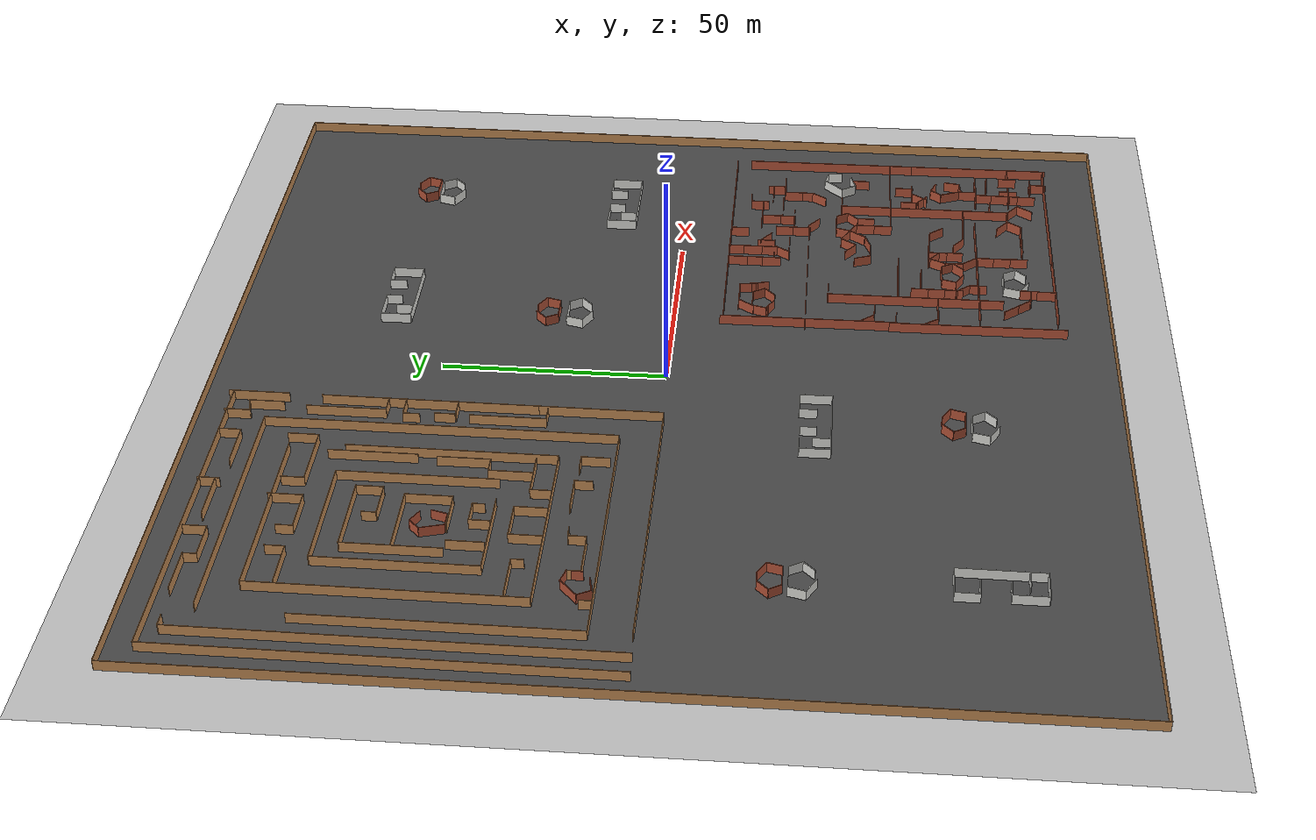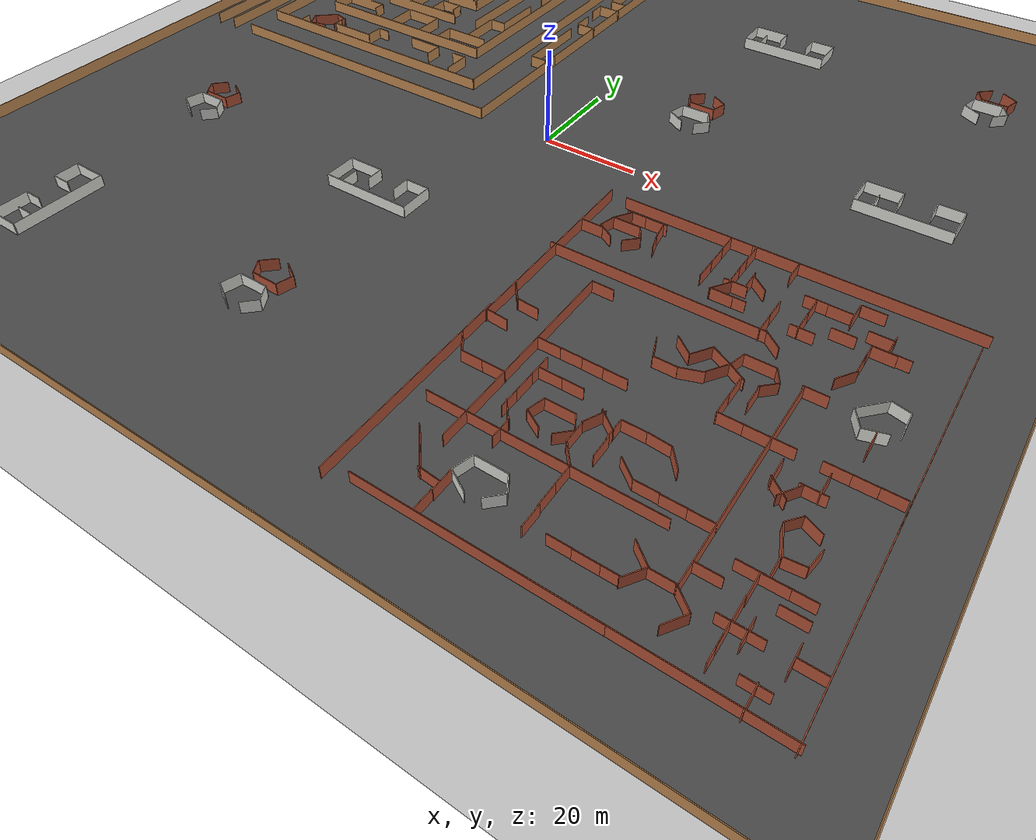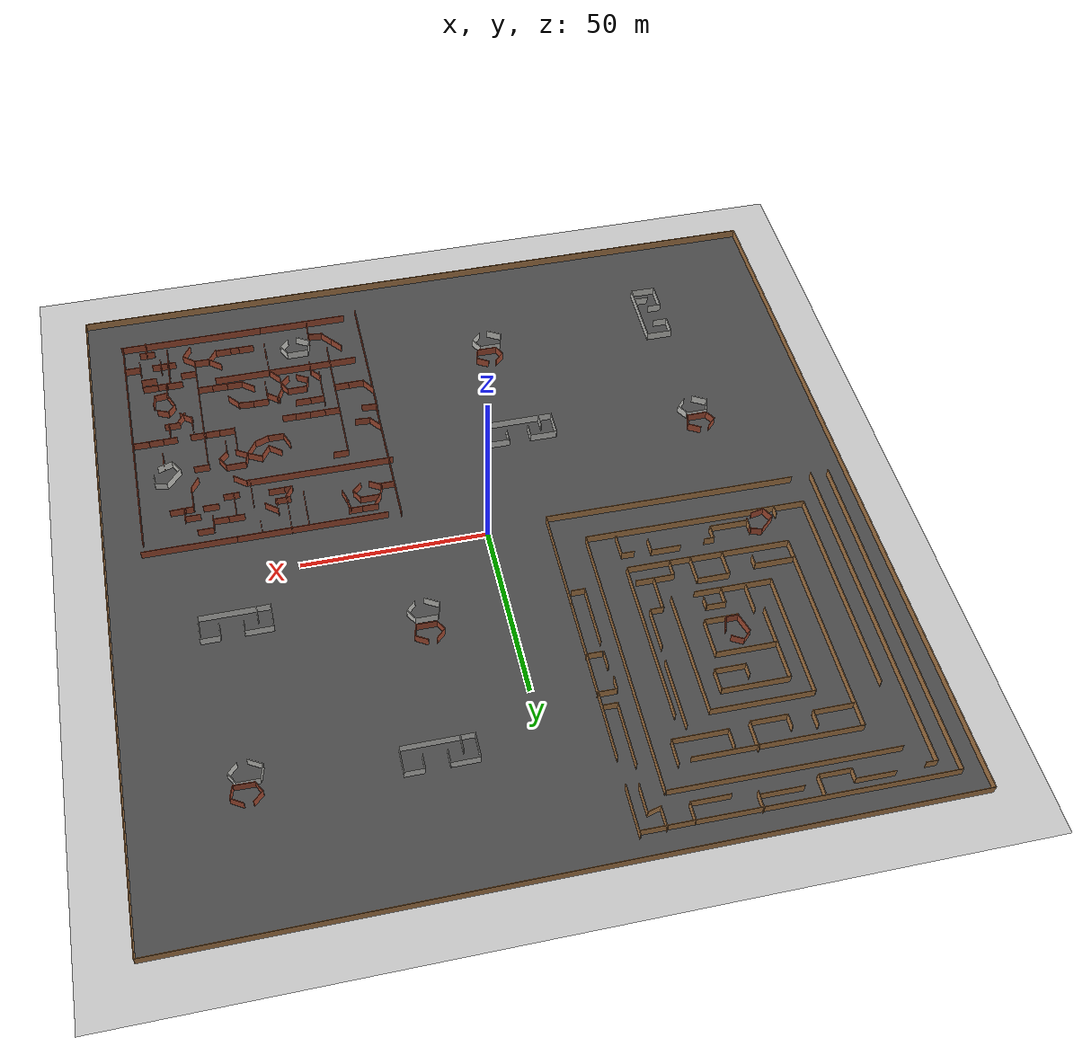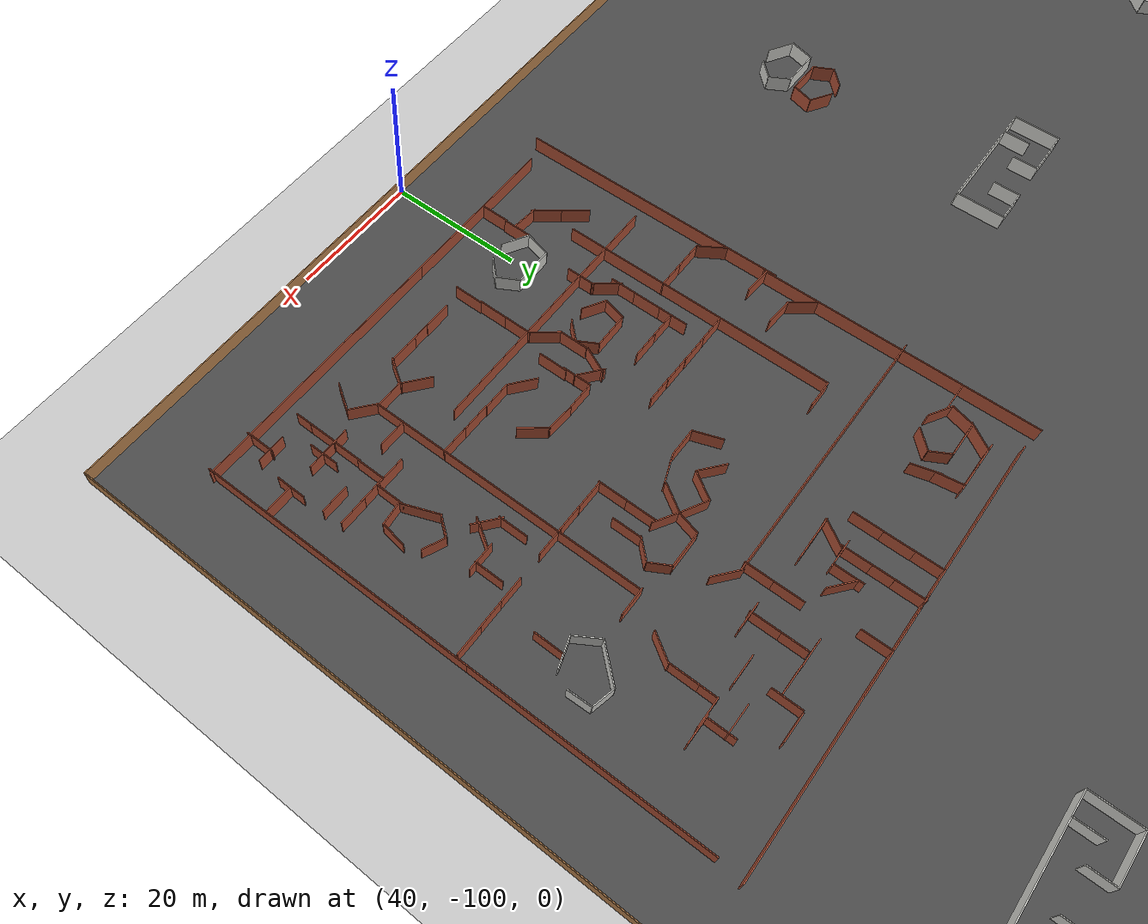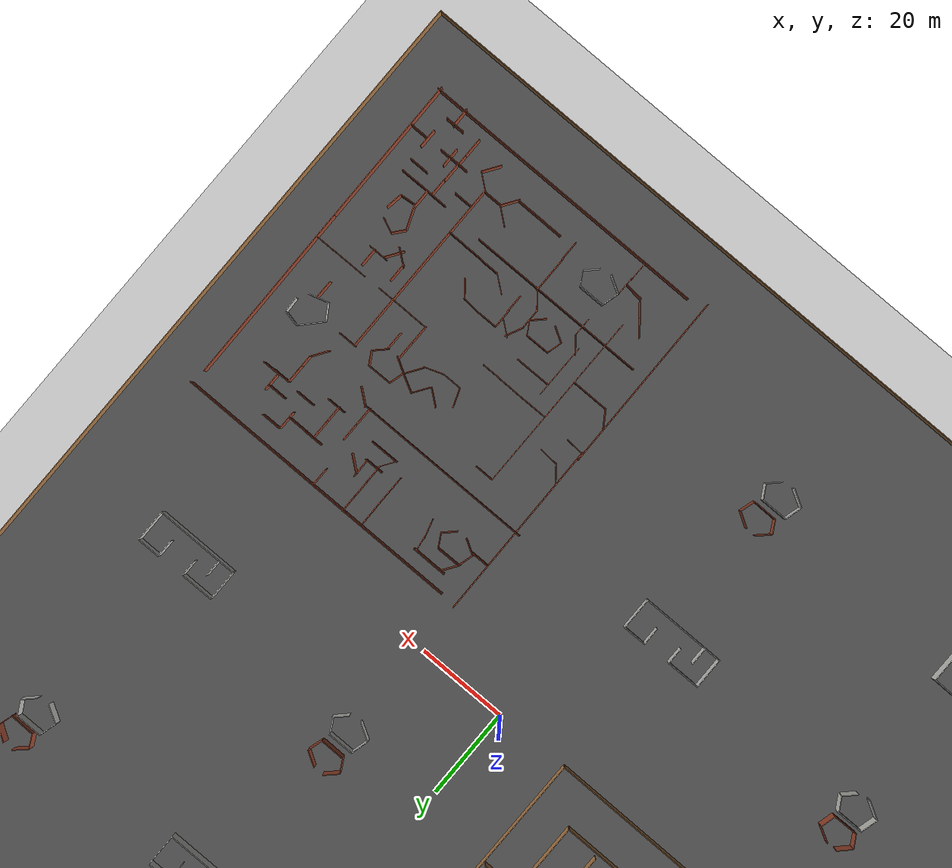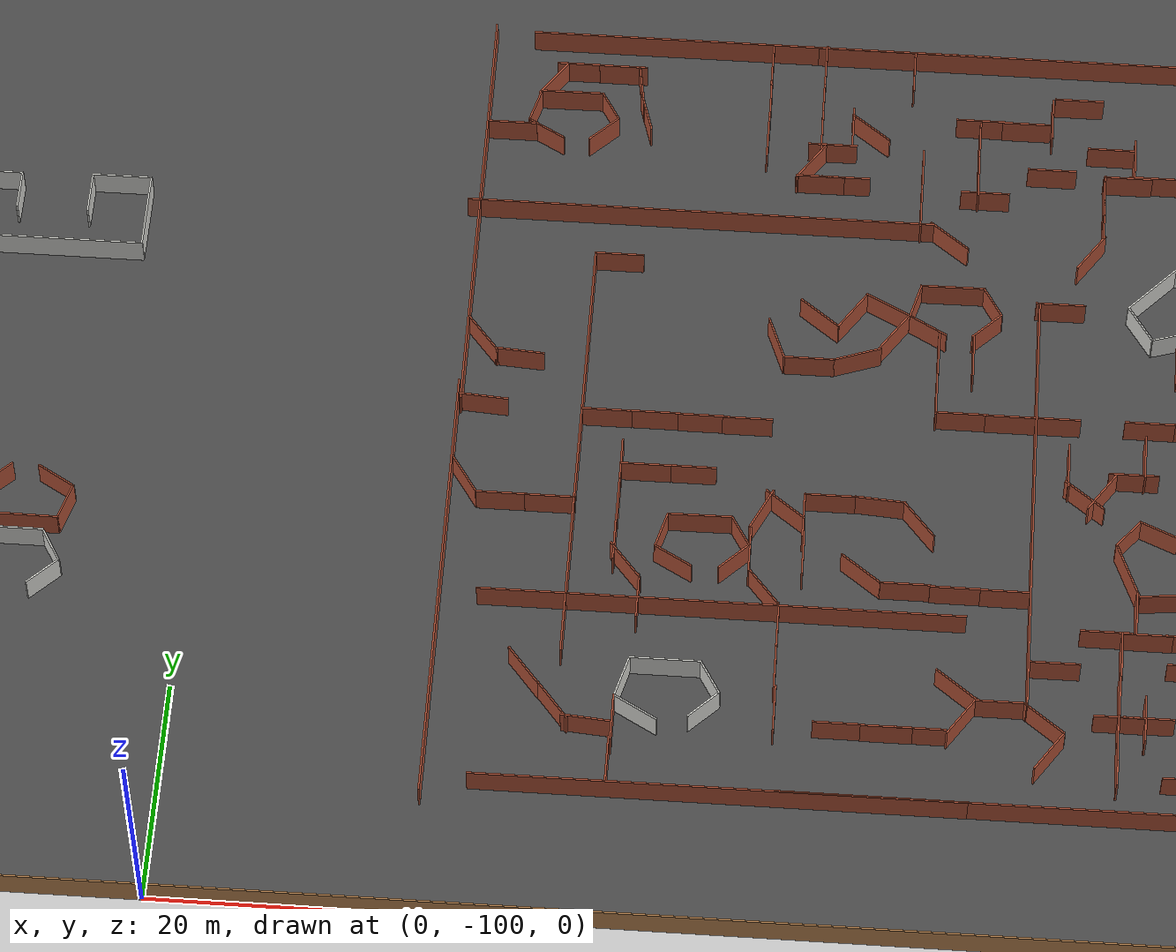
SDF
<sdf version="1.6">
 <world name="default">
  <plugin name="gazebo_connection_plugin" filename="libgazebo_connection_plugin.so"/>
  <light name="sun" type="directional">
   <cast_shadows>0</cast_shadows>
   <pose>0 0 10 0 -0 0</pose>
   <diffuse>0.8 0.8 0.8 1</diffuse>
   <specular>0.2 0.2 0.2 1</specular>
   <attenuation>
    <range>1000</range>
    <constant>0.9</constant>
    <linear>0.01</linear>
    <quadratic>0.001</quadratic>
   </attenuation>
   <direction>-0.5 0.1 -0.9</direction>
  </light>
  <model name="ground_plane">
   <static>1</static>
   <link name="link">
    <collision name="collision">
     <geometry><plane><normal>0 0 1</normal><size>200 200</size></plane></geometry>
     <surface><friction><ode><mu>100</mu><mu2>50</mu2></ode></friction></surface>
    </collision>
    <visual name="visual">
     <cast_shadows>0</cast_shadows>
     <geometry><plane><normal>0 0 1</normal><size>200 200</size></plane></geometry>
     <material>
      <script><uri>file://media/materials/scripts/gazebo.material</uri><name>Gazebo/Grey</name></script>
     </material>
    </visual>
   </link>
  </model>
  <physics name="default_physics" default="0" type="ode">
   <max_step_size>0.001</max_step_size>
   <real_time_factor>1</real_time_factor>
   <real_time_update_rate>1000</real_time_update_rate>
  </physics>
  <scene><ambient>0.4 0.4 0.4 1</ambient><background>0.7 0.7 0.7 1</background><shadows>1</shadows></scene>
  <spherical_coordinates>
   <surface_model>EARTH_WGS84</surface_model>
   <latitude_deg>0</latitude_deg>
   <longitude_deg>0</longitude_deg>
   <elevation>0</elevation>
   <heading_deg>0</heading_deg>
  </spherical_coordinates>
  <model name="asphalt_plane">
   <static>1</static>
   <link name="link">
    <collision name="collision"><geometry><box><size>200 200 0.1</size></box></geometry></collision>
    <visual name="visual">
     <cast_shadows>0</cast_shadows>
     <geometry><box><size>200 200 0.1</size></box></geometry>
     <material>
      <script>
       <uri>model://asphalt_plane/materials/scripts</uri>
       <uri>model://asphalt_plane/materials/textures</uri>
       <name>vrc/asphalt</name>
      </script>
     </material>
    </visual>
   </link>
  </model>
  <model name="brick_longwall_0_clone">
   <pose>70.0948 -58.1794 0 0 0 -1.57092</pose>
   <link name="Wall_0">
    <collision name="Wall_0_Collision">
     <geometry><box><size>40.5 0.15 2.5</size></box></geometry>
     <pose>0 0 1.25 0 -0 0</pose>
    </collision>
    <visual name="Wall_0_Visual">
     <pose>0 0 1.25 0 -0 0</pose>
     <geometry><box><size>40.5 0.15 2.5</size></box></geometry>
     <material>
      <script><uri>file://media/materials/scripts/gazebo.material</uri><name>Gazebo/Bricks</name></script>
      <ambient>1 1 1 1</ambient>
     </material>
    </visual>
    <pose>1e-06 0 0 0 -0 0</pose>
   </link>
   <static>1</static>
  </model>
  <model name="brick_longwall_clone">
   <pose>40.5339 -30.0862 0 0 -0 0</pose>
   <link name="Wall_0">
    <collision name="Wall_0_Collision">
     <geometry><box><size>40.5 0.15 2.5</size></box></geometry>
     <pose>0 0 1.25 0 -0 0</pose>
    </collision>
    <visual name="Wall_0_Visual">
     <pose>0 0 1.25 0 -0 0</pose>
     <geometry><box><size>40.5 0.15 2.5</size></box></geometry>
     <material>
      <script><uri>file://media/materials/scripts/gazebo.material</uri><name>Gazebo/Bricks</name></script>
      <ambient>1 1 1 1</ambient>
     </material>
    </visual>
    <pose>1e-06 0 0 0 -0 0</pose>
   </link>
   <static>1</static>
  </model>
  <model name="brick_room1">
   <pose>62.9469 -39.1804 0 0 -0 0</pose>
   <link name="Wall_11">
    <collision name="Wall_11_Collision">
     <geometry><box><size>3.25 0.15 2.5</size></box></geometry>
     <pose>0 0 1.25 0 -0 0</pose>
    </collision>
    <visual name="Wall_11_Visual">
     <pose>0 0 1.25 0 -0 0</pose>
     <geometry><box><size>3.25 0.15 2.5</size></box></geometry>
     <material>
      <script><uri>file://media/materials/scripts/gazebo.material</uri><name>Gazebo/Bricks</name></script>
      <ambient>1 1 1 1</ambient>
     </material>
    </visual>
    <pose>3.12132 1.19483 0 0 0 -1.0472</pose>
   </link>
   <link name="Wall_12">
    <collision name="Wall_12_Collision">
     <geometry><box><size>3.5 0.15 2.5</size></box></geometry>
     <pose>0 0 1.25 0 -0 0</pose>
    </collision>
    <visual name="Wall_12_Visual">
     <pose>0 0 1.25 0 -0 0</pose>
     <geometry><box><size>3.5 0.15 2.5</size></box></geometry>
     <material>
      <script><uri>file://media/materials/scripts/gazebo.material</uri><name>Gazebo/Bricks</name></script>
      <ambient>1 1 1 1</ambient>
     </material>
    </visual>
    <pose>2.71192 -1.33192 0 0 0 -2.35619</pose>
   </link>
   <link name="Wall_7">
    <collision name="Wall_7_Collision">
     <geometry><box><size>5.52935 0.15 2.5</size></box></geometry>
     <pose>0 0 1.25 0 -0 0</pose>
    </collision>
    <visual name="Wall_7_Visual">
     <pose>0 0 1.25 0 -0 0</pose>
     <geometry><box><size>5.52935 0.15 2.5</size></box></geometry>
     <material>
      <script><uri>file://media/materials/scripts/gazebo.material</uri><name>Gazebo/Bricks</name></script>
      <ambient>1 1 1 1</ambient>
     </material>
    </visual>
    <pose>-0.343285 2.51793 0 0 0 -3.13444</pose>
   </link>
   <link name="Wall_8">
    <collision name="Wall_8_Collision">
     <geometry><box><size>3.5 0.15 2.5</size></box></geometry>
     <pose>0 0 1.25 0 -0 0</pose>
    </collision>
    <visual name="Wall_8_Visual">
     <pose>0 0 1.25 0 -0 0</pose>
     <geometry><box><size>3.5 0.15 2.5</size></box></geometry>
     <material>
      <script><uri>file://media/materials/scripts/gazebo.material</uri><name>Gazebo/Bricks</name></script>
      <ambient>1 1 1 1</ambient>
     </material>
    </visual>
    <pose>-3.46641 0.880761 0 0 0 -1.8326</pose>
   </link>
   <link name="Wall_9">
    <collision name="Wall_9_Collision">
     <geometry><box><size>3.75 0.15 2.5</size></box></geometry>
     <pose>0 0 1.25 0 -0 0</pose>
    </collision>
    <visual name="Wall_9_Visual">
     <pose>0 0 1.25 0 -0 0</pose>
     <geometry><box><size>3.75 0.15 2.5</size></box></geometry>
     <material>
      <script><uri>file://media/materials/scripts/gazebo.material</uri><name>Gazebo/Bricks</name></script>
      <ambient>1 1 1 1</ambient>
     </material>
    </visual>
    <pose>-2.34109 -1.63716 0 0 0 -0.523599</pose>
   </link>
   <static>1</static>
  </model>
  <model name="brick_worlds_2">
   <pose>57.0992 -38.867 0 0 -0 1.08023</pose>
   <link name="Wall_0">
    <collision name="Wall_0_Collision">
     <geometry><box><size>4.25 0.15 2.5</size></box></geometry>
     <pose>0 0 1.25 0 -0 0</pose>
    </collision>
    <visual name="Wall_0_Visual">
     <pose>0 0 1.25 0 -0 0</pose>
     <geometry><box><size>4.25 0.15 2.5</size></box></geometry>
     <material>
      <script><uri>file://media/materials/scripts/gazebo.material</uri><name>Gazebo/Bricks</name></script>
      <ambient>1 1 1 1</ambient>
     </material>
    </visual>
    <pose>0 -0 0 0 -0 1.5708</pose>
   </link>
   <static>1</static>
  </model>
  <model name="brick_worlds_0_clone">
   <pose>57.3372 -59.0075 0 0 -0 1.49697</pose>
   <link name="Wall_0">
    <collision name="Wall_0_Collision">
     <geometry><box><size>4.25 0.15 2.5</size></box></geometry>
     <pose>0 0 1.25 0 -0 0</pose>
    </collision>
    <visual name="Wall_0_Visual">
     <pose>0 0 1.25 0 -0 0</pose>
     <geometry><box><size>4.25 0.15 2.5</size></box></geometry>
     <material>
      <script><uri>file://media/materials/scripts/gazebo.material</uri><name>Gazebo/Bricks</name></script>
      <ambient>1 1 1 1</ambient>
     </material>
    </visual>
    <pose>0 -0 0 0 -0 1.5708</pose>
   </link>
   <static>1</static>
  </model>
  <model name="brick_worlds_2_clone">
   <pose>60.6055 -60.7291 0 0 -0 0.67691</pose>
   <link name="Wall_0">
    <collision name="Wall_0_Collision">
     <geometry><box><size>4.25 0.15 2.5</size></box></geometry>
     <pose>0 0 1.25 0 -0 0</pose>
    </collision>
    <visual name="Wall_0_Visual">
     <pose>0 0 1.25 0 -0 0</pose>
     <geometry><box><size>4.25 0.15 2.5</size></box></geometry>
     <material>
      <script><uri>file://media/materials/scripts/gazebo.material</uri><name>Gazebo/Bricks</name></script>
      <ambient>1 1 1 1</ambient>
     </material>
    </visual>
    <pose>0 -0 0 0 -0 1.5708</pose>
   </link>
   <static>1</static>
  </model>
  <model name="brick_worlds_1_clone">
   <pose>61.6345 -43.6539 0 0 -0 0</pose>
   <link name="Wall_0">
    <collision name="Wall_0_Collision">
     <geometry><box><size>4.25 0.15 2.5</size></box></geometry>
     <pose>0 0 1.25 0 -0 0</pose>
    </collision>
    <visual name="Wall_0_Visual">
     <pose>0 0 1.25 0 -0 0</pose>
     <geometry><box><size>4.25 0.15 2.5</size></box></geometry>
     <material>
      <script><uri>file://media/materials/scripts/gazebo.material</uri><name>Gazebo/Bricks</name></script>
      <ambient>1 1 1 1</ambient>
     </material>
    </visual>
    <pose>0 -0 0 0 -0 1.5708</pose>
   </link>
   <static>1</static>
  </model>
  <model name="brick_worlds_1_clone_0">
   <pose>61.6134 -47.8914 0 0 -0 0</pose>
   <link name="Wall_0">
    <collision name="Wall_0_Collision">
     <geometry><box><size>4.25 0.15 2.5</size></box></geometry>
     <pose>0 0 1.25 0 -0 0</pose>
    </collision>
    <visual name="Wall_0_Visual">
     <pose>0 0 1.25 0 -0 0</pose>
     <geometry><box><size>4.25 0.15 2.5</size></box></geometry>
     <material>
      <script><uri>file://media/materials/scripts/gazebo.material</uri><name>Gazebo/Bricks</name></script>
      <ambient>1 1 1 1</ambient>
     </material>
    </visual>
    <pose>0 -0 0 0 -0 1.5708</pose>
   </link>
   <static>1</static>
  </model>
  <model name="brick_worlds_1_clone_0_clone">
   <pose>63.736 -49.7946 0 0 0 -1.57092</pose>
   <link name="Wall_0">
    <collision name="Wall_0_Collision">
     <geometry><box><size>4.25 0.15 2.5</size></box></geometry>
     <pose>0 0 1.25 0 -0 0</pose>
    </collision>
    <visual name="Wall_0_Visual">
     <pose>0 0 1.25 0 -0 0</pose>
     <geometry><box><size>4.25 0.15 2.5</size></box></geometry>
     <material>
      <script><uri>file://media/materials/scripts/gazebo.material</uri><name>Gazebo/Bricks</name></script>
      <ambient>1 1 1 1</ambient>
     </material>
    </visual>
    <pose>0 -0 0 0 -0 1.5708</pose>
   </link>
   <static>1</static>
  </model>
  <model name="brick_worlds_1_clone_0_clone_clone">
   <pose>67.9203 -49.8236 0 0 0 -1.57092</pose>
   <link name="Wall_0">
    <collision name="Wall_0_Collision">
     <geometry><box><size>4.25 0.15 2.5</size></box></geometry>
     <pose>0 0 1.25 0 -0 0</pose>
    </collision>
    <visual name="Wall_0_Visual">
     <pose>0 0 1.25 0 -0 0</pose>
     <geometry><box><size>4.25 0.15 2.5</size></box></geometry>
     <material>
      <script><uri>file://media/materials/scripts/gazebo.material</uri><name>Gazebo/Bricks</name></script>
      <ambient>1 1 1 1</ambient>
     </material>
    </visual>
    <pose>0 -0 0 0 -0 1.5708</pose>
   </link>
   <static>1</static>
  </model>
  <model name="brick_worlds_1_clone_0_clone_clone_0">
   <pose>71.8838 -37.8494 0 0 0 -1.57092</pose>
   <link name="Wall_0">
    <collision name="Wall_0_Collision">
     <geometry><box><size>4.25 0.15 2.5</size></box></geometry>
     <pose>0 0 1.25 0 -0 0</pose>
    </collision>
    <visual name="Wall_0_Visual">
     <pose>0 0 1.25 0 -0 0</pose>
     <geometry><box><size>4.25 0.15 2.5</size></box></geometry>
     <material>
      <script><uri>file://media/materials/scripts/gazebo.material</uri><name>Gazebo/Bricks</name></script>
      <ambient>1 1 1 1</ambient>
     </material>
    </visual>
    <pose>0 -0 0 0 -0 1.5708</pose>
   </link>
   <static>1</static>
  </model>
  <model name="brick_worlds_1_clone_1_clone">
   <pose>51.1412 -64.7 0 0 -0 0</pose>
   <link name="Wall_0">
    <collision name="Wall_0_Collision">
     <geometry><box><size>4.25 0.15 2.5</size></box></geometry>
     <pose>0 0 1.25 0 -0 0</pose>
    </collision>
    <visual name="Wall_0_Visual">
     <pose>0 0 1.25 0 -0 0</pose>
     <geometry><box><size>4.25 0.15 2.5</size></box></geometry>
     <material>
      <script><uri>file://media/materials/scripts/gazebo.material</uri><name>Gazebo/Bricks</name></script>
      <ambient>1 1 1 1</ambient>
     </material>
    </visual>
    <pose>0 -0 0 0 -0 1.5708</pose>
   </link>
   <static>1</static>
  </model>
  <model name="brick_worlds_1_clone_0_clone_clone_0_clone_clone_0">
   <pose>53.1055 -58.8873 0 0 0 -1.57092</pose>
   <link name="Wall_0">
    <collision name="Wall_0_Collision">
     <geometry><box><size>4.25 0.15 2.5</size></box></geometry>
     <pose>0 0 1.25 0 -0 0</pose>
    </collision>
    <visual name="Wall_0_Visual">
     <pose>0 0 1.25 0 -0 0</pose>
     <geometry><box><size>4.25 0.15 2.5</size></box></geometry>
     <material>
      <script><uri>file://media/materials/scripts/gazebo.material</uri><name>Gazebo/Bricks</name></script>
      <ambient>1 1 1 1</ambient>
     </material>
    </visual>
    <pose>0 -0 0 0 -0 1.5708</pose>
   </link>
   <static>1</static>
  </model>
  <model name="brick_worlds_1_clone_1_clone_7_clone_clone">
   <pose>54.1633 -39.674 0 0 0 -0.589381</pose>
   <link name="Wall_0">
    <collision name="Wall_0_Collision">
     <geometry><box><size>4.25 0.15 2.5</size></box></geometry>
     <pose>0 0 1.25 0 -0 0</pose>
    </collision>
    <visual name="Wall_0_Visual">
     <pose>0 0 1.25 0 -0 0</pose>
     <geometry><box><size>4.25 0.15 2.5</size></box></geometry>
     <material>
      <script><uri>file://media/materials/scripts/gazebo.material</uri><name>Gazebo/Bricks</name></script>
      <ambient>1 1 1 1</ambient>
     </material>
    </visual>
    <pose>0 -0 0 0 -0 1.5708</pose>
   </link>
   <static>1</static>
  </model>
  <model name="brick_worlds_1_clone_1_clone_7_clone_clone_clone">
   <pose>57.7678 -41.7145 0 0 0 -0.589381</pose>
   <link name="Wall_0">
    <collision name="Wall_0_Collision">
     <geometry><box><size>4.25 0.15 2.5</size></box></geometry>
     <pose>0 0 1.25 0 -0 0</pose>
    </collision>
    <visual name="Wall_0_Visual">
     <pose>0 0 1.25 0 -0 0</pose>
     <geometry><box><size>4.25 0.15 2.5</size></box></geometry>
     <material>
      <script><uri>file://media/materials/scripts/gazebo.material</uri><name>Gazebo/Bricks</name></script>
      <ambient>1 1 1 1</ambient>
     </material>
    </visual>
    <pose>0 -0 0 0 -0 1.5708</pose>
   </link>
   <static>1</static>
  </model>
  <model name="brick_worlds_1_clone_0_clone_clone_0_clone_clone_0_clone_clone">
   <pose>47.8022 -43.0147 0 0 0 -2.78777</pose>
   <link name="Wall_0">
    <collision name="Wall_0_Collision">
     <geometry><box><size>4.25 0.15 2.5</size></box></geometry>
     <pose>0 0 1.25 0 -0 0</pose>
    </collision>
    <visual name="Wall_0_Visual">
     <pose>0 0 1.25 0 -0 0</pose>
     <geometry><box><size>4.25 0.15 2.5</size></box></geometry>
     <material>
      <script><uri>file://media/materials/scripts/gazebo.material</uri><name>Gazebo/Bricks</name></script>
      <ambient>1 1 1 1</ambient>
     </material>
    </visual>
    <pose>0 -0 0 0 -0 1.5708</pose>
   </link>
   <static>1</static>
  </model>
  <model name="brick_worlds_1_clone_0_clone_clone_0_clone_clone_0_clone_clone_0">
   <pose>54.7413 -44.255 0 0 0 -1.22347</pose>
   <link name="Wall_0">
    <collision name="Wall_0_Collision">
     <geometry><box><size>4.25 0.15 2.5</size></box></geometry>
     <pose>0 0 1.25 0 -0 0</pose>
    </collision>
    <visual name="Wall_0_Visual">
     <pose>0 0 1.25 0 -0 0</pose>
     <geometry><box><size>4.25 0.15 2.5</size></box></geometry>
     <material>
      <script><uri>file://media/materials/scripts/gazebo.material</uri><name>Gazebo/Bricks</name></script>
      <ambient>1 1 1 1</ambient>
     </material>
    </visual>
    <pose>0 -0 0 0 -0 1.5708</pose>
   </link>
   <static>1</static>
  </model>
  <model name="brick_worlds_1_clone_0_clone_clone_0_clone_clone_0_clone_clone_clone">
   <pose>50.6997 -44.9664 0 0 0 -1.57092</pose>
   <link name="Wall_0">
    <collision name="Wall_0_Collision">
     <geometry><box><size>4.25 0.15 2.5</size></box></geometry>
     <pose>0 0 1.25 0 -0 0</pose>
    </collision>
    <visual name="Wall_0_Visual">
     <pose>0 0 1.25 0 -0 0</pose>
     <geometry><box><size>4.25 0.15 2.5</size></box></geometry>
     <material>
      <script><uri>file://media/materials/scripts/gazebo.material</uri><name>Gazebo/Bricks</name></script>
      <ambient>1 1 1 1</ambient>
     </material>
    </visual>
    <pose>0 -0 0 0 -0 1.5708</pose>
   </link>
   <static>1</static>
  </model>
  <model name="brick_worlds_1_clone_1_clone_7_clone_clone_0">
   <pose>51.3459 -40.1271 0 0 -0 0.90029</pose>
   <link name="Wall_0">
    <collision name="Wall_0_Collision">
     <geometry><box><size>4.25 0.15 2.5</size></box></geometry>
     <pose>0 0 1.25 0 -0 0</pose>
    </collision>
    <visual name="Wall_0_Visual">
     <pose>0 0 1.25 0 -0 0</pose>
     <geometry><box><size>4.25 0.15 2.5</size></box></geometry>
     <material>
      <script><uri>file://media/materials/scripts/gazebo.material</uri><name>Gazebo/Bricks</name></script>
      <ambient>1 1 1 1</ambient>
     </material>
    </visual>
    <pose>0 -0 0 0 -0 1.5708</pose>
   </link>
   <static>1</static>
  </model>
  <model name="brick_worlds_1_clone_clone">
   <pose>64.6066 -43.6549 0 0 -0 0</pose>
   <link name="Wall_0">
    <collision name="Wall_0_Collision">
     <geometry><box><size>4.25 0.15 2.5</size></box></geometry>
     <pose>0 0 1.25 0 -0 0</pose>
    </collision>
    <visual name="Wall_0_Visual">
     <pose>0 0 1.25 0 -0 0</pose>
     <geometry><box><size>4.25 0.15 2.5</size></box></geometry>
     <material>
      <script><uri>file://media/materials/scripts/gazebo.material</uri><name>Gazebo/Bricks</name></script>
      <ambient>1 1 1 1</ambient>
     </material>
    </visual>
    <pose>0 -0 0 0 -0 1.5708</pose>
   </link>
   <static>1</static>
  </model>
  <gravity>0 0 -9.8</gravity>
  <magnetic_field>6e-06 2.3e-05 -4.2e-05</magnetic_field>
  <atmosphere type="adiabatic"/>
  <model name="brick_longwall_clone_clone">
   <pose>70.133 -11.2921 0 0 -0 0</pose>
   <link name="Wall_0">
    <collision name="Wall_0_Collision">
     <geometry><box><size>40.5 0.15 2.5</size></box></geometry>
     <pose>0 0 1.25 0 -0 0</pose>
    </collision>
    <visual name="Wall_0_Visual">
     <pose>0 0 1.25 0 -0 0</pose>
     <geometry><box><size>40.5 0.15 2.5</size></box></geometry>
     <material>
      <script><uri>file://media/materials/scripts/gazebo.material</uri><name>Gazebo/Bricks</name></script>
      <ambient>1 1 1 1</ambient>
     </material>
    </visual>
    <pose>1e-06 0 0 0 -0 0</pose>
   </link>
   <static>1</static>
  </model>
  <model name="brick_longwall_clone_clone_1">
   <pose>45.3217 -87.8888 0 0 -0 0</pose>
   <link name="Wall_0">
    <collision name="Wall_0_Collision">
     <geometry><box><size>40.5 0.15 2.5</size></box></geometry>
     <pose>0 0 1.25 0 -0 0</pose>
    </collision>
    <visual name="Wall_0_Visual">
     <pose>0 0 1.25 0 -0 0</pose>
     <geometry><box><size>40.5 0.15 2.5</size></box></geometry>
     <material>
      <script><uri>file://media/materials/scripts/gazebo.material</uri><name>Gazebo/Bricks</name></script>
      <ambient>1 1 1 1</ambient>
     </material>
    </visual>
    <pose>1e-06 0 0 0 -0 0</pose>
   </link>
   <static>1</static>
  </model>
  <model name="brick_longwall_clone_clone_3_clone_0">
   <pose>89.9316 -68.2995 0 0 0 -1.56602</pose>
   <link name="Wall_0">
    <collision name="Wall_0_Collision">
     <geometry><box><size>40.5 0.15 2.5</size></box></geometry>
     <pose>0 0 1.25 0 -0 0</pose>
    </collision>
    <visual name="Wall_0_Visual">
     <pose>0 0 1.25 0 -0 0</pose>
     <geometry><box><size>40.5 0.15 2.5</size></box></geometry>
     <material>
      <script><uri>file://media/materials/scripts/gazebo.material</uri><name>Gazebo/Bricks</name></script>
      <ambient>1 1 1 1</ambient>
     </material>
    </visual>
    <pose>1e-06 0 0 0 -0 0</pose>
   </link>
   <static>1</static>
  </model>
  <model name="brick_longwall_clone_clone_3_clone_1">
   <pose>21.2782 -69.4847 0 0 0 -1.56602</pose>
   <link name="Wall_0">
    <collision name="Wall_0_Collision">
     <geometry><box><size>40.5 0.15 2.5</size></box></geometry>
     <pose>0 0 1.25 0 -0 0</pose>
    </collision>
    <visual name="Wall_0_Visual">
     <pose>0 0 1.25 0 -0 0</pose>
     <geometry><box><size>40.5 0.15 2.5</size></box></geometry>
     <material>
      <script><uri>file://media/materials/scripts/gazebo.material</uri><name>Gazebo/Bricks</name></script>
      <ambient>1 1 1 1</ambient>
     </material>
    </visual>
    <pose>1e-06 0 0 0 -0 0</pose>
   </link>
   <static>1</static>
  </model>
  <model name="brick_longwall_clone_clone_3_clone_2">
   <pose>89.7563 -34.9133 0 0 0 -1.56602</pose>
   <link name="Wall_0">
    <collision name="Wall_0_Collision">
     <geometry><box><size>40.5 0.15 2.5</size></box></geometry>
     <pose>0 0 1.25 0 -0 0</pose>
    </collision>
    <visual name="Wall_0_Visual">
     <pose>0 0 1.25 0 -0 0</pose>
     <geometry><box><size>40.5 0.15 2.5</size></box></geometry>
     <material>
      <script><uri>file://media/materials/scripts/gazebo.material</uri><name>Gazebo/Bricks</name></script>
      <ambient>1 1 1 1</ambient>
     </material>
    </visual>
    <pose>1e-06 0 0 0 -0 0</pose>
   </link>
   <static>1</static>
  </model>
  <model name="brick_longwall_clone_clone_3_clone_1_clone">
   <pose>21.3531 -30.8304 0 0 0 -1.56602</pose>
   <link name="Wall_0">
    <collision name="Wall_0_Collision">
     <geometry><box><size>40.5 0.15 2.5</size></box></geometry>
     <pose>0 0 1.25 0 -0 0</pose>
    </collision>
    <visual name="Wall_0_Visual">
     <pose>0 0 1.25 0 -0 0</pose>
     <geometry><box><size>40.5 0.15 2.5</size></box></geometry>
     <material>
      <script><uri>file://media/materials/scripts/gazebo.material</uri><name>Gazebo/Bricks</name></script>
      <ambient>1 1 1 1</ambient>
     </material>
    </visual>
    <pose>1e-06 0 0 0 -0 0</pose>
   </link>
   <static>1</static>
  </model>
  <model name="brick_longwall_clone_clone_clone">
   <pose>44.9259 -11.2589 0 0 -0 0</pose>
   <link name="Wall_0">
    <collision name="Wall_0_Collision">
     <geometry><box><size>40.5 0.15 2.5</size></box></geometry>
     <pose>0 0 1.25 0 -0 0</pose>
    </collision>
    <visual name="Wall_0_Visual">
     <pose>0 0 1.25 0 -0 0</pose>
     <geometry><box><size>40.5 0.15 2.5</size></box></geometry>
     <material>
      <script><uri>file://media/materials/scripts/gazebo.material</uri><name>Gazebo/Bricks</name></script>
      <ambient>1 1 1 1</ambient>
     </material>
    </visual>
    <pose>1e-06 0 0 0 -0 0</pose>
   </link>
   <static>1</static>
  </model>
  <model name="brick_longwall_clone_clone_0">
   <pose>44.6402 -70.1055 0 0 -0 0</pose>
   <link name="Wall_0">
    <collision name="Wall_0_Collision">
     <geometry><box><size>40.5 0.15 2.5</size></box></geometry>
     <pose>0 0 1.25 0 -0 0</pose>
    </collision>
    <visual name="Wall_0_Visual">
     <pose>0 0 1.25 0 -0 0</pose>
     <geometry><box><size>40.5 0.15 2.5</size></box></geometry>
     <material>
      <script><uri>file://media/materials/scripts/gazebo.material</uri><name>Gazebo/Bricks</name></script>
      <ambient>1 1 1 1</ambient>
     </material>
    </visual>
    <pose>1e-06 0 0 0 -0 0</pose>
   </link>
   <static>1</static>
  </model>
  <model name="brick_longwall_0_clone_clone">
   <pose>31.77 -55.4466 0 0 0 -1.57092</pose>
   <link name="Wall_0">
    <collision name="Wall_0_Collision">
     <geometry><box><size>40.5 0.15 2.5</size></box></geometry>
     <pose>0 0 1.25 0 -0 0</pose>
    </collision>
    <visual name="Wall_0_Visual">
     <pose>0 0 1.25 0 -0 0</pose>
     <geometry><box><size>40.5 0.15 2.5</size></box></geometry>
     <material>
      <script><uri>file://media/materials/scripts/gazebo.material</uri><name>Gazebo/Bricks</name></script>
      <ambient>1 1 1 1</ambient>
     </material>
    </visual>
    <pose>1e-06 0 0 0 -0 0</pose>
   </link>
   <static>1</static>
  </model>
  <model name="brick_worlds_1_clone_0_clone_clone_0_clone_clone_clone">
   <pose>71.7506 -49.7978 0 0 0 -1.57092</pose>
   <link name="Wall_0">
    <collision name="Wall_0_Collision">
     <geometry><box><size>4.25 0.15 2.5</size></box></geometry>
     <pose>0 0 1.25 0 -0 0</pose>
    </collision>
    <visual name="Wall_0_Visual">
     <pose>0 0 1.25 0 -0 0</pose>
     <geometry><box><size>4.25 0.15 2.5</size></box></geometry>
     <material>
      <script><uri>file://media/materials/scripts/gazebo.material</uri><name>Gazebo/Bricks</name></script>
      <ambient>1 1 1 1</ambient>
     </material>
    </visual>
    <pose>0 -0 0 0 -0 1.5708</pose>
   </link>
   <static>1</static>
  </model>
  <model name="brick_worlds_1_clone_0_clone_clone_0_clone_clone_clone_0">
   <pose>67.9553 -78.1375 0 0 0 -1.57092</pose>
   <link name="Wall_0">
    <collision name="Wall_0_Collision">
     <geometry><box><size>4.25 0.15 2.5</size></box></geometry>
     <pose>0 0 1.25 0 -0 0</pose>
    </collision>
    <visual name="Wall_0_Visual">
     <pose>0 0 1.25 0 -0 0</pose>
     <geometry><box><size>4.25 0.15 2.5</size></box></geometry>
     <material>
      <script><uri>file://media/materials/scripts/gazebo.material</uri><name>Gazebo/Bricks</name></script>
      <ambient>1 1 1 1</ambient>
     </material>
    </visual>
    <pose>0 -0 0 0 -0 1.5708</pose>
   </link>
   <static>1</static>
  </model>
  <model name="brick_worlds_1_clone_0_clone_clone_0_clone_clone_clone_1">
   <pose>79.6674 -49.7138 0 0 0 -1.57092</pose>
   <link name="Wall_0">
    <collision name="Wall_0_Collision">
     <geometry><box><size>4.25 0.15 2.5</size></box></geometry>
     <pose>0 0 1.25 0 -0 0</pose>
    </collision>
    <visual name="Wall_0_Visual">
     <pose>0 0 1.25 0 -0 0</pose>
     <geometry><box><size>4.25 0.15 2.5</size></box></geometry>
     <material>
      <script><uri>file://media/materials/scripts/gazebo.material</uri><name>Gazebo/Bricks</name></script>
      <ambient>1 1 1 1</ambient>
     </material>
    </visual>
    <pose>0 -0 0 0 -0 1.5708</pose>
   </link>
   <static>1</static>
  </model>
  <model name="brick_worlds_1_clone_0_clone_clone_0_clone_clone_clone_2">
   <pose>83.5636 -49.7075 0 0 0 -1.57092</pose>
   <link name="Wall_0">
    <collision name="Wall_0_Collision">
     <geometry><box><size>4.25 0.15 2.5</size></box></geometry>
     <pose>0 0 1.25 0 -0 0</pose>
    </collision>
    <visual name="Wall_0_Visual">
     <pose>0 0 1.25 0 -0 0</pose>
     <geometry><box><size>4.25 0.15 2.5</size></box></geometry>
     <material>
      <script><uri>file://media/materials/scripts/gazebo.material</uri><name>Gazebo/Bricks</name></script>
      <ambient>1 1 1 1</ambient>
     </material>
    </visual>
    <pose>0 -0 0 0 -0 1.5708</pose>
   </link>
   <static>1</static>
  </model>
  <model name="brick_worlds_1_clone_0_clone_clone_0_clone_clone_clone_3">
   <pose>87.4411 -49.6799 0 0 0 -1.57092</pose>
   <link name="Wall_0">
    <collision name="Wall_0_Collision">
     <geometry><box><size>4.25 0.15 2.5</size></box></geometry>
     <pose>0 0 1.25 0 -0 0</pose>
    </collision>
    <visual name="Wall_0_Visual">
     <pose>0 0 1.25 0 -0 0</pose>
     <geometry><box><size>4.25 0.15 2.5</size></box></geometry>
     <material>
      <script><uri>file://media/materials/scripts/gazebo.material</uri><name>Gazebo/Bricks</name></script>
      <ambient>1 1 1 1</ambient>
     </material>
    </visual>
    <pose>0 -0 0 0 -0 1.5708</pose>
   </link>
   <static>1</static>
  </model>
  <model name="brick_worlds_1_clone_1_clone_clone_0_clone">
   <pose>49.3914 -71.9286 0 0 -0 0</pose>
   <link name="Wall_0">
    <collision name="Wall_0_Collision">
     <geometry><box><size>4.25 0.15 2.5</size></box></geometry>
     <pose>0 0 1.25 0 -0 0</pose>
    </collision>
    <visual name="Wall_0_Visual">
     <pose>0 0 1.25 0 -0 0</pose>
     <geometry><box><size>4.25 0.15 2.5</size></box></geometry>
     <material>
      <script><uri>file://media/materials/scripts/gazebo.material</uri><name>Gazebo/Bricks</name></script>
      <ambient>1 1 1 1</ambient>
     </material>
    </visual>
    <pose>0 -0 0 0 -0 1.5708</pose>
   </link>
   <static>1</static>
  </model>
  <model name="brick_worlds_1_clone_1_clone_clone_0_clone_0">
   <pose>49.402 -75.9018 0 0 -0 0</pose>
   <link name="Wall_0">
    <collision name="Wall_0_Collision">
     <geometry><box><size>4.25 0.15 2.5</size></box></geometry>
     <pose>0 0 1.25 0 -0 0</pose>
    </collision>
    <visual name="Wall_0_Visual">
     <pose>0 0 1.25 0 -0 0</pose>
     <geometry><box><size>4.25 0.15 2.5</size></box></geometry>
     <material>
      <script><uri>file://media/materials/scripts/gazebo.material</uri><name>Gazebo/Bricks</name></script>
      <ambient>1 1 1 1</ambient>
     </material>
    </visual>
    <pose>0 -0 0 0 -0 1.5708</pose>
   </link>
   <static>1</static>
  </model>
  <model name="brick_worlds_1_clone_1_clone_clone_0_clone_1">
   <pose>49.5458 -79.924 0 0 -0 0</pose>
   <link name="Wall_0">
    <collision name="Wall_0_Collision">
     <geometry><box><size>4.25 0.15 2.5</size></box></geometry>
     <pose>0 0 1.25 0 -0 0</pose>
    </collision>
    <visual name="Wall_0_Visual">
     <pose>0 0 1.25 0 -0 0</pose>
     <geometry><box><size>4.25 0.15 2.5</size></box></geometry>
     <material>
      <script><uri>file://media/materials/scripts/gazebo.material</uri><name>Gazebo/Bricks</name></script>
      <ambient>1 1 1 1</ambient>
     </material>
    </visual>
    <pose>0 -0 0 0 -0 1.5708</pose>
   </link>
   <static>1</static>
  </model>
  <model name="brick_worlds_1_clone_1_clone_clone_0_clone_3">
   <pose>45.9096 -21.4531 0 0 -0 0</pose>
   <link name="Wall_0">
    <collision name="Wall_0_Collision">
     <geometry><box><size>4.25 0.15 2.5</size></box></geometry>
     <pose>0 0 1.25 0 -0 0</pose>
    </collision>
    <visual name="Wall_0_Visual">
     <pose>0 0 1.25 0 -0 0</pose>
     <geometry><box><size>4.25 0.15 2.5</size></box></geometry>
     <material>
      <script><uri>file://media/materials/scripts/gazebo.material</uri><name>Gazebo/Bricks</name></script>
      <ambient>1 1 1 1</ambient>
     </material>
    </visual>
    <pose>0 -0 0 0 -0 1.5708</pose>
   </link>
   <static>1</static>
  </model>
  <model name="brick_worlds_1_clone_1_clone_clone_0_clone_5">
   <pose>45.9289 -17.2509 0 0 -0 0</pose>
   <link name="Wall_0">
    <collision name="Wall_0_Collision">
     <geometry><box><size>4.25 0.15 2.5</size></box></geometry>
     <pose>0 0 1.25 0 -0 0</pose>
    </collision>
    <visual name="Wall_0_Visual">
     <pose>0 0 1.25 0 -0 0</pose>
     <geometry><box><size>4.25 0.15 2.5</size></box></geometry>
     <material>
      <script><uri>file://media/materials/scripts/gazebo.material</uri><name>Gazebo/Bricks</name></script>
      <ambient>1 1 1 1</ambient>
     </material>
    </visual>
    <pose>0 -0 0 0 -0 1.5708</pose>
   </link>
   <static>1</static>
  </model>
  <model name="brick_worlds_1_clone_1_clone_clone_0_clone_6">
   <pose>45.8934 -13.5337 0 0 -0 0</pose>
   <link name="Wall_0">
    <collision name="Wall_0_Collision">
     <geometry><box><size>4.25 0.15 2.5</size></box></geometry>
     <pose>0 0 1.25 0 -0 0</pose>
    </collision>
    <visual name="Wall_0_Visual">
     <pose>0 0 1.25 0 -0 0</pose>
     <geometry><box><size>4.25 0.15 2.5</size></box></geometry>
     <material>
      <script><uri>file://media/materials/scripts/gazebo.material</uri><name>Gazebo/Bricks</name></script>
      <ambient>1 1 1 1</ambient>
     </material>
    </visual>
    <pose>0 -0 0 0 -0 1.5708</pose>
   </link>
   <static>1</static>
  </model>
  <model name="brick_room1_clone">
   <pose>28.8484 -20.2692 0 0 -0 0</pose>
   <link name="Wall_11">
    <collision name="Wall_11_Collision">
     <geometry><box><size>3.25 0.15 2.5</size></box></geometry>
     <pose>0 0 1.25 0 -0 0</pose>
    </collision>
    <visual name="Wall_11_Visual">
     <pose>0 0 1.25 0 -0 0</pose>
     <geometry><box><size>3.25 0.15 2.5</size></box></geometry>
     <material>
      <script><uri>file://media/materials/scripts/gazebo.material</uri><name>Gazebo/Bricks</name></script>
      <ambient>1 1 1 1</ambient>
     </material>
    </visual>
    <pose>3.12132 1.19483 0 0 0 -1.0472</pose>
   </link>
   <link name="Wall_12">
    <collision name="Wall_12_Collision">
     <geometry><box><size>3.5 0.15 2.5</size></box></geometry>
     <pose>0 0 1.25 0 -0 0</pose>
    </collision>
    <visual name="Wall_12_Visual">
     <pose>0 0 1.25 0 -0 0</pose>
     <geometry><box><size>3.5 0.15 2.5</size></box></geometry>
     <material>
      <script><uri>file://media/materials/scripts/gazebo.material</uri><name>Gazebo/Bricks</name></script>
      <ambient>1 1 1 1</ambient>
     </material>
    </visual>
    <pose>2.71192 -1.33192 0 0 0 -2.35619</pose>
   </link>
   <link name="Wall_7">
    <collision name="Wall_7_Collision">
     <geometry><box><size>5.52935 0.15 2.5</size></box></geometry>
     <pose>0 0 1.25 0 -0 0</pose>
    </collision>
    <visual name="Wall_7_Visual">
     <pose>0 0 1.25 0 -0 0</pose>
     <geometry><box><size>5.52935 0.15 2.5</size></box></geometry>
     <material>
      <script><uri>file://media/materials/scripts/gazebo.material</uri><name>Gazebo/Bricks</name></script>
      <ambient>1 1 1 1</ambient>
     </material>
    </visual>
    <pose>-0.343285 2.51793 0 0 0 -3.13444</pose>
   </link>
   <link name="Wall_8">
    <collision name="Wall_8_Collision">
     <geometry><box><size>3.5 0.15 2.5</size></box></geometry>
     <pose>0 0 1.25 0 -0 0</pose>
    </collision>
    <visual name="Wall_8_Visual">
     <pose>0 0 1.25 0 -0 0</pose>
     <geometry><box><size>3.5 0.15 2.5</size></box></geometry>
     <material>
      <script><uri>file://media/materials/scripts/gazebo.material</uri><name>Gazebo/Bricks</name></script>
      <ambient>1 1 1 1</ambient>
     </material>
    </visual>
    <pose>-3.46641 0.880761 0 0 0 -1.8326</pose>
   </link>
   <link name="Wall_9">
    <collision name="Wall_9_Collision">
     <geometry><box><size>3.75 0.15 2.5</size></box></geometry>
     <pose>0 0 1.25 0 -0 0</pose>
    </collision>
    <visual name="Wall_9_Visual">
     <pose>0 0 1.25 0 -0 0</pose>
     <geometry><box><size>3.75 0.15 2.5</size></box></geometry>
     <material>
      <script><uri>file://media/materials/scripts/gazebo.material</uri><name>Gazebo/Bricks</name></script>
      <ambient>1 1 1 1</ambient>
     </material>
    </visual>
    <pose>-2.34109 -1.63716 0 0 0 -0.523599</pose>
   </link>
   <static>1</static>
  </model>
  <model name="brick_room1_clone_1">
   <pose>80.2942 -63.443 0 0 -0 1.93941</pose>
   <link name="Wall_11">
    <collision name="Wall_11_Collision">
     <geometry><box><size>3.25 0.15 2.5</size></box></geometry>
     <pose>0 0 1.25 0 -0 0</pose>
    </collision>
    <visual name="Wall_11_Visual">
     <pose>0 0 1.25 0 -0 0</pose>
     <geometry><box><size>3.25 0.15 2.5</size></box></geometry>
     <material>
      <script><uri>file://media/materials/scripts/gazebo.material</uri><name>Gazebo/Bricks</name></script>
      <ambient>1 1 1 1</ambient>
     </material>
    </visual>
    <pose>3.12132 1.19483 0 0 0 -1.0472</pose>
   </link>
   <link name="Wall_12">
    <collision name="Wall_12_Collision">
     <geometry><box><size>3.5 0.15 2.5</size></box></geometry>
     <pose>0 0 1.25 0 -0 0</pose>
    </collision>
    <visual name="Wall_12_Visual">
     <pose>0 0 1.25 0 -0 0</pose>
     <geometry><box><size>3.5 0.15 2.5</size></box></geometry>
     <material>
      <script><uri>file://media/materials/scripts/gazebo.material</uri><name>Gazebo/Bricks</name></script>
      <ambient>1 1 1 1</ambient>
     </material>
    </visual>
    <pose>2.71192 -1.33192 0 0 0 -2.35619</pose>
   </link>
   <link name="Wall_7">
    <collision name="Wall_7_Collision">
     <geometry><box><size>5.52935 0.15 2.5</size></box></geometry>
     <pose>0 0 1.25 0 -0 0</pose>
    </collision>
    <visual name="Wall_7_Visual">
     <pose>0 0 1.25 0 -0 0</pose>
     <geometry><box><size>5.52935 0.15 2.5</size></box></geometry>
     <material>
      <script><uri>file://media/materials/scripts/gazebo.material</uri><name>Gazebo/Bricks</name></script>
      <ambient>1 1 1 1</ambient>
     </material>
    </visual>
    <pose>-0.343285 2.51793 0 0 0 -3.13444</pose>
   </link>
   <link name="Wall_8">
    <collision name="Wall_8_Collision">
     <geometry><box><size>3.5 0.15 2.5</size></box></geometry>
     <pose>0 0 1.25 0 -0 0</pose>
    </collision>
    <visual name="Wall_8_Visual">
     <pose>0 0 1.25 0 -0 0</pose>
     <geometry><box><size>3.5 0.15 2.5</size></box></geometry>
     <material>
      <script><uri>file://media/materials/scripts/gazebo.material</uri><name>Gazebo/Bricks</name></script>
      <ambient>1 1 1 1</ambient>
     </material>
    </visual>
    <pose>-3.46641 0.880761 0 0 0 -1.8326</pose>
   </link>
   <link name="Wall_9">
    <collision name="Wall_9_Collision">
     <geometry><box><size>3.75 0.15 2.5</size></box></geometry>
     <pose>0 0 1.25 0 -0 0</pose>
    </collision>
    <visual name="Wall_9_Visual">
     <pose>0 0 1.25 0 -0 0</pose>
     <geometry><box><size>3.75 0.15 2.5</size></box></geometry>
     <material>
      <script><uri>file://media/materials/scripts/gazebo.material</uri><name>Gazebo/Bricks</name></script>
      <ambient>1 1 1 1</ambient>
     </material>
    </visual>
    <pose>-2.34109 -1.63716 0 0 0 -0.523599</pose>
   </link>
   <static>1</static>
  </model>
  <model name="brick_worlds_1_clone_clone_clone">
   <pose>81.9554 -42.414 0 0 -0 0</pose>
   <link name="Wall_0">
    <collision name="Wall_0_Collision">
     <geometry><box><size>4.25 0.15 2.5</size></box></geometry>
     <pose>0 0 1.25 0 -0 0</pose>
    </collision>
    <visual name="Wall_0_Visual">
     <pose>0 0 1.25 0 -0 0</pose>
     <geometry><box><size>4.25 0.15 2.5</size></box></geometry>
     <material>
      <script><uri>file://media/materials/scripts/gazebo.material</uri><name>Gazebo/Bricks</name></script>
      <ambient>1 1 1 1</ambient>
     </material>
    </visual>
    <pose>0 -0 0 0 -0 1.5708</pose>
   </link>
   <static>1</static>
  </model>
  <model name="brick_worlds_1_clone_clone_0">
   <pose>59.5845 -28.2096 0 0 -0 0</pose>
   <link name="Wall_0">
    <collision name="Wall_0_Collision">
     <geometry><box><size>4.25 0.15 2.5</size></box></geometry>
     <pose>0 0 1.25 0 -0 0</pose>
    </collision>
    <visual name="Wall_0_Visual">
     <pose>0 0 1.25 0 -0 0</pose>
     <geometry><box><size>4.25 0.15 2.5</size></box></geometry>
     <material>
      <script><uri>file://media/materials/scripts/gazebo.material</uri><name>Gazebo/Bricks</name></script>
      <ambient>1 1 1 1</ambient>
     </material>
    </visual>
    <pose>0 -0 0 0 -0 1.5708</pose>
   </link>
   <static>1</static>
  </model>
  <model name="brick_worlds_1_clone_clone_1">
   <pose>75.4189 -28.4288 0 0 -0 0</pose>
   <link name="Wall_0">
    <collision name="Wall_0_Collision">
     <geometry><box><size>4.25 0.15 2.5</size></box></geometry>
     <pose>0 0 1.25 0 -0 0</pose>
    </collision>
    <visual name="Wall_0_Visual">
     <pose>0 0 1.25 0 -0 0</pose>
     <geometry><box><size>4.25 0.15 2.5</size></box></geometry>
     <material>
      <script><uri>file://media/materials/scripts/gazebo.material</uri><name>Gazebo/Bricks</name></script>
      <ambient>1 1 1 1</ambient>
     </material>
    </visual>
    <pose>0 -0 0 0 -0 1.5708</pose>
   </link>
   <static>1</static>
  </model>
  <model name="brick_worlds_1_clone_clone_2">
   <pose>75.4102 -25.8949 0 0 -0 0</pose>
   <link name="Wall_0">
    <collision name="Wall_0_Collision">
     <geometry><box><size>4.25 0.15 2.5</size></box></geometry>
     <pose>0 0 1.25 0 -0 0</pose>
    </collision>
    <visual name="Wall_0_Visual">
     <pose>0 0 1.25 0 -0 0</pose>
     <geometry><box><size>4.25 0.15 2.5</size></box></geometry>
     <material>
      <script><uri>file://media/materials/scripts/gazebo.material</uri><name>Gazebo/Bricks</name></script>
      <ambient>1 1 1 1</ambient>
     </material>
    </visual>
    <pose>0 -0 0 0 -0 1.5708</pose>
   </link>
   <static>1</static>
  </model>
  <model name="brick_worlds_1_clone_0_clone_clone_0_clone_0">
   <pose>77.3992 -23.8784 0 0 0 -1.57092</pose>
   <link name="Wall_0">
    <collision name="Wall_0_Collision">
     <geometry><box><size>4.25 0.15 2.5</size></box></geometry>
     <pose>0 0 1.25 0 -0 0</pose>
    </collision>
    <visual name="Wall_0_Visual">
     <pose>0 0 1.25 0 -0 0</pose>
     <geometry><box><size>4.25 0.15 2.5</size></box></geometry>
     <material>
      <script><uri>file://media/materials/scripts/gazebo.material</uri><name>Gazebo/Bricks</name></script>
      <ambient>1 1 1 1</ambient>
     </material>
    </visual>
    <pose>0 -0 0 0 -0 1.5708</pose>
   </link>
   <static>1</static>
  </model>
  <model name="brick_worlds_1_clone_0_clone_clone_0_clone_1">
   <pose>79.6307 -23.7333 0 0 0 -1.57092</pose>
   <link name="Wall_0">
    <collision name="Wall_0_Collision">
     <geometry><box><size>4.25 0.15 2.5</size></box></geometry>
     <pose>0 0 1.25 0 -0 0</pose>
    </collision>
    <visual name="Wall_0_Visual">
     <pose>0 0 1.25 0 -0 0</pose>
     <geometry><box><size>4.25 0.15 2.5</size></box></geometry>
     <material>
      <script><uri>file://media/materials/scripts/gazebo.material</uri><name>Gazebo/Bricks</name></script>
      <ambient>1 1 1 1</ambient>
     </material>
    </visual>
    <pose>0 -0 0 0 -0 1.5708</pose>
   </link>
   <static>1</static>
  </model>
  <model name="brick_worlds_1_clone_0_clone_clone_0_clone_2">
   <pose>65.0632 -26.3352 0 0 0 -1.57092</pose>
   <link name="Wall_0">
    <collision name="Wall_0_Collision">
     <geometry><box><size>4.25 0.15 2.5</size></box></geometry>
     <pose>0 0 1.25 0 -0 0</pose>
    </collision>
    <visual name="Wall_0_Visual">
     <pose>0 0 1.25 0 -0 0</pose>
     <geometry><box><size>4.25 0.15 2.5</size></box></geometry>
     <material>
      <script><uri>file://media/materials/scripts/gazebo.material</uri><name>Gazebo/Bricks</name></script>
      <ambient>1 1 1 1</ambient>
     </material>
    </visual>
    <pose>0 -0 0 0 -0 1.5708</pose>
   </link>
   <static>1</static>
  </model>
  <model name="brick_worlds_1_clone_0_clone_clone_0_clone_3">
   <pose>70.8072 -23.4621 0 0 0 -1.57092</pose>
   <link name="Wall_0">
    <collision name="Wall_0_Collision">
     <geometry><box><size>4.25 0.15 2.5</size></box></geometry>
     <pose>0 0 1.25 0 -0 0</pose>
    </collision>
    <visual name="Wall_0_Visual">
     <pose>0 0 1.25 0 -0 0</pose>
     <geometry><box><size>4.25 0.15 2.5</size></box></geometry>
     <material>
      <script><uri>file://media/materials/scripts/gazebo.material</uri><name>Gazebo/Bricks</name></script>
      <ambient>1 1 1 1</ambient>
     </material>
    </visual>
    <pose>0 -0 0 0 -0 1.5708</pose>
   </link>
   <static>1</static>
  </model>
  <model name="brick_worlds_1_clone_0_clone_clone_0_clone_4">
   <pose>64.4358 -18.4576 0 0 0 -1.57092</pose>
   <link name="Wall_0">
    <collision name="Wall_0_Collision">
     <geometry><box><size>4.25 0.15 2.5</size></box></geometry>
     <pose>0 0 1.25 0 -0 0</pose>
    </collision>
    <visual name="Wall_0_Visual">
     <pose>0 0 1.25 0 -0 0</pose>
     <geometry><box><size>4.25 0.15 2.5</size></box></geometry>
     <material>
      <script><uri>file://media/materials/scripts/gazebo.material</uri><name>Gazebo/Bricks</name></script>
      <ambient>1 1 1 1</ambient>
     </material>
    </visual>
    <pose>0 -0 0 0 -0 1.5708</pose>
   </link>
   <static>1</static>
  </model>
  <model name="brick_worlds_1_clone_clone_0_clone">
   <pose>64.4379 -20.7736 0 0 -0 0</pose>
   <link name="Wall_0">
    <collision name="Wall_0_Collision">
     <geometry><box><size>4.25 0.15 2.5</size></box></geometry>
     <pose>0 0 1.25 0 -0 0</pose>
    </collision>
    <visual name="Wall_0_Visual">
     <pose>0 0 1.25 0 -0 0</pose>
     <geometry><box><size>4.25 0.15 2.5</size></box></geometry>
     <material>
      <script><uri>file://media/materials/scripts/gazebo.material</uri><name>Gazebo/Bricks</name></script>
      <ambient>1 1 1 1</ambient>
     </material>
    </visual>
    <pose>0 -0 0 0 -0 1.5708</pose>
   </link>
   <static>1</static>
  </model>
  <model name="brick_worlds_1_clone_clone_0_clone_0">
   <pose>58.4374 -13.3357 0 0 -0 0</pose>
   <link name="Wall_0">
    <collision name="Wall_0_Collision">
     <geometry><box><size>4.25 0.15 2.5</size></box></geometry>
     <pose>0 0 1.25 0 -0 0</pose>
    </collision>
    <visual name="Wall_0_Visual">
     <pose>0 0 1.25 0 -0 0</pose>
     <geometry><box><size>4.25 0.15 2.5</size></box></geometry>
     <material>
      <script><uri>file://media/materials/scripts/gazebo.material</uri><name>Gazebo/Bricks</name></script>
      <ambient>1 1 1 1</ambient>
     </material>
    </visual>
    <pose>0 -0 0 0 -0 1.5708</pose>
   </link>
   <static>1</static>
  </model>
  <model name="brick_worlds_1_clone_clone_0_clone_1">
   <pose>59.5905 -24.2097 0 0 -0 0</pose>
   <link name="Wall_0">
    <collision name="Wall_0_Collision">
     <geometry><box><size>4.25 0.15 2.5</size></box></geometry>
     <pose>0 0 1.25 0 -0 0</pose>
    </collision>
    <visual name="Wall_0_Visual">
     <pose>0 0 1.25 0 -0 0</pose>
     <geometry><box><size>4.25 0.15 2.5</size></box></geometry>
     <material>
      <script><uri>file://media/materials/scripts/gazebo.material</uri><name>Gazebo/Bricks</name></script>
      <ambient>1 1 1 1</ambient>
     </material>
    </visual>
    <pose>0 -0 0 0 -0 1.5708</pose>
   </link>
   <static>1</static>
  </model>
  <model name="brick_worlds_1_clone_0_clone_clone_0_clone_2_clone">
   <pose>51.6197 -22 0 0 0 -1.57092</pose>
   <link name="Wall_0">
    <collision name="Wall_0_Collision">
     <geometry><box><size>4.25 0.15 2.5</size></box></geometry>
     <pose>0 0 1.25 0 -0 0</pose>
    </collision>
    <visual name="Wall_0_Visual">
     <pose>0 0 1.25 0 -0 0</pose>
     <geometry><box><size>4.25 0.15 2.5</size></box></geometry>
     <material>
      <script><uri>file://media/materials/scripts/gazebo.material</uri><name>Gazebo/Bricks</name></script>
      <ambient>1 1 1 1</ambient>
     </material>
    </visual>
    <pose>0 -0 0 0 -0 1.5708</pose>
   </link>
   <static>1</static>
  </model>
  <model name="brick_worlds_1_clone_clone_0_clone_clone">
   <pose>64.445 -24.4791 0 0 -0 0</pose>
   <link name="Wall_0">
    <collision name="Wall_0_Collision">
     <geometry><box><size>4.25 0.15 2.5</size></box></geometry>
     <pose>0 0 1.25 0 -0 0</pose>
    </collision>
    <visual name="Wall_0_Visual">
     <pose>0 0 1.25 0 -0 0</pose>
     <geometry><box><size>4.25 0.15 2.5</size></box></geometry>
     <material>
      <script><uri>file://media/materials/scripts/gazebo.material</uri><name>Gazebo/Bricks</name></script>
      <ambient>1 1 1 1</ambient>
     </material>
    </visual>
    <pose>0 -0 0 0 -0 1.5708</pose>
   </link>
   <static>1</static>
  </model>
  <model name="brick_worlds_1_clone_0_clone_clone_0_clone_3_clone">
   <pose>68.467 -18.5142 0 0 0 -1.57092</pose>
   <link name="Wall_0">
    <collision name="Wall_0_Collision">
     <geometry><box><size>4.25 0.15 2.5</size></box></geometry>
     <pose>0 0 1.25 0 -0 0</pose>
    </collision>
    <visual name="Wall_0_Visual">
     <pose>0 0 1.25 0 -0 0</pose>
     <geometry><box><size>4.25 0.15 2.5</size></box></geometry>
     <material>
      <script><uri>file://media/materials/scripts/gazebo.material</uri><name>Gazebo/Bricks</name></script>
      <ambient>1 1 1 1</ambient>
     </material>
    </visual>
    <pose>0 -0 0 0 -0 1.5708</pose>
   </link>
   <static>1</static>
  </model>
  <model name="brick_worlds_1_clone_0_clone_clone_0_clone_3_clone_0">
   <pose>73.0187 -15.5975 0 0 0 -1.57092</pose>
   <link name="Wall_0">
    <collision name="Wall_0_Collision">
     <geometry><box><size>4.25 0.15 2.5</size></box></geometry>
     <pose>0 0 1.25 0 -0 0</pose>
    </collision>
    <visual name="Wall_0_Visual">
     <pose>0 0 1.25 0 -0 0</pose>
     <geometry><box><size>4.25 0.15 2.5</size></box></geometry>
     <material>
      <script><uri>file://media/materials/scripts/gazebo.material</uri><name>Gazebo/Bricks</name></script>
      <ambient>1 1 1 1</ambient>
     </material>
    </visual>
    <pose>0 -0 0 0 -0 1.5708</pose>
   </link>
   <static>1</static>
  </model>
  <model name="brick_worlds_1_clone_clone_0_clone_clone_clone">
   <pose>70.7191 -17.783 0 0 -0 0</pose>
   <link name="Wall_0">
    <collision name="Wall_0_Collision">
     <geometry><box><size>4.25 0.15 2.5</size></box></geometry>
     <pose>0 0 1.25 0 -0 0</pose>
    </collision>
    <visual name="Wall_0_Visual">
     <pose>0 0 1.25 0 -0 0</pose>
     <geometry><box><size>4.25 0.15 2.5</size></box></geometry>
     <material>
      <script><uri>file://media/materials/scripts/gazebo.material</uri><name>Gazebo/Bricks</name></script>
      <ambient>1 1 1 1</ambient>
     </material>
    </visual>
    <pose>0 -0 0 0 -0 1.5708</pose>
   </link>
   <static>1</static>
  </model>
  <model name="brick_worlds_1_clone_clone_0_clone_clone_clone_0">
   <pose>77.9943 -21.8284 0 0 -0 0</pose>
   <link name="Wall_0">
    <collision name="Wall_0_Collision">
     <geometry><box><size>4.25 0.15 2.5</size></box></geometry>
     <pose>0 0 1.25 0 -0 0</pose>
    </collision>
    <visual name="Wall_0_Visual">
     <pose>0 0 1.25 0 -0 0</pose>
     <geometry><box><size>4.25 0.15 2.5</size></box></geometry>
     <material>
      <script><uri>file://media/materials/scripts/gazebo.material</uri><name>Gazebo/Bricks</name></script>
      <ambient>1 1 1 1</ambient>
     </material>
    </visual>
    <pose>0 -0 0 0 -0 1.5708</pose>
   </link>
   <static>1</static>
  </model>
  <model name="brick_worlds_1_clone_0_clone_clone_0_clone_3_clone_1">
   <pose>75.9651 -20.8585 0 0 0 -1.57092</pose>
   <link name="Wall_0">
    <collision name="Wall_0_Collision">
     <geometry><box><size>4.25 0.15 2.5</size></box></geometry>
     <pose>0 0 1.25 0 -0 0</pose>
    </collision>
    <visual name="Wall_0_Visual">
     <pose>0 0 1.25 0 -0 0</pose>
     <geometry><box><size>4.25 0.15 2.5</size></box></geometry>
     <material>
      <script><uri>file://media/materials/scripts/gazebo.material</uri><name>Gazebo/Bricks</name></script>
      <ambient>1 1 1 1</ambient>
     </material>
    </visual>
    <pose>0 -0 0 0 -0 1.5708</pose>
   </link>
   <static>1</static>
  </model>
  <model name="brick_worlds_1_clone_1_clone_7_clone_clone_clone_clone">
   <pose>74.3761 -32.0884 0 0 0 -0.589382</pose>
   <link name="Wall_0">
    <collision name="Wall_0_Collision">
     <geometry><box><size>4.25 0.15 2.5</size></box></geometry>
     <pose>0 0 1.25 0 -0 0</pose>
    </collision>
    <visual name="Wall_0_Visual">
     <pose>0 0 1.25 0 -0 0</pose>
     <geometry><box><size>4.25 0.15 2.5</size></box></geometry>
     <material>
      <script><uri>file://media/materials/scripts/gazebo.material</uri><name>Gazebo/Bricks</name></script>
      <ambient>1 1 1 1</ambient>
     </material>
    </visual>
    <pose>0 -0 0 0 -0 1.5708</pose>
   </link>
   <static>1</static>
  </model>
  <model name="brick_worlds_1_clone_1_clone_7_clone_clone_0_clone">
   <pose>62.1187 -31.1658 0 0 -0 0.90029</pose>
   <link name="Wall_0">
    <collision name="Wall_0_Collision">
     <geometry><box><size>4.25 0.15 2.5</size></box></geometry>
     <pose>0 0 1.25 0 -0 0</pose>
    </collision>
    <visual name="Wall_0_Visual">
     <pose>0 0 1.25 0 -0 0</pose>
     <geometry><box><size>4.25 0.15 2.5</size></box></geometry>
     <material>
      <script><uri>file://media/materials/scripts/gazebo.material</uri><name>Gazebo/Bricks</name></script>
      <ambient>1 1 1 1</ambient>
     </material>
    </visual>
    <pose>0 -0 0 0 -0 1.5708</pose>
   </link>
   <static>1</static>
  </model>
  <model name="brick_worlds_1_clone_1_clone_7_clone_clone_0_clone_0">
   <pose>54.8792 -19.8299 0 0 -0 0.90029</pose>
   <link name="Wall_0">
    <collision name="Wall_0_Collision">
     <geometry><box><size>4.25 0.15 2.5</size></box></geometry>
     <pose>0 0 1.25 0 -0 0</pose>
    </collision>
    <visual name="Wall_0_Visual">
     <pose>0 0 1.25 0 -0 0</pose>
     <geometry><box><size>4.25 0.15 2.5</size></box></geometry>
     <material>
      <script><uri>file://media/materials/scripts/gazebo.material</uri><name>Gazebo/Bricks</name></script>
      <ambient>1 1 1 1</ambient>
     </material>
    </visual>
    <pose>0 -0 0 0 -0 1.5708</pose>
   </link>
   <static>1</static>
  </model>
  <model name="brick_worlds_1_clone_1_clone_0_clone">
   <pose>53.3077 -19.9406 0 0 -0 0</pose>
   <link name="Wall_0">
    <collision name="Wall_0_Collision">
     <geometry><box><size>4.25 0.15 2.5</size></box></geometry>
     <pose>0 0 1.25 0 -0 0</pose>
    </collision>
    <visual name="Wall_0_Visual">
     <pose>0 0 1.25 0 -0 0</pose>
     <geometry><box><size>4.25 0.15 2.5</size></box></geometry>
     <material>
      <script><uri>file://media/materials/scripts/gazebo.material</uri><name>Gazebo/Bricks</name></script>
      <ambient>1 1 1 1</ambient>
     </material>
    </visual>
    <pose>0 -0 0 0 -0 1.5708</pose>
   </link>
   <static>1</static>
  </model>
  <model name="brick_worlds_1_clone_1_clone_0_clone_0">
   <pose>50.6047 -13.1994 0 0 -0 0</pose>
   <link name="Wall_0">
    <collision name="Wall_0_Collision">
     <geometry><box><size>4.25 0.15 2.5</size></box></geometry>
     <pose>0 0 1.25 0 -0 0</pose>
    </collision>
    <visual name="Wall_0_Visual">
     <pose>0 0 1.25 0 -0 0</pose>
     <geometry><box><size>4.25 0.15 2.5</size></box></geometry>
     <material>
      <script><uri>file://media/materials/scripts/gazebo.material</uri><name>Gazebo/Bricks</name></script>
      <ambient>1 1 1 1</ambient>
     </material>
    </visual>
    <pose>0 -0 0 0 -0 1.5708</pose>
   </link>
   <static>1</static>
  </model>
  <model name="brick_worlds_1_clone_1_clone_0_clone_1">
   <pose>50.5879 -16.8459 0 0 -0 0</pose>
   <link name="Wall_0">
    <collision name="Wall_0_Collision">
     <geometry><box><size>4.25 0.15 2.5</size></box></geometry>
     <pose>0 0 1.25 0 -0 0</pose>
    </collision>
    <visual name="Wall_0_Visual">
     <pose>0 0 1.25 0 -0 0</pose>
     <geometry><box><size>4.25 0.15 2.5</size></box></geometry>
     <material>
      <script><uri>file://media/materials/scripts/gazebo.material</uri><name>Gazebo/Bricks</name></script>
      <ambient>1 1 1 1</ambient>
     </material>
    </visual>
    <pose>0 -0 0 0 -0 1.5708</pose>
   </link>
   <static>1</static>
  </model>
  <model name="brick_worlds_1_clone_1_clone_0_clone_2">
   <pose>50.6056 -20.4384 0 0 -0 0</pose>
   <link name="Wall_0">
    <collision name="Wall_0_Collision">
     <geometry><box><size>4.25 0.15 2.5</size></box></geometry>
     <pose>0 0 1.25 0 -0 0</pose>
    </collision>
    <visual name="Wall_0_Visual">
     <pose>0 0 1.25 0 -0 0</pose>
     <geometry><box><size>4.25 0.15 2.5</size></box></geometry>
     <material>
      <script><uri>file://media/materials/scripts/gazebo.material</uri><name>Gazebo/Bricks</name></script>
      <ambient>1 1 1 1</ambient>
     </material>
    </visual>
    <pose>0 -0 0 0 -0 1.5708</pose>
   </link>
   <static>1</static>
  </model>
  <model name="brick_worlds_1_clone_1_clone_7_clone_clone_clone_clone_clone">
   <pose>49.8181 -23.9028 0 0 0 -0.589382</pose>
   <link name="Wall_0">
    <collision name="Wall_0_Collision">
     <geometry><box><size>4.25 0.15 2.5</size></box></geometry>
     <pose>0 0 1.25 0 -0 0</pose>
    </collision>
    <visual name="Wall_0_Visual">
     <pose>0 0 1.25 0 -0 0</pose>
     <geometry><box><size>4.25 0.15 2.5</size></box></geometry>
     <material>
      <script><uri>file://media/materials/scripts/gazebo.material</uri><name>Gazebo/Bricks</name></script>
      <ambient>1 1 1 1</ambient>
     </material>
    </visual>
    <pose>0 -0 0 0 -0 1.5708</pose>
   </link>
   <static>1</static>
  </model>
  <model name="brick_worlds_1_clone_0_clone_clone_0_clone_2_clone_0">
   <pose>50.6542 -25.5273 0 0 0 -1.57092</pose>
   <link name="Wall_0">
    <collision name="Wall_0_Collision">
     <geometry><box><size>4.25 0.15 2.5</size></box></geometry>
     <pose>0 0 1.25 0 -0 0</pose>
    </collision>
    <visual name="Wall_0_Visual">
     <pose>0 0 1.25 0 -0 0</pose>
     <geometry><box><size>4.25 0.15 2.5</size></box></geometry>
     <material>
      <script><uri>file://media/materials/scripts/gazebo.material</uri><name>Gazebo/Bricks</name></script>
      <ambient>1 1 1 1</ambient>
     </material>
    </visual>
    <pose>0 -0 0 0 -0 1.5708</pose>
   </link>
   <static>1</static>
  </model>
  <model name="brick_worlds_1_clone_0_clone_clone_0_clone_2_clone_1">
   <pose>52.9238 -25.5053 0 0 0 -1.57092</pose>
   <link name="Wall_0">
    <collision name="Wall_0_Collision">
     <geometry><box><size>4.25 0.15 2.5</size></box></geometry>
     <pose>0 0 1.25 0 -0 0</pose>
    </collision>
    <visual name="Wall_0_Visual">
     <pose>0 0 1.25 0 -0 0</pose>
     <geometry><box><size>4.25 0.15 2.5</size></box></geometry>
     <material>
      <script><uri>file://media/materials/scripts/gazebo.material</uri><name>Gazebo/Bricks</name></script>
      <ambient>1 1 1 1</ambient>
     </material>
    </visual>
    <pose>0 -0 0 0 -0 1.5708</pose>
   </link>
   <static>1</static>
  </model>
  <model name="brick_worlds_1_clone_1_clone_8">
   <pose>34.5498 -16.6137 0 0 -0 0.15582</pose>
   <link name="Wall_0">
    <collision name="Wall_0_Collision">
     <geometry><box><size>4.25 0.15 2.5</size></box></geometry>
     <pose>0 0 1.25 0 -0 0</pose>
    </collision>
    <visual name="Wall_0_Visual">
     <pose>0 0 1.25 0 -0 0</pose>
     <geometry><box><size>4.25 0.15 2.5</size></box></geometry>
     <material>
      <script><uri>file://media/materials/scripts/gazebo.material</uri><name>Gazebo/Bricks</name></script>
      <ambient>1 1 1 1</ambient>
     </material>
    </visual>
    <pose>0 -0 0 0 -0 1.5708</pose>
   </link>
   <static>1</static>
  </model>
  <model name="brick_worlds_1_clone_1_clone_9">
   <pose>35.117 -19.3474 0 0 -0 0.28136</pose>
   <link name="Wall_0">
    <collision name="Wall_0_Collision">
     <geometry><box><size>4.25 0.15 2.5</size></box></geometry>
     <pose>0 0 1.25 0 -0 0</pose>
    </collision>
    <visual name="Wall_0_Visual">
     <pose>0 0 1.25 0 -0 0</pose>
     <geometry><box><size>4.25 0.15 2.5</size></box></geometry>
     <material>
      <script><uri>file://media/materials/scripts/gazebo.material</uri><name>Gazebo/Bricks</name></script>
      <ambient>1 1 1 1</ambient>
     </material>
    </visual>
    <pose>0 -0 0 0 -0 1.5708</pose>
   </link>
   <static>1</static>
  </model>
  <model name="brick_worlds_1_clone_1_clone_8_clone">
   <pose>50.9946 -60.9535 0 0 -0 0</pose>
   <link name="Wall_0">
    <collision name="Wall_0_Collision">
     <geometry><box><size>4.25 0.15 2.5</size></box></geometry>
     <pose>0 0 1.25 0 -0 0</pose>
    </collision>
    <visual name="Wall_0_Visual">
     <pose>0 0 1.25 0 -0 0</pose>
     <geometry><box><size>4.25 0.15 2.5</size></box></geometry>
     <material>
      <script><uri>file://media/materials/scripts/gazebo.material</uri><name>Gazebo/Bricks</name></script>
      <ambient>1 1 1 1</ambient>
     </material>
    </visual>
    <pose>0 -0 0 0 -0 1.5708</pose>
   </link>
   <static>1</static>
  </model>
  <model name="brick_worlds_1_clone_0_clone_clone_0_clone_2_clone_0_clone">
   <pose>29.0439 -14.5766 0 0 0 -1.57092</pose>
   <link name="Wall_0">
    <collision name="Wall_0_Collision">
     <geometry><box><size>4.25 0.15 2.5</size></box></geometry>
     <pose>0 0 1.25 0 -0 0</pose>
    </collision>
    <visual name="Wall_0_Visual">
     <pose>0 0 1.25 0 -0 0</pose>
     <geometry><box><size>4.25 0.15 2.5</size></box></geometry>
     <material>
      <script><uri>file://media/materials/scripts/gazebo.material</uri><name>Gazebo/Bricks</name></script>
      <ambient>1 1 1 1</ambient>
     </material>
    </visual>
    <pose>0 -0 0 0 -0 1.5708</pose>
   </link>
   <static>1</static>
  </model>
  <model name="brick_worlds_1_clone_0_clone_clone_0_clone_2_clone_0_clone_0">
   <pose>32.7873 -14.5963 0 0 0 -1.57092</pose>
   <link name="Wall_0">
    <collision name="Wall_0_Collision">
     <geometry><box><size>4.25 0.15 2.5</size></box></geometry>
     <pose>0 0 1.25 0 -0 0</pose>
    </collision>
    <visual name="Wall_0_Visual">
     <pose>0 0 1.25 0 -0 0</pose>
     <geometry><box><size>4.25 0.15 2.5</size></box></geometry>
     <material>
      <script><uri>file://media/materials/scripts/gazebo.material</uri><name>Gazebo/Bricks</name></script>
      <ambient>1 1 1 1</ambient>
     </material>
    </visual>
    <pose>0 -0 0 0 -0 1.5708</pose>
   </link>
   <static>1</static>
  </model>
  <model name="brick_worlds_1_clone_0_clone_clone_0_clone_2_clone_0_clone_1">
   <pose>33.8189 -35.1168 0 0 0 -1.57092</pose>
   <link name="Wall_0">
    <collision name="Wall_0_Collision">
     <geometry><box><size>4.25 0.15 2.5</size></box></geometry>
     <pose>0 0 1.25 0 -0 0</pose>
    </collision>
    <visual name="Wall_0_Visual">
     <pose>0 0 1.25 0 -0 0</pose>
     <geometry><box><size>4.25 0.15 2.5</size></box></geometry>
     <material>
      <script><uri>file://media/materials/scripts/gazebo.material</uri><name>Gazebo/Bricks</name></script>
      <ambient>1 1 1 1</ambient>
     </material>
    </visual>
    <pose>0 -0 0 0 -0 1.5708</pose>
   </link>
   <static>1</static>
  </model>
  <model name="brick_worlds_1_clone_0_clone_clone_0_clone_2_clone_0_clone_clone">
   <pose>23.5112 -21.4324 0 0 0 -1.57092</pose>
   <link name="Wall_0">
    <collision name="Wall_0_Collision">
     <geometry><box><size>4.25 0.15 2.5</size></box></geometry>
     <pose>0 0 1.25 0 -0 0</pose>
    </collision>
    <visual name="Wall_0_Visual">
     <pose>0 0 1.25 0 -0 0</pose>
     <geometry><box><size>4.25 0.15 2.5</size></box></geometry>
     <material>
      <script><uri>file://media/materials/scripts/gazebo.material</uri><name>Gazebo/Bricks</name></script>
      <ambient>1 1 1 1</ambient>
     </material>
    </visual>
    <pose>0 -0 0 0 -0 1.5708</pose>
   </link>
   <static>1</static>
  </model>
  <model name="brick_worlds_1_clone_0_clone_clone_0_clone_2_clone_0_clone_clone_0">
   <pose>68.044 -67.3876 0 0 0 -1.57092</pose>
   <link name="Wall_0">
    <collision name="Wall_0_Collision">
     <geometry><box><size>4.25 0.15 2.5</size></box></geometry>
     <pose>0 0 1.25 0 -0 0</pose>
    </collision>
    <visual name="Wall_0_Visual">
     <pose>0 0 1.25 0 -0 0</pose>
     <geometry><box><size>4.25 0.15 2.5</size></box></geometry>
     <material>
      <script><uri>file://media/materials/scripts/gazebo.material</uri><name>Gazebo/Bricks</name></script>
      <ambient>1 1 1 1</ambient>
     </material>
    </visual>
    <pose>0 -0 0 0 -0 1.5708</pose>
   </link>
   <static>1</static>
  </model>
  <model name="brick_worlds_1_clone_0_clone_clone_0_clone_2_clone_0_clone_clone_1">
   <pose>63.8743 -67.3475 0 0 0 -1.57092</pose>
   <link name="Wall_0">
    <collision name="Wall_0_Collision">
     <geometry><box><size>4.25 0.15 2.5</size></box></geometry>
     <pose>0 0 1.25 0 -0 0</pose>
    </collision>
    <visual name="Wall_0_Visual">
     <pose>0 0 1.25 0 -0 0</pose>
     <geometry><box><size>4.25 0.15 2.5</size></box></geometry>
     <material>
      <script><uri>file://media/materials/scripts/gazebo.material</uri><name>Gazebo/Bricks</name></script>
      <ambient>1 1 1 1</ambient>
     </material>
    </visual>
    <pose>0 -0 0 0 -0 1.5708</pose>
   </link>
   <static>1</static>
  </model>
  <model name="brick_worlds_1_clone_0_clone_clone_0_clone_2_clone_0_clone_clone_2">
   <pose>59.7006 -67.2411 0 0 0 -1.57092</pose>
   <link name="Wall_0">
    <collision name="Wall_0_Collision">
     <geometry><box><size>4.25 0.15 2.5</size></box></geometry>
     <pose>0 0 1.25 0 -0 0</pose>
    </collision>
    <visual name="Wall_0_Visual">
     <pose>0 0 1.25 0 -0 0</pose>
     <geometry><box><size>4.25 0.15 2.5</size></box></geometry>
     <material>
      <script><uri>file://media/materials/scripts/gazebo.material</uri><name>Gazebo/Bricks</name></script>
      <ambient>1 1 1 1</ambient>
     </material>
    </visual>
    <pose>0 -0 0 0 -0 1.5708</pose>
   </link>
   <static>1</static>
  </model>
  <model name="brick_worlds_1_clone_1_clone_7_clone_clone_clone_0_clone">
   <pose>26.7802 -16.3051 0 0 0 -0.589382</pose>
   <link name="Wall_0">
    <collision name="Wall_0_Collision">
     <geometry><box><size>4.25 0.15 2.5</size></box></geometry>
     <pose>0 0 1.25 0 -0 0</pose>
    </collision>
    <visual name="Wall_0_Visual">
     <pose>0 0 1.25 0 -0 0</pose>
     <geometry><box><size>4.25 0.15 2.5</size></box></geometry>
     <material>
      <script><uri>file://media/materials/scripts/gazebo.material</uri><name>Gazebo/Bricks</name></script>
      <ambient>1 1 1 1</ambient>
     </material>
    </visual>
    <pose>0 -0 0 0 -0 1.5708</pose>
   </link>
   <static>1</static>
  </model>
  <model name="brick_worlds_1_clone_0_clone_clone_0_clone_clone_clone_4">
   <pose>29.7635 -60.5389 0 0 0 -1.57092</pose>
   <link name="Wall_0">
    <collision name="Wall_0_Collision">
     <geometry><box><size>4.25 0.15 2.5</size></box></geometry>
     <pose>0 0 1.25 0 -0 0</pose>
    </collision>
    <visual name="Wall_0_Visual">
     <pose>0 0 1.25 0 -0 0</pose>
     <geometry><box><size>4.25 0.15 2.5</size></box></geometry>
     <material>
      <script><uri>file://media/materials/scripts/gazebo.material</uri><name>Gazebo/Bricks</name></script>
      <ambient>1 1 1 1</ambient>
     </material>
    </visual>
    <pose>0 -0 0 0 -0 1.5708</pose>
   </link>
   <static>1</static>
  </model>
  <model name="brick_worlds_1_clone_0_clone_clone_0_clone_clone_clone_5">
   <pose>25.6804 -60.5311 0 0 0 -1.57092</pose>
   <link name="Wall_0">
    <collision name="Wall_0_Collision">
     <geometry><box><size>4.25 0.15 2.5</size></box></geometry>
     <pose>0 0 1.25 0 -0 0</pose>
    </collision>
    <visual name="Wall_0_Visual">
     <pose>0 0 1.25 0 -0 0</pose>
     <geometry><box><size>4.25 0.15 2.5</size></box></geometry>
     <material>
      <script><uri>file://media/materials/scripts/gazebo.material</uri><name>Gazebo/Bricks</name></script>
      <ambient>1 1 1 1</ambient>
     </material>
    </visual>
    <pose>0 -0 0 0 -0 1.5708</pose>
   </link>
   <static>1</static>
  </model>
  <model name="brick_worlds_1_clone_0_clone_clone_0_clone_clone_clone_6">
   <pose>22.4006 -58.7454 0 0 0 -2.56269</pose>
   <link name="Wall_0">
    <collision name="Wall_0_Collision">
     <geometry><box><size>4.25 0.15 2.5</size></box></geometry>
     <pose>0 0 1.25 0 -0 0</pose>
    </collision>
    <visual name="Wall_0_Visual">
     <pose>0 0 1.25 0 -0 0</pose>
     <geometry><box><size>4.25 0.15 2.5</size></box></geometry>
     <material>
      <script><uri>file://media/materials/scripts/gazebo.material</uri><name>Gazebo/Bricks</name></script>
      <ambient>1 1 1 1</ambient>
     </material>
    </visual>
    <pose>0 -0 0 0 -0 1.5708</pose>
   </link>
   <static>1</static>
  </model>
  <model name="brick_worlds_2_clone_clone_clone_clone_clone_0">
   <pose>28.8699 -77.3214 0 0 -0 0.67691</pose>
   <link name="Wall_0">
    <collision name="Wall_0_Collision">
     <geometry><box><size>4.25 0.15 2.5</size></box></geometry>
     <pose>0 0 1.25 0 -0 0</pose>
    </collision>
    <visual name="Wall_0_Visual">
     <pose>0 0 1.25 0 -0 0</pose>
     <geometry><box><size>4.25 0.15 2.5</size></box></geometry>
     <material>
      <script><uri>file://media/materials/scripts/gazebo.material</uri><name>Gazebo/Bricks</name></script>
      <ambient>1 1 1 1</ambient>
     </material>
    </visual>
    <pose>0 -0 0 0 -0 1.5708</pose>
   </link>
   <static>1</static>
  </model>
  <model name="brick_worlds_1_clone_1_clone_clone_0_clone_9_clone">
   <pose>36.2856 -85.6988 0 0 -0 0</pose>
   <link name="Wall_0">
    <collision name="Wall_0_Collision">
     <geometry><box><size>4.25 0.15 2.5</size></box></geometry>
     <pose>0 0 1.25 0 -0 0</pose>
    </collision>
    <visual name="Wall_0_Visual">
     <pose>0 0 1.25 0 -0 0</pose>
     <geometry><box><size>4.25 0.15 2.5</size></box></geometry>
     <material>
      <script><uri>file://media/materials/scripts/gazebo.material</uri><name>Gazebo/Bricks</name></script>
      <ambient>1 1 1 1</ambient>
     </material>
    </visual>
    <pose>0 -0 0 0 -0 1.5708</pose>
   </link>
   <static>1</static>
  </model>
  <model name="brick_worlds_1_clone_1_clone_clone_0_clone_9_clone_0">
   <pose>36.4214 -81.7739 0 0 -0 0</pose>
   <link name="Wall_0">
    <collision name="Wall_0_Collision">
     <geometry><box><size>4.25 0.15 2.5</size></box></geometry>
     <pose>0 0 1.25 0 -0 0</pose>
    </collision>
    <visual name="Wall_0_Visual">
     <pose>0 0 1.25 0 -0 0</pose>
     <geometry><box><size>4.25 0.15 2.5</size></box></geometry>
     <material>
      <script><uri>file://media/materials/scripts/gazebo.material</uri><name>Gazebo/Bricks</name></script>
      <ambient>1 1 1 1</ambient>
     </material>
    </visual>
    <pose>0 -0 0 0 -0 1.5708</pose>
   </link>
   <static>1</static>
  </model>
  <model name="brick_worlds_2_clone_clone_clone_clone_clone_1_clone">
   <pose>34.3447 -82.0215 0 0 -0 1.48429</pose>
   <link name="Wall_0">
    <collision name="Wall_0_Collision">
     <geometry><box><size>4.25 0.15 2.5</size></box></geometry>
     <pose>0 0 1.25 0 -0 0</pose>
    </collision>
    <visual name="Wall_0_Visual">
     <pose>0 0 1.25 0 -0 0</pose>
     <geometry><box><size>4.25 0.15 2.5</size></box></geometry>
     <material>
      <script><uri>file://media/materials/scripts/gazebo.material</uri><name>Gazebo/Bricks</name></script>
      <ambient>1 1 1 1</ambient>
     </material>
    </visual>
    <pose>0 -0 0 0 -0 1.5708</pose>
   </link>
   <static>1</static>
  </model>
  <model name="brick_worlds_2_clone_clone_clone_clone_clone_1_clone_0">
   <pose>31.4278 -80.4502 0 0 -0 0.67691</pose>
   <link name="Wall_0">
    <collision name="Wall_0_Collision">
     <geometry><box><size>4.25 0.15 2.5</size></box></geometry>
     <pose>0 0 1.25 0 -0 0</pose>
    </collision>
    <visual name="Wall_0_Visual">
     <pose>0 0 1.25 0 -0 0</pose>
     <geometry><box><size>4.25 0.15 2.5</size></box></geometry>
     <material>
      <script><uri>file://media/materials/scripts/gazebo.material</uri><name>Gazebo/Bricks</name></script>
      <ambient>1 1 1 1</ambient>
     </material>
    </visual>
    <pose>0 -0 0 0 -0 1.5708</pose>
   </link>
   <static>1</static>
  </model>
  <model name="brick_worlds_0_clone_clone_clone">
   <pose>55.9904 -65.9681 0 0 -0 0.90566</pose>
   <link name="Wall_0">
    <collision name="Wall_0_Collision">
     <geometry><box><size>4.25 0.15 2.5</size></box></geometry>
     <pose>0 0 1.25 0 -0 0</pose>
    </collision>
    <visual name="Wall_0_Visual">
     <pose>0 0 1.25 0 -0 0</pose>
     <geometry><box><size>4.25 0.15 2.5</size></box></geometry>
     <material>
      <script><uri>file://media/materials/scripts/gazebo.material</uri><name>Gazebo/Bricks</name></script>
      <ambient>1 1 1 1</ambient>
     </material>
    </visual>
    <pose>0 -0 0 0 -0 1.5708</pose>
   </link>
   <static>1</static>
  </model>
  <model name="brick_worlds_0_clone_clone_clone_0">
   <pose>23.3769 -50.8024 0 0 -0 1.49697</pose>
   <link name="Wall_0">
    <collision name="Wall_0_Collision">
     <geometry><box><size>4.25 0.15 2.5</size></box></geometry>
     <pose>0 0 1.25 0 -0 0</pose>
    </collision>
    <visual name="Wall_0_Visual">
     <pose>0 0 1.25 0 -0 0</pose>
     <geometry><box><size>4.25 0.15 2.5</size></box></geometry>
     <material>
      <script><uri>file://media/materials/scripts/gazebo.material</uri><name>Gazebo/Bricks</name></script>
      <ambient>1 1 1 1</ambient>
     </material>
    </visual>
    <pose>0 -0 0 0 -0 1.5708</pose>
   </link>
   <static>1</static>
  </model>
  <model name="brick_worlds_2_clone_clone_0_clone_2_clone">
   <pose>22.814 -44.242 0 0 -0 0.67691</pose>
   <link name="Wall_0">
    <collision name="Wall_0_Collision">
     <geometry><box><size>4.25 0.15 2.5</size></box></geometry>
     <pose>0 0 1.25 0 -0 0</pose>
    </collision>
    <visual name="Wall_0_Visual">
     <pose>0 0 1.25 0 -0 0</pose>
     <geometry><box><size>4.25 0.15 2.5</size></box></geometry>
     <material>
      <script><uri>file://media/materials/scripts/gazebo.material</uri><name>Gazebo/Bricks</name></script>
      <ambient>1 1 1 1</ambient>
     </material>
    </visual>
    <pose>0 -0 0 0 -0 1.5708</pose>
   </link>
   <static>1</static>
  </model>
  <model name="brick_worlds_0_clone_clone_1_clone">
   <pose>26.0666 -45.8925 0 0 -0 1.49697</pose>
   <link name="Wall_0">
    <collision name="Wall_0_Collision">
     <geometry><box><size>4.25 0.15 2.5</size></box></geometry>
     <pose>0 0 1.25 0 -0 0</pose>
    </collision>
    <visual name="Wall_0_Visual">
     <pose>0 0 1.25 0 -0 0</pose>
     <geometry><box><size>4.25 0.15 2.5</size></box></geometry>
     <material>
      <script><uri>file://media/materials/scripts/gazebo.material</uri><name>Gazebo/Bricks</name></script>
      <ambient>1 1 1 1</ambient>
     </material>
    </visual>
    <pose>0 -0 0 0 -0 1.5708</pose>
   </link>
   <static>1</static>
  </model>
  <model name="brick_worlds_1_clone_0_clone_clone_0_clone_clone_0_clone_clone_clone_clone">
   <pose>54.8178 -81.1067 0 0 0 -1.57092</pose>
   <link name="Wall_0">
    <collision name="Wall_0_Collision">
     <geometry><box><size>4.25 0.15 2.5</size></box></geometry>
     <pose>0 0 1.25 0 -0 0</pose>
    </collision>
    <visual name="Wall_0_Visual">
     <pose>0 0 1.25 0 -0 0</pose>
     <geometry><box><size>4.25 0.15 2.5</size></box></geometry>
     <material>
      <script><uri>file://media/materials/scripts/gazebo.material</uri><name>Gazebo/Bricks</name></script>
      <ambient>1 1 1 1</ambient>
     </material>
    </visual>
    <pose>0 -0 0 0 -0 1.5708</pose>
   </link>
   <static>1</static>
  </model>
  <model name="brick_worlds_1_clone_0_clone_clone_0_clone_clone_0_clone_clone_clone_clone_0">
   <pose>58.7296 -81.1514 0 0 0 -1.57092</pose>
   <link name="Wall_0">
    <collision name="Wall_0_Collision">
     <geometry><box><size>4.25 0.15 2.5</size></box></geometry>
     <pose>0 0 1.25 0 -0 0</pose>
    </collision>
    <visual name="Wall_0_Visual">
     <pose>0 0 1.25 0 -0 0</pose>
     <geometry><box><size>4.25 0.15 2.5</size></box></geometry>
     <material>
      <script><uri>file://media/materials/scripts/gazebo.material</uri><name>Gazebo/Bricks</name></script>
      <ambient>1 1 1 1</ambient>
     </material>
    </visual>
    <pose>0 -0 0 0 -0 1.5708</pose>
   </link>
   <static>1</static>
  </model>
  <model name="brick_worlds_1_clone_0_clone_clone_0_clone_clone_0_clone_clone_clone_clone_1">
   <pose>61.493 -81.135 0 0 0 -1.57092</pose>
   <link name="Wall_0">
    <collision name="Wall_0_Collision">
     <geometry><box><size>4.25 0.15 2.5</size></box></geometry>
     <pose>0 0 1.25 0 -0 0</pose>
    </collision>
    <visual name="Wall_0_Visual">
     <pose>0 0 1.25 0 -0 0</pose>
     <geometry><box><size>4.25 0.15 2.5</size></box></geometry>
     <material>
      <script><uri>file://media/materials/scripts/gazebo.material</uri><name>Gazebo/Bricks</name></script>
      <ambient>1 1 1 1</ambient>
     </material>
    </visual>
    <pose>0 -0 0 0 -0 1.5708</pose>
   </link>
   <static>1</static>
  </model>
  <model name="brick_worlds_1_clone_1_clone_7_clone_clone_clone_clone_0">
   <pose>64.8036 -79.6697 0 0 0 -0.589382</pose>
   <link name="Wall_0">
    <collision name="Wall_0_Collision">
     <geometry><box><size>4.25 0.15 2.5</size></box></geometry>
     <pose>0 0 1.25 0 -0 0</pose>
    </collision>
    <visual name="Wall_0_Visual">
     <pose>0 0 1.25 0 -0 0</pose>
     <geometry><box><size>4.25 0.15 2.5</size></box></geometry>
     <material>
      <script><uri>file://media/materials/scripts/gazebo.material</uri><name>Gazebo/Bricks</name></script>
      <ambient>1 1 1 1</ambient>
     </material>
    </visual>
    <pose>0 -0 0 0 -0 1.5708</pose>
   </link>
   <static>1</static>
  </model>
  <model name="brick_worlds_1_clone_1_clone_7_clone_clone_0_clone_0_clone">
   <pose>64.2131 -76.6769 0 0 -0 0.90029</pose>
   <link name="Wall_0">
    <collision name="Wall_0_Collision">
     <geometry><box><size>4.25 0.15 2.5</size></box></geometry>
     <pose>0 0 1.25 0 -0 0</pose>
    </collision>
    <visual name="Wall_0_Visual">
     <pose>0 0 1.25 0 -0 0</pose>
     <geometry><box><size>4.25 0.15 2.5</size></box></geometry>
     <material>
      <script><uri>file://media/materials/scripts/gazebo.material</uri><name>Gazebo/Bricks</name></script>
      <ambient>1 1 1 1</ambient>
     </material>
    </visual>
    <pose>0 -0 0 0 -0 1.5708</pose>
   </link>
   <static>1</static>
  </model>
  <model name="brick_worlds_1_clone_0_clone_clone_clone">
   <pose>83.5149 -73.633 0 0 0 -1.57092</pose>
   <link name="Wall_0">
    <collision name="Wall_0_Collision">
     <geometry><box><size>4.25 0.15 2.5</size></box></geometry>
     <pose>0 0 1.25 0 -0 0</pose>
    </collision>
    <visual name="Wall_0_Visual">
     <pose>0 0 1.25 0 -0 0</pose>
     <geometry><box><size>4.25 0.15 2.5</size></box></geometry>
     <material>
      <script><uri>file://media/materials/scripts/gazebo.material</uri><name>Gazebo/Bricks</name></script>
      <ambient>1 1 1 1</ambient>
     </material>
    </visual>
    <pose>0 -0 0 0 -0 1.5708</pose>
   </link>
   <static>1</static>
  </model>
  <model name="brick_worlds_1_clone_0_clone_clone_clone_0">
   <pose>83.2444 -84.4697 0 0 0 -1.57092</pose>
   <link name="Wall_0">
    <collision name="Wall_0_Collision">
     <geometry><box><size>4.25 0.15 2.5</size></box></geometry>
     <pose>0 0 1.25 0 -0 0</pose>
    </collision>
    <visual name="Wall_0_Visual">
     <pose>0 0 1.25 0 -0 0</pose>
     <geometry><box><size>4.25 0.15 2.5</size></box></geometry>
     <material>
      <script><uri>file://media/materials/scripts/gazebo.material</uri><name>Gazebo/Bricks</name></script>
      <ambient>1 1 1 1</ambient>
     </material>
    </visual>
    <pose>0 -0 0 0 -0 1.5708</pose>
   </link>
   <static>1</static>
  </model>
  <model name="brick_worlds_1_clone_0_clone_clone_clone_1">
   <pose>77.5975 -78.9334 0 0 0 -1.57092</pose>
   <link name="Wall_0">
    <collision name="Wall_0_Collision">
     <geometry><box><size>4.25 0.15 2.5</size></box></geometry>
     <pose>0 0 1.25 0 -0 0</pose>
    </collision>
    <visual name="Wall_0_Visual">
     <pose>0 0 1.25 0 -0 0</pose>
     <geometry><box><size>4.25 0.15 2.5</size></box></geometry>
     <material>
      <script><uri>file://media/materials/scripts/gazebo.material</uri><name>Gazebo/Bricks</name></script>
      <ambient>1 1 1 1</ambient>
     </material>
    </visual>
    <pose>0 -0 0 0 -0 1.5708</pose>
   </link>
   <static>1</static>
  </model>
  <model name="brick_worlds_1_clone_0_clone_clone_clone_2">
   <pose>87.7856 -78.9348 0 0 0 -1.57092</pose>
   <link name="Wall_0">
    <collision name="Wall_0_Collision">
     <geometry><box><size>4.25 0.15 2.5</size></box></geometry>
     <pose>0 0 1.25 0 -0 0</pose>
    </collision>
    <visual name="Wall_0_Visual">
     <pose>0 0 1.25 0 -0 0</pose>
     <geometry><box><size>4.25 0.15 2.5</size></box></geometry>
     <material>
      <script><uri>file://media/materials/scripts/gazebo.material</uri><name>Gazebo/Bricks</name></script>
      <ambient>1 1 1 1</ambient>
     </material>
    </visual>
    <pose>0 -0 0 0 -0 1.5708</pose>
   </link>
   <static>1</static>
  </model>
  <model name="brick_worlds_1_clone_clone_clone_clone">
   <pose>85.6489 -78.894 0 0 -0 0</pose>
   <link name="Wall_0">
    <collision name="Wall_0_Collision">
     <geometry><box><size>4.25 0.15 2.5</size></box></geometry>
     <pose>0 0 1.25 0 -0 0</pose>
    </collision>
    <visual name="Wall_0_Visual">
     <pose>0 0 1.25 0 -0 0</pose>
     <geometry><box><size>4.25 0.15 2.5</size></box></geometry>
     <material>
      <script><uri>file://media/materials/scripts/gazebo.material</uri><name>Gazebo/Bricks</name></script>
      <ambient>1 1 1 1</ambient>
     </material>
    </visual>
    <pose>0 -0 0 0 -0 1.5708</pose>
   </link>
   <static>1</static>
  </model>
  <model name="brick_worlds_1_clone_clone_clone_clone_0">
   <pose>79.734 -78.8659 0 0 -0 0</pose>
   <link name="Wall_0">
    <collision name="Wall_0_Collision">
     <geometry><box><size>4.25 0.15 2.5</size></box></geometry>
     <pose>0 0 1.25 0 -0 0</pose>
    </collision>
    <visual name="Wall_0_Visual">
     <pose>0 0 1.25 0 -0 0</pose>
     <geometry><box><size>4.25 0.15 2.5</size></box></geometry>
     <material>
      <script><uri>file://media/materials/scripts/gazebo.material</uri><name>Gazebo/Bricks</name></script>
      <ambient>1 1 1 1</ambient>
     </material>
    </visual>
    <pose>0 -0 0 0 -0 1.5708</pose>
   </link>
   <static>1</static>
  </model>
  <model name="brick_worlds_1_clone_clone_clone_clone_1">
   <pose>83.381 -86.268 0 0 -0 0</pose>
   <link name="Wall_0">
    <collision name="Wall_0_Collision">
     <geometry><box><size>4.25 0.15 2.5</size></box></geometry>
     <pose>0 0 1.25 0 -0 0</pose>
    </collision>
    <visual name="Wall_0_Visual">
     <pose>0 0 1.25 0 -0 0</pose>
     <geometry><box><size>4.25 0.15 2.5</size></box></geometry>
     <material>
      <script><uri>file://media/materials/scripts/gazebo.material</uri><name>Gazebo/Bricks</name></script>
      <ambient>1 1 1 1</ambient>
     </material>
    </visual>
    <pose>0 -0 0 0 -0 1.5708</pose>
   </link>
   <static>1</static>
  </model>
  <model name="brick_worlds_1_clone_clone_clone_clone_2">
   <pose>77.5229 -80.8692 0 0 -0 0</pose>
   <link name="Wall_0">
    <collision name="Wall_0_Collision">
     <geometry><box><size>4.25 0.15 2.5</size></box></geometry>
     <pose>0 0 1.25 0 -0 0</pose>
    </collision>
    <visual name="Wall_0_Visual">
     <pose>0 0 1.25 0 -0 0</pose>
     <geometry><box><size>4.25 0.15 2.5</size></box></geometry>
     <material>
      <script><uri>file://media/materials/scripts/gazebo.material</uri><name>Gazebo/Bricks</name></script>
      <ambient>1 1 1 1</ambient>
     </material>
    </visual>
    <pose>0 -0 0 0 -0 1.5708</pose>
   </link>
   <static>1</static>
  </model>
  <model name="brick_worlds_1_clone_clone_clone_clone_3">
   <pose>77.5192 -83.2309 0 0 -0 0</pose>
   <link name="Wall_0">
    <collision name="Wall_0_Collision">
     <geometry><box><size>4.25 0.15 2.5</size></box></geometry>
     <pose>0 0 1.25 0 -0 0</pose>
    </collision>
    <visual name="Wall_0_Visual">
     <pose>0 0 1.25 0 -0 0</pose>
     <geometry><box><size>4.25 0.15 2.5</size></box></geometry>
     <material>
      <script><uri>file://media/materials/scripts/gazebo.material</uri><name>Gazebo/Bricks</name></script>
      <ambient>1 1 1 1</ambient>
     </material>
    </visual>
    <pose>0 -0 0 0 -0 1.5708</pose>
   </link>
   <static>1</static>
  </model>
  <model name="brick_worlds_1_clone_clone_clone_clone_4">
   <pose>77.6096 -76.7617 0 0 -0 0</pose>
   <link name="Wall_0">
    <collision name="Wall_0_Collision">
     <geometry><box><size>4.25 0.15 2.5</size></box></geometry>
     <pose>0 0 1.25 0 -0 0</pose>
    </collision>
    <visual name="Wall_0_Visual">
     <pose>0 0 1.25 0 -0 0</pose>
     <geometry><box><size>4.25 0.15 2.5</size></box></geometry>
     <material>
      <script><uri>file://media/materials/scripts/gazebo.material</uri><name>Gazebo/Bricks</name></script>
      <ambient>1 1 1 1</ambient>
     </material>
    </visual>
    <pose>0 -0 0 0 -0 1.5708</pose>
   </link>
   <static>1</static>
  </model>
  <model name="brick_worlds_1_clone_clone_clone_clone_5">
   <pose>77.707 -72.8815 0 0 -0 0</pose>
   <link name="Wall_0">
    <collision name="Wall_0_Collision">
     <geometry><box><size>4.25 0.15 2.5</size></box></geometry>
     <pose>0 0 1.25 0 -0 0</pose>
    </collision>
    <visual name="Wall_0_Visual">
     <pose>0 0 1.25 0 -0 0</pose>
     <geometry><box><size>4.25 0.15 2.5</size></box></geometry>
     <material>
      <script><uri>file://media/materials/scripts/gazebo.material</uri><name>Gazebo/Bricks</name></script>
      <ambient>1 1 1 1</ambient>
     </material>
    </visual>
    <pose>0 -0 0 0 -0 1.5708</pose>
   </link>
   <static>1</static>
  </model>
  <model name="brick_worlds_1_clone_0_clone_clone_clone_clone">
   <pose>79.7687 -70.8654 0 0 0 -1.57092</pose>
   <link name="Wall_0">
    <collision name="Wall_0_Collision">
     <geometry><box><size>4.25 0.15 2.5</size></box></geometry>
     <pose>0 0 1.25 0 -0 0</pose>
    </collision>
    <visual name="Wall_0_Visual">
     <pose>0 0 1.25 0 -0 0</pose>
     <geometry><box><size>4.25 0.15 2.5</size></box></geometry>
     <material>
      <script><uri>file://media/materials/scripts/gazebo.material</uri><name>Gazebo/Bricks</name></script>
      <ambient>1 1 1 1</ambient>
     </material>
    </visual>
    <pose>0 -0 0 0 -0 1.5708</pose>
   </link>
   <static>1</static>
  </model>
  <model name="brick_worlds_1_clone_0_clone_clone_clone_clone_0">
   <pose>83.3358 -70.8342 0 0 0 -1.57092</pose>
   <link name="Wall_0">
    <collision name="Wall_0_Collision">
     <geometry><box><size>4.25 0.15 2.5</size></box></geometry>
     <pose>0 0 1.25 0 -0 0</pose>
    </collision>
    <visual name="Wall_0_Visual">
     <pose>0 0 1.25 0 -0 0</pose>
     <geometry><box><size>4.25 0.15 2.5</size></box></geometry>
     <material>
      <script><uri>file://media/materials/scripts/gazebo.material</uri><name>Gazebo/Bricks</name></script>
      <ambient>1 1 1 1</ambient>
     </material>
    </visual>
    <pose>0 -0 0 0 -0 1.5708</pose>
   </link>
   <static>1</static>
  </model>
  <model name="brick_worlds_1_clone_0_clone_clone_clone_clone_1">
   <pose>80.0078 -78.8997 0 0 0 -1.57092</pose>
   <link name="Wall_0">
    <collision name="Wall_0_Collision">
     <geometry><box><size>4.25 0.15 2.5</size></box></geometry>
     <pose>0 0 1.25 0 -0 0</pose>
    </collision>
    <visual name="Wall_0_Visual">
     <pose>0 0 1.25 0 -0 0</pose>
     <geometry><box><size>4.25 0.15 2.5</size></box></geometry>
     <material>
      <script><uri>file://media/materials/scripts/gazebo.material</uri><name>Gazebo/Bricks</name></script>
      <ambient>1 1 1 1</ambient>
     </material>
    </visual>
    <pose>0 -0 0 0 -0 1.5708</pose>
   </link>
   <static>1</static>
  </model>
  <model name="brick_worlds_1_clone_0_clone_clone_clone_clone_2">
   <pose>76.3534 -70.7976 0 0 0 -1.57092</pose>
   <link name="Wall_0">
    <collision name="Wall_0_Collision">
     <geometry><box><size>4.25 0.15 2.5</size></box></geometry>
     <pose>0 0 1.25 0 -0 0</pose>
    </collision>
    <visual name="Wall_0_Visual">
     <pose>0 0 1.25 0 -0 0</pose>
     <geometry><box><size>4.25 0.15 2.5</size></box></geometry>
     <material>
      <script><uri>file://media/materials/scripts/gazebo.material</uri><name>Gazebo/Bricks</name></script>
      <ambient>1 1 1 1</ambient>
     </material>
    </visual>
    <pose>0 -0 0 0 -0 1.5708</pose>
   </link>
   <static>1</static>
  </model>
  <model name="brick_worlds_1_clone_0_clone_clone_clone_clone_3">
   <pose>72.2405 -74.1054 0 0 0 -1.57092</pose>
   <link name="Wall_0">
    <collision name="Wall_0_Collision">
     <geometry><box><size>4.25 0.15 2.5</size></box></geometry>
     <pose>0 0 1.25 0 -0 0</pose>
    </collision>
    <visual name="Wall_0_Visual">
     <pose>0 0 1.25 0 -0 0</pose>
     <geometry><box><size>4.25 0.15 2.5</size></box></geometry>
     <material>
      <script><uri>file://media/materials/scripts/gazebo.material</uri><name>Gazebo/Bricks</name></script>
      <ambient>1 1 1 1</ambient>
     </material>
    </visual>
    <pose>0 -0 0 0 -0 1.5708</pose>
   </link>
   <static>1</static>
  </model>
  <model name="brick_worlds_1_clone_clone_clone_clone_5_clone">
   <pose>78.8638 -68.7584 0 0 -0 0</pose>
   <link name="Wall_0">
    <collision name="Wall_0_Collision">
     <geometry><box><size>4.25 0.15 2.5</size></box></geometry>
     <pose>0 0 1.25 0 -0 0</pose>
    </collision>
    <visual name="Wall_0_Visual">
     <pose>0 0 1.25 0 -0 0</pose>
     <geometry><box><size>4.25 0.15 2.5</size></box></geometry>
     <material>
      <script><uri>file://media/materials/scripts/gazebo.material</uri><name>Gazebo/Bricks</name></script>
      <ambient>1 1 1 1</ambient>
     </material>
    </visual>
    <pose>0 -0 0 0 -0 1.5708</pose>
   </link>
   <static>1</static>
  </model>
  <model name="brick_worlds_1_clone_1_clone_7_clone_clone_0_clone_0_clone_clone">
   <pose>71.537 -79.4816 0 0 -0 0.90029</pose>
   <link name="Wall_0">
    <collision name="Wall_0_Collision">
     <geometry><box><size>4.25 0.15 2.5</size></box></geometry>
     <pose>0 0 1.25 0 -0 0</pose>
    </collision>
    <visual name="Wall_0_Visual">
     <pose>0 0 1.25 0 -0 0</pose>
     <geometry><box><size>4.25 0.15 2.5</size></box></geometry>
     <material>
      <script><uri>file://media/materials/scripts/gazebo.material</uri><name>Gazebo/Bricks</name></script>
      <ambient>1 1 1 1</ambient>
     </material>
    </visual>
    <pose>0 -0 0 0 -0 1.5708</pose>
   </link>
   <static>1</static>
  </model>
  <model name="brick_worlds_1_clone_1_clone_7_clone_clone_clone_clone_0_clone">
   <pose>71.9701 -82.5172 0 0 0 -0.589382</pose>
   <link name="Wall_0">
    <collision name="Wall_0_Collision">
     <geometry><box><size>4.25 0.15 2.5</size></box></geometry>
     <pose>0 0 1.25 0 -0 0</pose>
    </collision>
    <visual name="Wall_0_Visual">
     <pose>0 0 1.25 0 -0 0</pose>
     <geometry><box><size>4.25 0.15 2.5</size></box></geometry>
     <material>
      <script><uri>file://media/materials/scripts/gazebo.material</uri><name>Gazebo/Bricks</name></script>
      <ambient>1 1 1 1</ambient>
     </material>
    </visual>
    <pose>0 -0 0 0 -0 1.5708</pose>
   </link>
   <static>1</static>
  </model>
  <model name="brick_worlds_1_clone_1_clone_7_clone_clone_clone_clone_0_clone_0">
   <pose>75.7817 -56.9213 0 0 0 -0.589382</pose>
   <link name="Wall_0">
    <collision name="Wall_0_Collision">
     <geometry><box><size>4.25 0.15 2.5</size></box></geometry>
     <pose>0 0 1.25 0 -0 0</pose>
    </collision>
    <visual name="Wall_0_Visual">
     <pose>0 0 1.25 0 -0 0</pose>
     <geometry><box><size>4.25 0.15 2.5</size></box></geometry>
     <material>
      <script><uri>file://media/materials/scripts/gazebo.material</uri><name>Gazebo/Bricks</name></script>
      <ambient>1 1 1 1</ambient>
     </material>
    </visual>
    <pose>0 -0 0 0 -0 1.5708</pose>
   </link>
   <static>1</static>
  </model>
  <model name="brick_worlds_1_clone_1_clone_7_clone_clone_0_clone_0_clone_clone_clone">
   <pose>74.3284 -57.3587 0 0 -0 0.90029</pose>
   <link name="Wall_0">
    <collision name="Wall_0_Collision">
     <geometry><box><size>4.25 0.15 2.5</size></box></geometry>
     <pose>0 0 1.25 0 -0 0</pose>
    </collision>
    <visual name="Wall_0_Visual">
     <pose>0 0 1.25 0 -0 0</pose>
     <geometry><box><size>4.25 0.15 2.5</size></box></geometry>
     <material>
      <script><uri>file://media/materials/scripts/gazebo.material</uri><name>Gazebo/Bricks</name></script>
      <ambient>1 1 1 1</ambient>
     </material>
    </visual>
    <pose>0 -0 0 0 -0 1.5708</pose>
   </link>
   <static>1</static>
  </model>
  <model name="brick_worlds_1_clone_0_clone_clone_clone_clone_3_clone">
   <pose>78.4155 -55.0538 0 0 0 -1.57092</pose>
   <link name="Wall_0">
    <collision name="Wall_0_Collision">
     <geometry><box><size>4.25 0.15 2.5</size></box></geometry>
     <pose>0 0 1.25 0 -0 0</pose>
    </collision>
    <visual name="Wall_0_Visual">
     <pose>0 0 1.25 0 -0 0</pose>
     <geometry><box><size>4.25 0.15 2.5</size></box></geometry>
     <material>
      <script><uri>file://media/materials/scripts/gazebo.material</uri><name>Gazebo/Bricks</name></script>
      <ambient>1 1 1 1</ambient>
     </material>
    </visual>
    <pose>0 -0 0 0 -0 1.5708</pose>
   </link>
   <static>1</static>
  </model>
  <model name="brick_worlds_1_clone_clone_clone_clone_5_clone_0">
   <pose>79.3488 -53.1598 0 0 -0 0</pose>
   <link name="Wall_0">
    <collision name="Wall_0_Collision">
     <geometry><box><size>4.25 0.15 2.5</size></box></geometry>
     <pose>0 0 1.25 0 -0 0</pose>
    </collision>
    <visual name="Wall_0_Visual">
     <pose>0 0 1.25 0 -0 0</pose>
     <geometry><box><size>4.25 0.15 2.5</size></box></geometry>
     <material>
      <script><uri>file://media/materials/scripts/gazebo.material</uri><name>Gazebo/Bricks</name></script>
      <ambient>1 1 1 1</ambient>
     </material>
    </visual>
    <pose>0 -0 0 0 -0 1.5708</pose>
   </link>
   <static>1</static>
  </model>
  <model name="brick_worlds_1_clone_clone_clone_clone_5_clone_1">
   <pose>72.9562 -54.4612 0 0 -0 0</pose>
   <link name="Wall_0">
    <collision name="Wall_0_Collision">
     <geometry><box><size>4.25 0.15 2.5</size></box></geometry>
     <pose>0 0 1.25 0 -0 0</pose>
    </collision>
    <visual name="Wall_0_Visual">
     <pose>0 0 1.25 0 -0 0</pose>
     <geometry><box><size>4.25 0.15 2.5</size></box></geometry>
     <material>
      <script><uri>file://media/materials/scripts/gazebo.material</uri><name>Gazebo/Bricks</name></script>
      <ambient>1 1 1 1</ambient>
     </material>
    </visual>
    <pose>0 -0 0 0 -0 1.5708</pose>
   </link>
   <static>1</static>
  </model>
  <model name="brick_longwall_clone_clone_1_clone">
   <pose>70.225 -87.8698 0 0 -0 0</pose>
   <link name="Wall_0">
    <collision name="Wall_0_Collision">
     <geometry><box><size>40.5 0.15 2.5</size></box></geometry>
     <pose>0 0 1.25 0 -0 0</pose>
    </collision>
    <visual name="Wall_0_Visual">
     <pose>0 0 1.25 0 -0 0</pose>
     <geometry><box><size>40.5 0.15 2.5</size></box></geometry>
     <material>
      <script><uri>file://media/materials/scripts/gazebo.material</uri><name>Gazebo/Bricks</name></script>
      <ambient>1 1 1 1</ambient>
     </material>
    </visual>
    <pose>1e-06 0 0 0 -0 0</pose>
   </link>
   <static>1</static>
  </model>
  <model name="willowgarage">
   <pose>-55.1619 46.8847 0 0 -0 1.56444</pose>
   <link name="Wall_10">
    <collision name="Wall_10_Collision">
     <geometry><box><size>47.5 0.15 2.5</size></box></geometry>
     <pose>0 0 1.25 0 -0 0</pose>
    </collision>
    <visual name="Wall_10_Visual">
     <pose>0 0 1.25 0 -0 0</pose>
     <geometry><box><size>47.5 0.15 2.5</size></box></geometry>
     <material>
      <script><uri>file://media/materials/scripts/gazebo.material</uri><name>Gazebo/Wood</name></script>
      <ambient>1 1 1 1</ambient>
     </material>
    </visual>
    <pose>3.48259 -39.3572 0 0 -0 0</pose>
   </link>
   <link name="Wall_100">
    <collision name="Wall_100_Collision">
     <geometry><box><size>7 0.15 2.5</size></box></geometry>
     <pose>0 0 1.25 0 -0 0</pose>
    </collision>
    <visual name="Wall_100_Visual">
     <pose>0 0 1.25 0 -0 0</pose>
     <geometry><box><size>7 0.15 2.5</size></box></geometry>
     <material>
      <script><uri>file://media/materials/scripts/gazebo.material</uri><name>Gazebo/Wood</name></script>
      <ambient>1 1 1 1</ambient>
     </material>
    </visual>
    <pose>-23.0162 2.8764 0 0 -0 0</pose>
   </link>
   <link name="Wall_101">
    <collision name="Wall_101_Collision">
     <geometry><box><size>8.75 0.15 2.5</size></box></geometry>
     <pose>0 0 1.25 0 -0 0</pose>
    </collision>
    <visual name="Wall_101_Visual">
     <pose>0 0 1.25 0 -0 0</pose>
     <geometry><box><size>8.75 0.15 2.5</size></box></geometry>
     <material>
      <script><uri>file://media/materials/scripts/gazebo.material</uri><name>Gazebo/Wood</name></script>
      <ambient>1 1 1 1</ambient>
     </material>
    </visual>
    <pose>-19.5912 -1.4236 0 0 0 -1.5708</pose>
   </link>
   <link name="Wall_102">
    <collision name="Wall_102_Collision">
     <geometry><box><size>7 0.15 2.5</size></box></geometry>
     <pose>0 0 1.25 0 -0 0</pose>
    </collision>
    <visual name="Wall_102_Visual">
     <pose>0 0 1.25 0 -0 0</pose>
     <geometry><box><size>7 0.15 2.5</size></box></geometry>
     <material>
      <script><uri>file://media/materials/scripts/gazebo.material</uri><name>Gazebo/Wood</name></script>
      <ambient>1 1 1 1</ambient>
     </material>
    </visual>
    <pose>-23.0162 -5.7236 0 0 -0 3.14159</pose>
   </link>
   <link name="Wall_104">
    <collision name="Wall_104_Collision">
     <geometry><box><size>4.5 0.15 2.5</size></box></geometry>
     <pose>0 0 1.25 0 -0 0</pose>
    </collision>
    <visual name="Wall_104_Visual">
     <pose>0 0 1.25 0 -0 0</pose>
     <geometry><box><size>4.5 0.15 2.5</size></box></geometry>
     <material>
      <script><uri>file://media/materials/scripts/gazebo.material</uri><name>Gazebo/Wood</name></script>
      <ambient>1 1 1 1</ambient>
     </material>
    </visual>
    <pose>-24.2662 -11.3117 0 0 -0 0</pose>
   </link>
   <link name="Wall_105">
    <collision name="Wall_105_Collision">
     <geometry><box><size>10.25 0.15 2.5</size></box></geometry>
     <pose>0 0 1.25 0 -0 0</pose>
    </collision>
    <visual name="Wall_105_Visual">
     <pose>0 0 1.25 0 -0 0</pose>
     <geometry><box><size>10.25 0.15 2.5</size></box></geometry>
     <material>
      <script><uri>file://media/materials/scripts/gazebo.material</uri><name>Gazebo/Wood</name></script>
      <ambient>1 1 1 1</ambient>
     </material>
    </visual>
    <pose>-22.0912 -16.3617 0 0 0 -1.5708</pose>
   </link>
   <link name="Wall_107">
    <collision name="Wall_107_Collision">
     <geometry><box><size>9.5 0.15 2.5</size></box></geometry>
     <pose>0 0 1.25 0 -0 0</pose>
    </collision>
    <visual name="Wall_107_Visual">
     <pose>0 0 1.25 0 -0 0</pose>
     <geometry><box><size>9.5 0.15 2.5</size></box></geometry>
     <material>
      <script><uri>file://media/materials/scripts/gazebo.material</uri><name>Gazebo/Wood</name></script>
      <ambient>1 1 1 1</ambient>
     </material>
    </visual>
    <pose>-17.2857 -16.7879 0 0 -0 0</pose>
   </link>
   <link name="Wall_108">
    <collision name="Wall_108_Collision">
     <geometry><box><size>3.75 0.15 2.5</size></box></geometry>
     <pose>0 0 1.25 0 -0 0</pose>
    </collision>
    <visual name="Wall_108_Visual">
     <pose>0 0 1.25 0 -0 0</pose>
     <geometry><box><size>3.75 0.15 2.5</size></box></geometry>
     <material>
      <script><uri>file://media/materials/scripts/gazebo.material</uri><name>Gazebo/Wood</name></script>
      <ambient>1 1 1 1</ambient>
     </material>
    </visual>
    <pose>-12.6107 -18.5879 0 0 0 -1.5708</pose>
   </link>
   <link name="Wall_109">
    <collision name="Wall_109_Collision">
     <geometry><box><size>11.5 0.15 2.5</size></box></geometry>
     <pose>0 0 1.25 0 -0 0</pose>
    </collision>
    <visual name="Wall_109_Visual">
     <pose>0 0 1.25 0 -0 0</pose>
     <geometry><box><size>11.5 0.15 2.5</size></box></geometry>
     <material>
      <script><uri>file://media/materials/scripts/gazebo.material</uri><name>Gazebo/Wood</name></script>
      <ambient>1 1 1 1</ambient>
     </material>
    </visual>
    <pose>-6.93569 -20.3879 0 0 -0 0</pose>
   </link>
   <link name="Wall_111">
    <collision name="Wall_111_Collision">
     <geometry><box><size>19.25 0.15 2.5</size></box></geometry>
     <pose>0 0 1.25 0 -0 0</pose>
    </collision>
    <visual name="Wall_111_Visual">
     <pose>0 0 1.25 0 -0 0</pose>
     <geometry><box><size>19.25 0.15 2.5</size></box></geometry>
     <material>
      <script><uri>file://media/materials/scripts/gazebo.material</uri><name>Gazebo/Wood</name></script>
      <ambient>1 1 1 1</ambient>
     </material>
    </visual>
    <pose>12.4808 -20.7705 0 0 -0 0</pose>
   </link>
   <link name="Wall_113">
    <collision name="Wall_113_Collision">
     <geometry><box><size>5.75 0.15 2.5</size></box></geometry>
     <pose>0 0 1.25 0 -0 0</pose>
    </collision>
    <visual name="Wall_113_Visual">
     <pose>0 0 1.25 0 -0 0</pose>
     <geometry><box><size>5.75 0.15 2.5</size></box></geometry>
     <material>
      <script><uri>file://media/materials/scripts/gazebo.material</uri><name>Gazebo/Wood</name></script>
      <ambient>1 1 1 1</ambient>
     </material>
    </visual>
    <pose>44.4434 -32.778 0 0 -0 3.14159</pose>
   </link>
   <link name="Wall_114">
    <collision name="Wall_114_Collision">
     <geometry><box><size>3.75 0.15 2.5</size></box></geometry>
     <pose>0 0 1.25 0 -0 0</pose>
    </collision>
    <visual name="Wall_114_Visual">
     <pose>0 0 1.25 0 -0 0</pose>
     <geometry><box><size>3.75 0.15 2.5</size></box></geometry>
     <material>
      <script><uri>file://media/materials/scripts/gazebo.material</uri><name>Gazebo/Wood</name></script>
      <ambient>1 1 1 1</ambient>
     </material>
    </visual>
    <pose>42.1093 -34.5166 0 0 0 -1.309</pose>
   </link>
   <link name="Wall_115">
    <collision name="Wall_115_Collision">
     <geometry><box><size>7.75 0.15 2.5</size></box></geometry>
     <pose>0 0 1.25 0 -0 0</pose>
    </collision>
    <visual name="Wall_115_Visual">
     <pose>0 0 1.25 0 -0 0</pose>
     <geometry><box><size>7.75 0.15 2.5</size></box></geometry>
     <material>
      <script><uri>file://media/materials/scripts/gazebo.material</uri><name>Gazebo/Wood</name></script>
      <ambient>1 1 1 1</ambient>
     </material>
    </visual>
    <pose>38.7752 -36.2553 0 0 -0 3.14159</pose>
   </link>
   <link name="Wall_117">
    <collision name="Wall_117_Collision">
     <geometry><box><size>17.5 0.15 2.5</size></box></geometry>
     <pose>0 0 1.25 0 -0 0</pose>
    </collision>
    <visual name="Wall_117_Visual">
     <pose>0 0 1.25 0 -0 0</pose>
     <geometry><box><size>17.5 0.15 2.5</size></box></geometry>
     <material>
      <script><uri>file://media/materials/scripts/gazebo.material</uri><name>Gazebo/Wood</name></script>
      <ambient>1 1 1 1</ambient>
     </material>
    </visual>
    <pose>21.1543 -35.4279 0 0 -0 3.14159</pose>
   </link>
   <link name="Wall_118">
    <collision name="Wall_118_Collision">
     <geometry><box><size>3.75 0.15 2.5</size></box></geometry>
     <pose>0 0 1.25 0 -0 0</pose>
    </collision>
    <visual name="Wall_118_Visual">
     <pose>0 0 1.25 0 -0 0</pose>
     <geometry><box><size>3.75 0.15 2.5</size></box></geometry>
     <material>
      <script><uri>file://media/materials/scripts/gazebo.material</uri><name>Gazebo/Wood</name></script>
      <ambient>1 1 1 1</ambient>
     </material>
    </visual>
    <pose>12.4793 -37.2279 0 0 0 -1.5708</pose>
   </link>
   <link name="Wall_12">
    <collision name="Wall_12_Collision">
     <geometry><box><size>13.5 0.15 2.5</size></box></geometry>
     <pose>0 0 1.25 0 -0 0</pose>
    </collision>
    <visual name="Wall_12_Visual">
     <pose>0 0 1.25 0 -0 0</pose>
     <geometry><box><size>13.5 0.15 2.5</size></box></geometry>
     <material>
      <script><uri>file://media/materials/scripts/gazebo.material</uri><name>Gazebo/Wood</name></script>
      <ambient>1 1 1 1</ambient>
     </material>
    </visual>
    <pose>41.1826 -39.3572 0 0 -0 0</pose>
   </link>
   <link name="Wall_121">
    <collision name="Wall_121_Collision">
     <geometry><box><size>5.25 0.15 2.5</size></box></geometry>
     <pose>0 0 1.25 0 -0 0</pose>
    </collision>
    <visual name="Wall_121_Visual">
     <pose>0 0 1.25 0 -0 0</pose>
     <geometry><box><size>5.25 0.15 2.5</size></box></geometry>
     <material>
      <script><uri>file://media/materials/scripts/gazebo.material</uri><name>Gazebo/Wood</name></script>
      <ambient>1 1 1 1</ambient>
     </material>
    </visual>
    <pose>8.62951 -37.0422 0 0 -0 1.5708</pose>
   </link>
   <link name="Wall_122">
    <collision name="Wall_122_Collision">
     <geometry><box><size>3.75 0.15 2.5</size></box></geometry>
     <pose>0 0 1.25 0 -0 0</pose>
    </collision>
    <visual name="Wall_122_Visual">
     <pose>0 0 1.25 0 -0 0</pose>
     <geometry><box><size>3.75 0.15 2.5</size></box></geometry>
     <material>
      <script><uri>file://media/materials/scripts/gazebo.material</uri><name>Gazebo/Wood</name></script>
      <ambient>1 1 1 1</ambient>
     </material>
    </visual>
    <pose>6.82951 -34.4922 0 0 -0 3.14159</pose>
   </link>
   <link name="Wall_124">
    <collision name="Wall_124_Collision">
     <geometry><box><size>4.5 0.15 2.5</size></box></geometry>
     <pose>0 0 1.25 0 -0 0</pose>
    </collision>
    <visual name="Wall_124_Visual">
     <pose>0 0 1.25 0 -0 0</pose>
     <geometry><box><size>4.5 0.15 2.5</size></box></geometry>
     <material>
      <script><uri>file://media/materials/scripts/gazebo.material</uri><name>Gazebo/Wood</name></script>
      <ambient>1 1 1 1</ambient>
     </material>
    </visual>
    <pose>-0.359709 -35.0494 0 0 -0 3.14159</pose>
   </link>
   <link name="Wall_127">
    <collision name="Wall_127_Collision">
     <geometry><box><size>4.25 0.15 2.5</size></box></geometry>
     <pose>0 0 1.25 0 -0 0</pose>
    </collision>
    <visual name="Wall_127_Visual">
     <pose>0 0 1.25 0 -0 0</pose>
     <geometry><box><size>4.25 0.15 2.5</size></box></geometry>
     <material>
      <script><uri>file://media/materials/scripts/gazebo.material</uri><name>Gazebo/Wood</name></script>
      <ambient>1 1 1 1</ambient>
     </material>
    </visual>
    <pose>-2.72752 -37.4779 0 0 0 -1.5708</pose>
   </link>
   <link name="Wall_130">
    <collision name="Wall_130_Collision">
     <geometry><box><size>16.75 0.15 2.5</size></box></geometry>
     <pose>0 0 1.25 0 -0 0</pose>
    </collision>
    <visual name="Wall_130_Visual">
     <pose>0 0 1.25 0 -0 0</pose>
     <geometry><box><size>16.75 0.15 2.5</size></box></geometry>
     <material>
      <script><uri>file://media/materials/scripts/gazebo.material</uri><name>Gazebo/Wood</name></script>
      <ambient>1 1 1 1</ambient>
     </material>
    </visual>
    <pose>-14.0561 -35.0494 0 0 -0 3.14159</pose>
   </link>
   <link name="Wall_131">
    <collision name="Wall_131_Collision">
     <geometry><box><size>3.75 0.15 2.5</size></box></geometry>
     <pose>0 0 1.25 0 -0 0</pose>
    </collision>
    <visual name="Wall_131_Visual">
     <pose>0 0 1.25 0 -0 0</pose>
     <geometry><box><size>3.75 0.15 2.5</size></box></geometry>
     <material>
      <script><uri>file://media/materials/scripts/gazebo.material</uri><name>Gazebo/Wood</name></script>
      <ambient>1 1 1 1</ambient>
     </material>
    </visual>
    <pose>-22.3561 -36.8494 0 0 0 -1.5708</pose>
   </link>
   <link name="Wall_133">
    <collision name="Wall_133_Collision">
     <geometry><box><size>91.25 0.15 2.5</size></box></geometry>
     <pose>0 0 1.25 0 -0 0</pose>
    </collision>
    <visual name="Wall_133_Visual">
     <pose>0 0 1.25 0 -0 0</pose>
     <geometry><box><size>91.25 0.15 2.5</size></box></geometry>
     <material>
      <script><uri>file://media/materials/scripts/gazebo.material</uri><name>Gazebo/Wood</name></script>
      <ambient>1 1 1 1</ambient>
     </material>
    </visual>
    <pose>-2.22711 34.6071 0 0 -0 0</pose>
   </link>
   <link name="Wall_134">
    <collision name="Wall_134_Collision">
     <geometry><box><size>3 0.15 2.5</size></box></geometry>
     <pose>0 0 1.25 0 -0 0</pose>
    </collision>
    <visual name="Wall_134_Visual">
     <pose>0 0 1.25 0 -0 0</pose>
     <geometry><box><size>3 0.15 2.5</size></box></geometry>
     <material>
      <script><uri>file://media/materials/scripts/gazebo.material</uri><name>Gazebo/Wood</name></script>
      <ambient>1 1 1 1</ambient>
     </material>
    </visual>
    <pose>43.3229 33.1821 0 0 0 -1.5708</pose>
   </link>
   <link name="Wall_14">
    <collision name="Wall_14_Collision">
     <geometry><box><size>28 0.15 2.5</size></box></geometry>
     <pose>0 0 1.25 0 -0 0</pose>
    </collision>
    <visual name="Wall_14_Visual">
     <pose>0 0 1.25 0 -0 0</pose>
     <geometry><box><size>28 0.15 2.5</size></box></geometry>
     <material>
      <script><uri>file://media/materials/scripts/gazebo.material</uri><name>Gazebo/Wood</name></script>
      <ambient>1 1 1 1</ambient>
     </material>
    </visual>
    <pose>-33.4681 -39.3572 0 0 -0 3.14159</pose>
   </link>
   <link name="Wall_15">
    <collision name="Wall_15_Collision">
     <geometry><box><size>68.5 0.15 2.5</size></box></geometry>
     <pose>0 0 1.25 0 -0 0</pose>
    </collision>
    <visual name="Wall_15_Visual">
     <pose>0 0 1.25 0 -0 0</pose>
     <geometry><box><size>68.5 0.15 2.5</size></box></geometry>
     <material>
      <script><uri>file://media/materials/scripts/gazebo.material</uri><name>Gazebo/Wood</name></script>
      <ambient>1 1 1 1</ambient>
     </material>
    </visual>
    <pose>-47.3931 -5.18218 0 0 -0 1.5708</pose>
   </link>
   <link name="Wall_18">
    <collision name="Wall_18_Collision">
     <geometry><box><size>94.75 0.15 2.5</size></box></geometry>
     <pose>0 0 1.25 0 -0 0</pose>
    </collision>
    <visual name="Wall_18_Visual">
     <pose>0 0 1.25 0 -0 0</pose>
     <geometry><box><size>94.75 0.15 2.5</size></box></geometry>
     <material>
      <script><uri>file://media/materials/scripts/gazebo.material</uri><name>Gazebo/Wood</name></script>
      <ambient>1 1 1 1</ambient>
     </material>
    </visual>
    <pose>-0.557591 39.5922 0 0 -0 0</pose>
   </link>
   <link name="Wall_19">
    <collision name="Wall_19_Collision">
     <geometry><box><size>79 0.15 2.5</size></box></geometry>
     <pose>0 0 1.25 0 -0 0</pose>
    </collision>
    <visual name="Wall_19_Visual">
     <pose>0 0 1.25 0 -0 0</pose>
     <geometry><box><size>79 0.15 2.5</size></box></geometry>
     <material>
      <script><uri>file://media/materials/scripts/gazebo.material</uri><name>Gazebo/Wood</name></script>
      <ambient>1 1 1 1</ambient>
     </material>
    </visual>
    <pose>46.7424 0.167188 0 0 0 -1.5708</pose>
   </link>
   <link name="Wall_21">
    <collision name="Wall_21_Collision">
     <geometry><box><size>34.5 0.15 2.5</size></box></geometry>
     <pose>0 0 1.25 0 -0 0</pose>
    </collision>
    <visual name="Wall_21_Visual">
     <pose>0 0 1.25 0 -0 0</pose>
     <geometry><box><size>34.5 0.15 2.5</size></box></geometry>
     <material>
      <script><uri>file://media/materials/scripts/gazebo.material</uri><name>Gazebo/Wood</name></script>
      <ambient>1 1 1 1</ambient>
     </material>
    </visual>
    <pose>1.77247 -14.0276 0 0 -0 0</pose>
   </link>
   <link name="Wall_22">
    <collision name="Wall_22_Collision">
     <geometry><box><size>27 0.15 2.5</size></box></geometry>
     <pose>0 0 1.25 0 -0 0</pose>
    </collision>
    <visual name="Wall_22_Visual">
     <pose>0 0 1.25 0 -0 0</pose>
     <geometry><box><size>27 0.15 2.5</size></box></geometry>
     <material>
      <script><uri>file://media/materials/scripts/gazebo.material</uri><name>Gazebo/Wood</name></script>
      <ambient>1 1 1 1</ambient>
     </material>
    </visual>
    <pose>18.9475 -0.602588 0 0 -0 1.5708</pose>
   </link>
   <link name="Wall_23">
    <collision name="Wall_23_Collision">
     <geometry><box><size>34.75 0.15 2.5</size></box></geometry>
     <pose>0 0 1.25 0 -0 0</pose>
    </collision>
    <visual name="Wall_23_Visual">
     <pose>0 0 1.25 0 -0 0</pose>
     <geometry><box><size>34.75 0.15 2.5</size></box></geometry>
     <material>
      <script><uri>file://media/materials/scripts/gazebo.material</uri><name>Gazebo/Wood</name></script>
      <ambient>1 1 1 1</ambient>
     </material>
    </visual>
    <pose>1.64747 12.8224 0 0 -0 3.14159</pose>
   </link>
   <link name="Wall_24">
    <collision name="Wall_24_Collision">
     <geometry><box><size>20.75 0.15 2.5</size></box></geometry>
     <pose>0 0 1.25 0 -0 0</pose>
    </collision>
    <visual name="Wall_24_Visual">
     <pose>0 0 1.25 0 -0 0</pose>
     <geometry><box><size>20.75 0.15 2.5</size></box></geometry>
     <material>
      <script><uri>file://media/materials/scripts/gazebo.material</uri><name>Gazebo/Wood</name></script>
      <ambient>1 1 1 1</ambient>
     </material>
    </visual>
    <pose>-15.6525 2.52241 0 0 0 -1.5708</pose>
   </link>
   <link name="Wall_26">
    <collision name="Wall_26_Collision">
     <geometry><box><size>45.5 0.15 2.5</size></box></geometry>
     <pose>0 0 1.25 0 -0 0</pose>
    </collision>
    <visual name="Wall_26_Visual">
     <pose>0 0 1.25 0 -0 0</pose>
     <geometry><box><size>45.5 0.15 2.5</size></box></geometry>
     <material>
      <script><uri>file://media/materials/scripts/gazebo.material</uri><name>Gazebo/Wood</name></script>
      <ambient>1 1 1 1</ambient>
     </material>
    </visual>
    <pose>-4.00641 -22.7347 0 0 -0 3.14159</pose>
   </link>
   <link name="Wall_27">
    <collision name="Wall_27_Collision">
     <geometry><box><size>44 0.15 2.5</size></box></geometry>
     <pose>0 0 1.25 0 -0 0</pose>
    </collision>
    <visual name="Wall_27_Visual">
     <pose>0 0 1.25 0 -0 0</pose>
     <geometry><box><size>44 0.15 2.5</size></box></geometry>
     <material>
      <script><uri>file://media/materials/scripts/gazebo.material</uri><name>Gazebo/Wood</name></script>
      <ambient>1 1 1 1</ambient>
     </material>
    </visual>
    <pose>-26.6814 -0.809651 0 0 -0 1.5708</pose>
   </link>
   <link name="Wall_28">
    <collision name="Wall_28_Collision">
     <geometry><box><size>57.5 0.15 2.5</size></box></geometry>
     <pose>0 0 1.25 0 -0 0</pose>
    </collision>
    <visual name="Wall_28_Visual">
     <pose>0 0 1.25 0 -0 0</pose>
     <geometry><box><size>57.5 0.15 2.5</size></box></geometry>
     <material>
      <script><uri>file://media/materials/scripts/gazebo.material</uri><name>Gazebo/Wood</name></script>
      <ambient>1 1 1 1</ambient>
     </material>
    </visual>
    <pose>1.99358 21.1153 0 0 -0 0</pose>
   </link>
   <link name="Wall_29">
    <collision name="Wall_29_Collision">
     <geometry><box><size>43.5 0.15 2.5</size></box></geometry>
     <pose>0 0 1.25 0 -0 0</pose>
    </collision>
    <visual name="Wall_29_Visual">
     <pose>0 0 1.25 0 -0 0</pose>
     <geometry><box><size>43.5 0.15 2.5</size></box></geometry>
     <material>
      <script><uri>file://media/materials/scripts/gazebo.material</uri><name>Gazebo/Wood</name></script>
      <ambient>1 1 1 1</ambient>
     </material>
    </visual>
    <pose>30.6686 -0.559651 0 0 0 -1.5708</pose>
   </link>
   <link name="Wall_31">
    <collision name="Wall_31_Collision">
     <geometry><box><size>76.75 0.15 2.5</size></box></geometry>
     <pose>0 0 1.25 0 -0 0</pose>
    </collision>
    <visual name="Wall_31_Visual">
     <pose>0 0 1.25 0 -0 0</pose>
     <geometry><box><size>76.75 0.15 2.5</size></box></geometry>
     <material>
      <script><uri>file://media/materials/scripts/gazebo.material</uri><name>Gazebo/Wood</name></script>
      <ambient>1 1 1 1</ambient>
     </material>
    </visual>
    <pose>-0.324449 -30.6846 0 0 -0 3.14159</pose>
   </link>
   <link name="Wall_32">
    <collision name="Wall_32_Collision">
     <geometry><box><size>60.25 0.15 2.5</size></box></geometry>
     <pose>0 0 1.25 0 -0 0</pose>
    </collision>
    <visual name="Wall_32_Visual">
     <pose>0 0 1.25 0 -0 0</pose>
     <geometry><box><size>60.25 0.15 2.5</size></box></geometry>
     <material>
      <script><uri>file://media/materials/scripts/gazebo.material</uri><name>Gazebo/Wood</name></script>
      <ambient>1 1 1 1</ambient>
     </material>
    </visual>
    <pose>-38.6244 -0.634578 0 0 -0 1.5708</pose>
   </link>
   <link name="Wall_33">
    <collision name="Wall_33_Collision">
     <geometry><box><size>58.5 0.15 2.5</size></box></geometry>
     <pose>0 0 1.25 0 -0 0</pose>
    </collision>
    <visual name="Wall_33_Visual">
     <pose>0 0 1.25 0 -0 0</pose>
     <geometry><box><size>58.5 0.15 2.5</size></box></geometry>
     <material>
      <script><uri>file://media/materials/scripts/gazebo.material</uri><name>Gazebo/Wood</name></script>
      <ambient>1 1 1 1</ambient>
     </material>
    </visual>
    <pose>-9.44945 29.4154 0 0 -0 0</pose>
   </link>
   <link name="Wall_36">
    <collision name="Wall_36_Collision">
     <geometry><box><size>58.5 0.15 2.5</size></box></geometry>
     <pose>0 0 1.25 0 -0 0</pose>
    </collision>
    <visual name="Wall_36_Visual">
     <pose>0 0 1.25 0 -0 0</pose>
     <geometry><box><size>58.5 0.15 2.5</size></box></geometry>
     <material>
      <script><uri>file://media/materials/scripts/gazebo.material</uri><name>Gazebo/Wood</name></script>
      <ambient>1 1 1 1</ambient>
     </material>
    </visual>
    <pose>37.9755 -1.13101 0 0 -0 1.5708</pose>
   </link>
   <link name="Wall_38">
    <collision name="Wall_38_Collision">
     <geometry><box><size>8 0.15 2.5</size></box></geometry>
     <pose>0 0 1.25 0 -0 0</pose>
    </collision>
    <visual name="Wall_38_Visual">
     <pose>0 0 1.25 0 -0 0</pose>
     <geometry><box><size>8 0.15 2.5</size></box></geometry>
     <material>
      <script><uri>file://media/materials/scripts/gazebo.material</uri><name>Gazebo/Wood</name></script>
      <ambient>1 1 1 1</ambient>
     </material>
    </visual>
    <pose>-11.2696 5.78374 0 0 -0 0</pose>
   </link>
   <link name="Wall_40">
    <collision name="Wall_40_Collision">
     <geometry><box><size>21.25 0.15 2.5</size></box></geometry>
     <pose>0 0 1.25 0 -0 0</pose>
    </collision>
    <visual name="Wall_40_Visual">
     <pose>0 0 1.25 0 -0 0</pose>
     <geometry><box><size>21.25 0.15 2.5</size></box></geometry>
     <material>
      <script><uri>file://media/materials/scripts/gazebo.material</uri><name>Gazebo/Wood</name></script>
      <ambient>1 1 1 1</ambient>
     </material>
    </visual>
    <pose>3.30431 8.21804 0 0 -0 0</pose>
   </link>
   <link name="Wall_41">
    <collision name="Wall_41_Collision">
     <geometry><box><size>18 0.15 2.5</size></box></geometry>
     <pose>0 0 1.25 0 -0 0</pose>
    </collision>
    <visual name="Wall_41_Visual">
     <pose>0 0 1.25 0 -0 0</pose>
     <geometry><box><size>18 0.15 2.5</size></box></geometry>
     <material>
      <script><uri>file://media/materials/scripts/gazebo.material</uri><name>Gazebo/Wood</name></script>
      <ambient>1 1 1 1</ambient>
     </material>
    </visual>
    <pose>13.8543 -0.70696 0 0 0 -1.5708</pose>
   </link>
   <link name="Wall_42">
    <collision name="Wall_42_Collision">
     <geometry><box><size>6 0.15 2.5</size></box></geometry>
     <pose>0 0 1.25 0 -0 0</pose>
    </collision>
    <visual name="Wall_42_Visual">
     <pose>0 0 1.25 0 -0 0</pose>
     <geometry><box><size>6 0.15 2.5</size></box></geometry>
     <material>
      <script><uri>file://media/materials/scripts/gazebo.material</uri><name>Gazebo/Wood</name></script>
      <ambient>1 1 1 1</ambient>
     </material>
    </visual>
    <pose>10.9293 -9.63196 0 0 -0 3.14159</pose>
   </link>
   <link name="Wall_43">
    <collision name="Wall_43_Collision">
     <geometry><box><size>8.25 0.15 2.5</size></box></geometry>
     <pose>0 0 1.25 0 -0 0</pose>
    </collision>
    <visual name="Wall_43_Visual">
     <pose>0 0 1.25 0 -0 0</pose>
     <geometry><box><size>8.25 0.15 2.5</size></box></geometry>
     <material>
      <script><uri>file://media/materials/scripts/gazebo.material</uri><name>Gazebo/Wood</name></script>
      <ambient>1 1 1 1</ambient>
     </material>
    </visual>
    <pose>8.00431 -5.58196 0 0 -0 1.5708</pose>
   </link>
   <link name="Wall_44">
    <collision name="Wall_44_Collision">
     <geometry><box><size>3.25 0.15 2.5</size></box></geometry>
     <pose>0 0 1.25 0 -0 0</pose>
    </collision>
    <visual name="Wall_44_Visual">
     <pose>0 0 1.25 0 -0 0</pose>
     <geometry><box><size>3.25 0.15 2.5</size></box></geometry>
     <material>
      <script><uri>file://media/materials/scripts/gazebo.material</uri><name>Gazebo/Wood</name></script>
      <ambient>1 1 1 1</ambient>
     </material>
    </visual>
    <pose>9.55431 -1.53196 0 0 -0 0</pose>
   </link>
   <link name="Wall_46">
    <collision name="Wall_46_Collision">
     <geometry><box><size>15.75 0.15 2.5</size></box></geometry>
     <pose>0 0 1.25 0 -0 0</pose>
    </collision>
    <visual name="Wall_46_Visual">
     <pose>0 0 1.25 0 -0 0</pose>
     <geometry><box><size>15.75 0.15 2.5</size></box></geometry>
     <material>
      <script><uri>file://media/materials/scripts/gazebo.material</uri><name>Gazebo/Wood</name></script>
      <ambient>1 1 1 1</ambient>
     </material>
    </visual>
    <pose>3.32366 0.01403 0 0 0 -1.5708</pose>
   </link>
   <link name="Wall_47">
    <collision name="Wall_47_Collision">
     <geometry><box><size>10.25 0.15 2.5</size></box></geometry>
     <pose>0 0 1.25 0 -0 0</pose>
    </collision>
    <visual name="Wall_47_Visual">
     <pose>0 0 1.25 0 -0 0</pose>
     <geometry><box><size>10.25 0.15 2.5</size></box></geometry>
     <material>
      <script><uri>file://media/materials/scripts/gazebo.material</uri><name>Gazebo/Wood</name></script>
      <ambient>1 1 1 1</ambient>
     </material>
    </visual>
    <pose>-1.72634 -7.78597 0 0 -0 3.14159</pose>
   </link>
   <link name="Wall_48">
    <collision name="Wall_48_Collision">
     <geometry><box><size>9 0.15 2.5</size></box></geometry>
     <pose>0 0 1.25 0 -0 0</pose>
    </collision>
    <visual name="Wall_48_Visual">
     <pose>0 0 1.25 0 -0 0</pose>
     <geometry><box><size>9 0.15 2.5</size></box></geometry>
     <material>
      <script><uri>file://media/materials/scripts/gazebo.material</uri><name>Gazebo/Wood</name></script>
      <ambient>1 1 1 1</ambient>
     </material>
    </visual>
    <pose>-6.77634 -3.36097 0 0 -0 1.5708</pose>
   </link>
   <link name="Wall_50">
    <collision name="Wall_50_Collision">
     <geometry><box><size>4.5 0.15 2.5</size></box></geometry>
     <pose>0 0 1.25 0 -0 0</pose>
    </collision>
    <visual name="Wall_50_Visual">
     <pose>0 0 1.25 0 -0 0</pose>
     <geometry><box><size>4.5 0.15 2.5</size></box></geometry>
     <material>
      <script><uri>file://media/materials/scripts/gazebo.material</uri><name>Gazebo/Wood</name></script>
      <ambient>1 1 1 1</ambient>
     </material>
    </visual>
    <pose>-13.1698 -0.841406 0 0 -0 0</pose>
   </link>
   <link name="Wall_51">
    <collision name="Wall_51_Collision">
     <geometry><box><size>5.25 0.15 2.5</size></box></geometry>
     <pose>0 0 1.25 0 -0 0</pose>
    </collision>
    <visual name="Wall_51_Visual">
     <pose>0 0 1.25 0 -0 0</pose>
     <geometry><box><size>5.25 0.15 2.5</size></box></geometry>
     <material>
      <script><uri>file://media/materials/scripts/gazebo.material</uri><name>Gazebo/Wood</name></script>
      <ambient>1 1 1 1</ambient>
     </material>
    </visual>
    <pose>-10.9948 -3.39141 0 0 0 -1.5708</pose>
   </link>
   <link name="Wall_52">
    <collision name="Wall_52_Collision">
     <geometry><box><size>2.75 0.15 2.5</size></box></geometry>
     <pose>0 0 1.25 0 -0 0</pose>
    </collision>
    <visual name="Wall_52_Visual">
     <pose>0 0 1.25 0 -0 0</pose>
     <geometry><box><size>2.75 0.15 2.5</size></box></geometry>
     <material>
      <script><uri>file://media/materials/scripts/gazebo.material</uri><name>Gazebo/Wood</name></script>
      <ambient>1 1 1 1</ambient>
     </material>
    </visual>
    <pose>-12.2948 -5.94141 0 0 -0 3.14159</pose>
   </link>
   <link name="Wall_54">
    <collision name="Wall_54_Collision">
     <geometry><box><size>2.5 0.15 2.5</size></box></geometry>
     <pose>0 0 1.25 0 -0 0</pose>
    </collision>
    <visual name="Wall_54_Visual">
     <pose>0 0 1.25 0 -0 0</pose>
     <geometry><box><size>2.5 0.15 2.5</size></box></geometry>
     <material>
      <script><uri>file://media/materials/scripts/gazebo.material</uri><name>Gazebo/Wood</name></script>
      <ambient>1 1 1 1</ambient>
     </material>
    </visual>
    <pose>-37.195 20.957 0 0 -0 0</pose>
   </link>
   <link name="Wall_58">
    <collision name="Wall_58_Collision">
     <geometry><box><size>3.25 0.15 2.5</size></box></geometry>
     <pose>0 0 1.25 0 -0 0</pose>
    </collision>
    <visual name="Wall_58_Visual">
     <pose>0 0 1.25 0 -0 0</pose>
     <geometry><box><size>3.25 0.15 2.5</size></box></geometry>
     <material>
      <script><uri>file://media/materials/scripts/gazebo.material</uri><name>Gazebo/Wood</name></script>
      <ambient>1 1 1 1</ambient>
     </material>
    </visual>
    <pose>-33.9087 12.6557 0 0 -0 3.14159</pose>
   </link>
   <link name="Wall_59">
    <collision name="Wall_59_Collision">
     <geometry><box><size>10.5 0.15 2.5</size></box></geometry>
     <pose>0 0 1.25 0 -0 0</pose>
    </collision>
    <visual name="Wall_59_Visual">
     <pose>0 0 1.25 0 -0 0</pose>
     <geometry><box><size>10.5 0.15 2.5</size></box></geometry>
     <material>
      <script><uri>file://media/materials/scripts/gazebo.material</uri><name>Gazebo/Wood</name></script>
      <ambient>1 1 1 1</ambient>
     </material>
    </visual>
    <pose>-35.4587 7.48069 0 0 0 -1.5708</pose>
   </link>
   <link name="Wall_60">
    <collision name="Wall_60_Collision">
     <geometry><box><size>4 0.15 2.5</size></box></geometry>
     <pose>0 0 1.25 0 -0 0</pose>
    </collision>
    <visual name="Wall_60_Visual">
     <pose>0 0 1.25 0 -0 0</pose>
     <geometry><box><size>4 0.15 2.5</size></box></geometry>
     <material>
      <script><uri>file://media/materials/scripts/gazebo.material</uri><name>Gazebo/Wood</name></script>
      <ambient>1 1 1 1</ambient>
     </material>
    </visual>
    <pose>-33.5337 2.30569 0 0 -0 0</pose>
   </link>
   <link name="Wall_61">
    <collision name="Wall_61_Collision">
     <geometry><box><size>2.75 0.15 2.5</size></box></geometry>
     <pose>0 0 1.25 0 -0 0</pose>
    </collision>
    <visual name="Wall_61_Visual">
     <pose>0 0 1.25 0 -0 0</pose>
     <geometry><box><size>2.75 0.15 2.5</size></box></geometry>
     <material>
      <script><uri>file://media/materials/scripts/gazebo.material</uri><name>Gazebo/Wood</name></script>
      <ambient>1 1 1 1</ambient>
     </material>
    </visual>
    <pose>-31.6087 1.00569 0 0 0 -1.5708</pose>
   </link>
   <link name="Wall_63">
    <collision name="Wall_63_Collision">
     <geometry><box><size>8 0.15 2.5</size></box></geometry>
     <pose>0 0 1.25 0 -0 0</pose>
    </collision>
    <visual name="Wall_63_Visual">
     <pose>0 0 1.25 0 -0 0</pose>
     <geometry><box><size>8 0.15 2.5</size></box></geometry>
     <material>
      <script><uri>file://media/materials/scripts/gazebo.material</uri><name>Gazebo/Wood</name></script>
      <ambient>1 1 1 1</ambient>
     </material>
    </visual>
    <pose>-30.9275 -11.0207 0 0 0 -1.5708</pose>
   </link>
   <link name="Wall_64">
    <collision name="Wall_64_Collision">
     <geometry><box><size>4 0.15 2.5</size></box></geometry>
     <pose>0 0 1.25 0 -0 0</pose>
    </collision>
    <visual name="Wall_64_Visual">
     <pose>0 0 1.25 0 -0 0</pose>
     <geometry><box><size>4 0.15 2.5</size></box></geometry>
     <material>
      <script><uri>file://media/materials/scripts/gazebo.material</uri><name>Gazebo/Wood</name></script>
      <ambient>1 1 1 1</ambient>
     </material>
    </visual>
    <pose>-32.8525 -14.9457 0 0 -0 3.14159</pose>
   </link>
   <link name="Wall_66">
    <collision name="Wall_66_Collision">
     <geometry><box><size>6.25 0.15 2.5</size></box></geometry>
     <pose>0 0 1.25 0 -0 0</pose>
    </collision>
    <visual name="Wall_66_Visual">
     <pose>0 0 1.25 0 -0 0</pose>
     <geometry><box><size>6.25 0.15 2.5</size></box></geometry>
     <material>
      <script><uri>file://media/materials/scripts/gazebo.material</uri><name>Gazebo/Wood</name></script>
      <ambient>1 1 1 1</ambient>
     </material>
    </visual>
    <pose>-34.4612 -22.8395 0 0 -0 0</pose>
   </link>
   <link name="Wall_67">
    <collision name="Wall_67_Collision">
     <geometry><box><size>3.5 0.15 2.5</size></box></geometry>
     <pose>0 0 1.25 0 -0 0</pose>
    </collision>
    <visual name="Wall_67_Visual">
     <pose>0 0 1.25 0 -0 0</pose>
     <geometry><box><size>3.5 0.15 2.5</size></box></geometry>
     <material>
      <script><uri>file://media/materials/scripts/gazebo.material</uri><name>Gazebo/Wood</name></script>
      <ambient>1 1 1 1</ambient>
     </material>
    </visual>
    <pose>-31.4112 -21.1645 0 0 -0 1.5708</pose>
   </link>
   <link name="Wall_71">
    <collision name="Wall_71_Collision">
     <geometry><box><size>5 0.15 2.5</size></box></geometry>
     <pose>0 0 1.25 0 -0 0</pose>
    </collision>
    <visual name="Wall_71_Visual">
     <pose>0 0 1.25 0 -0 0</pose>
     <geometry><box><size>5 0.15 2.5</size></box></geometry>
     <material>
      <script><uri>file://media/materials/scripts/gazebo.material</uri><name>Gazebo/Wood</name></script>
      <ambient>1 1 1 1</ambient>
     </material>
    </visual>
    <pose>44.388 -25.905 0 0 -0 3.14159</pose>
   </link>
   <link name="Wall_72">
    <collision name="Wall_72_Collision">
     <geometry><box><size>10.25 0.15 2.5</size></box></geometry>
     <pose>0 0 1.25 0 -0 0</pose>
    </collision>
    <visual name="Wall_72_Visual">
     <pose>0 0 1.25 0 -0 0</pose>
     <geometry><box><size>10.25 0.15 2.5</size></box></geometry>
     <material>
      <script><uri>file://media/materials/scripts/gazebo.material</uri><name>Gazebo/Wood</name></script>
      <ambient>1 1 1 1</ambient>
     </material>
    </visual>
    <pose>41.963 -20.855 0 0 -0 1.5708</pose>
   </link>
   <link name="Wall_75">
    <collision name="Wall_75_Collision">
     <geometry><box><size>4.75 0.15 2.5</size></box></geometry>
     <pose>0 0 1.25 0 -0 0</pose>
    </collision>
    <visual name="Wall_75_Visual">
     <pose>0 0 1.25 0 -0 0</pose>
     <geometry><box><size>4.75 0.15 2.5</size></box></geometry>
     <material>
      <script><uri>file://media/materials/scripts/gazebo.material</uri><name>Gazebo/Wood</name></script>
      <ambient>1 1 1 1</ambient>
     </material>
    </visual>
    <pose>44.8219 -9.55677 0 0 -0 0</pose>
   </link>
   <link name="Wall_77">
    <collision name="Wall_77_Collision">
     <geometry><box><size>11.25 0.15 2.5</size></box></geometry>
     <pose>0 0 1.25 0 -0 0</pose>
    </collision>
    <visual name="Wall_77_Visual">
     <pose>0 0 1.25 0 -0 0</pose>
     <geometry><box><size>11.25 0.15 2.5</size></box></geometry>
     <material>
      <script><uri>file://media/materials/scripts/gazebo.material</uri><name>Gazebo/Wood</name></script>
      <ambient>1 1 1 1</ambient>
     </material>
    </visual>
    <pose>43.3807 -4.00677 0 0 -0 1.5708</pose>
   </link>
   <link name="Wall_79">
    <collision name="Wall_79_Collision">
     <geometry><box><size>5.25 0.15 2.5</size></box></geometry>
     <pose>0 0 1.25 0 -0 0</pose>
    </collision>
    <visual name="Wall_79_Visual">
     <pose>0 0 1.25 0 -0 0</pose>
     <geometry><box><size>5.25 0.15 2.5</size></box></geometry>
     <material>
      <script><uri>file://media/materials/scripts/gazebo.material</uri><name>Gazebo/Wood</name></script>
      <ambient>1 1 1 1</ambient>
     </material>
    </visual>
    <pose>43.6932 5.61457 0 0 -0 3.14159</pose>
   </link>
   <link name="Wall_80">
    <collision name="Wall_80_Collision">
     <geometry><box><size>8.5 0.15 2.5</size></box></geometry>
     <pose>0 0 1.25 0 -0 0</pose>
    </collision>
    <visual name="Wall_80_Visual">
     <pose>0 0 1.25 0 -0 0</pose>
     <geometry><box><size>8.5 0.15 2.5</size></box></geometry>
     <material>
      <script><uri>file://media/materials/scripts/gazebo.material</uri><name>Gazebo/Wood</name></script>
      <ambient>1 1 1 1</ambient>
     </material>
    </visual>
    <pose>41.1432 9.78957 0 0 -0 1.5708</pose>
   </link>
   <link name="Wall_81">
    <collision name="Wall_81_Collision">
     <geometry><box><size>3 0.15 2.5</size></box></geometry>
     <pose>0 0 1.25 0 -0 0</pose>
    </collision>
    <visual name="Wall_81_Visual">
     <pose>0 0 1.25 0 -0 0</pose>
     <geometry><box><size>3 0.15 2.5</size></box></geometry>
     <material>
      <script><uri>file://media/materials/scripts/gazebo.material</uri><name>Gazebo/Wood</name></script>
      <ambient>1 1 1 1</ambient>
     </material>
    </visual>
    <pose>42.5682 13.9646 0 0 -0 0</pose>
   </link>
   <link name="Wall_82">
    <collision name="Wall_82_Collision">
     <geometry><box><size>10.25 0.15 2.5</size></box></geometry>
     <pose>0 0 1.25 0 -0 0</pose>
    </collision>
    <visual name="Wall_82_Visual">
     <pose>0 0 1.25 0 -0 0</pose>
     <geometry><box><size>10.25 0.15 2.5</size></box></geometry>
     <material>
      <script><uri>file://media/materials/scripts/gazebo.material</uri><name>Gazebo/Wood</name></script>
      <ambient>1 1 1 1</ambient>
     </material>
    </visual>
    <pose>43.9932 19.0146 0 0 -0 1.5708</pose>
   </link>
   <link name="Wall_84">
    <collision name="Wall_84_Collision">
     <geometry><box><size>10.5 0.15 2.5</size></box></geometry>
     <pose>0 0 1.25 0 -0 0</pose>
    </collision>
    <visual name="Wall_84_Visual">
     <pose>0 0 1.25 0 -0 0</pose>
     <geometry><box><size>10.5 0.15 2.5</size></box></geometry>
     <material>
      <script><uri>file://media/materials/scripts/gazebo.material</uri><name>Gazebo/Wood</name></script>
      <ambient>1 1 1 1</ambient>
     </material>
    </visual>
    <pose>24.2193 15.4172 0 0 0 -1.5708</pose>
   </link>
   <link name="Wall_85">
    <collision name="Wall_85_Collision">
     <geometry><box><size>4.25 0.15 2.5</size></box></geometry>
     <pose>0 0 1.25 0 -0 0</pose>
    </collision>
    <visual name="Wall_85_Visual">
     <pose>0 0 1.25 0 -0 0</pose>
     <geometry><box><size>4.25 0.15 2.5</size></box></geometry>
     <material>
      <script><uri>file://media/materials/scripts/gazebo.material</uri><name>Gazebo/Wood</name></script>
      <ambient>1 1 1 1</ambient>
     </material>
    </visual>
    <pose>26.2693 10.2422 0 0 -0 0</pose>
   </link>
   <link name="Wall_87">
    <collision name="Wall_87_Collision">
     <geometry><box><size>3.75 0.15 2.5</size></box></geometry>
     <pose>0 0 1.25 0 -0 0</pose>
    </collision>
    <visual name="Wall_87_Visual">
     <pose>0 0 1.25 0 -0 0</pose>
     <geometry><box><size>3.75 0.15 2.5</size></box></geometry>
     <material>
      <script><uri>file://media/materials/scripts/gazebo.material</uri><name>Gazebo/Wood</name></script>
      <ambient>1 1 1 1</ambient>
     </material>
    </visual>
    <pose>25.8264 3.93522 0 0 -0 3.14159</pose>
   </link>
   <link name="Wall_88">
    <collision name="Wall_88_Collision">
     <geometry><box><size>9.75 0.15 2.5</size></box></geometry>
     <pose>0 0 1.25 0 -0 0</pose>
    </collision>
    <visual name="Wall_88_Visual">
     <pose>0 0 1.25 0 -0 0</pose>
     <geometry><box><size>9.75 0.15 2.5</size></box></geometry>
     <material>
      <script><uri>file://media/materials/scripts/gazebo.material</uri><name>Gazebo/Wood</name></script>
      <ambient>1 1 1 1</ambient>
     </material>
    </visual>
    <pose>24.0264 -0.864782 0 0 0 -1.5708</pose>
   </link>
   <link name="Wall_89">
    <collision name="Wall_89_Collision">
     <geometry><box><size>7.5 0.15 2.5</size></box></geometry>
     <pose>0 0 1.25 0 -0 0</pose>
    </collision>
    <visual name="Wall_89_Visual">
     <pose>0 0 1.25 0 -0 0</pose>
     <geometry><box><size>7.5 0.15 2.5</size></box></geometry>
     <material>
      <script><uri>file://media/materials/scripts/gazebo.material</uri><name>Gazebo/Wood</name></script>
      <ambient>1 1 1 1</ambient>
     </material>
    </visual>
    <pose>27.7014 -5.66478 0 0 -0 0</pose>
   </link>
   <link name="Wall_91">
    <collision name="Wall_91_Collision">
     <geometry><box><size>5 0.15 2.5</size></box></geometry>
     <pose>0 0 1.25 0 -0 0</pose>
    </collision>
    <visual name="Wall_91_Visual">
     <pose>0 0 1.25 0 -0 0</pose>
     <geometry><box><size>5 0.15 2.5</size></box></geometry>
     <material>
      <script><uri>file://media/materials/scripts/gazebo.material</uri><name>Gazebo/Wood</name></script>
      <ambient>1 1 1 1</ambient>
     </material>
    </visual>
    <pose>27.4728 -11.2075 0 0 -0 3.14159</pose>
   </link>
   <link name="Wall_92">
    <collision name="Wall_92_Collision">
     <geometry><box><size>14.5 0.15 2.5</size></box></geometry>
     <pose>0 0 1.25 0 -0 0</pose>
    </collision>
    <visual name="Wall_92_Visual">
     <pose>0 0 1.25 0 -0 0</pose>
     <geometry><box><size>14.5 0.15 2.5</size></box></geometry>
     <material>
      <script><uri>file://media/materials/scripts/gazebo.material</uri><name>Gazebo/Wood</name></script>
      <ambient>1 1 1 1</ambient>
     </material>
    </visual>
    <pose>25.0478 -18.3825 0 0 0 -1.5708</pose>
   </link>
   <link name="Wall_93">
    <collision name="Wall_93_Collision">
     <geometry><box><size>6.75 0.15 2.5</size></box></geometry>
     <pose>0 0 1.25 0 -0 0</pose>
    </collision>
    <visual name="Wall_93_Visual">
     <pose>0 0 1.25 0 -0 0</pose>
     <geometry><box><size>6.75 0.15 2.5</size></box></geometry>
     <material>
      <script><uri>file://media/materials/scripts/gazebo.material</uri><name>Gazebo/Wood</name></script>
      <ambient>1 1 1 1</ambient>
     </material>
    </visual>
    <pose>28.3478 -25.5575 0 0 -0 0</pose>
   </link>
   <link name="Wall_95">
    <collision name="Wall_95_Collision">
     <geometry><box><size>10.5 0.15 2.5</size></box></geometry>
     <pose>0 0 1.25 0 -0 0</pose>
    </collision>
    <visual name="Wall_95_Visual">
     <pose>0 0 1.25 0 -0 0</pose>
     <geometry><box><size>10.5 0.15 2.5</size></box></geometry>
     <material>
      <script><uri>file://media/materials/scripts/gazebo.material</uri><name>Gazebo/Wood</name></script>
      <ambient>1 1 1 1</ambient>
     </material>
    </visual>
    <pose>-21.2089 15.4172 0 0 0 -1.5708</pose>
   </link>
   <link name="Wall_96">
    <collision name="Wall_96_Collision">
     <geometry><box><size>2.75 0.15 2.5</size></box></geometry>
     <pose>0 0 1.25 0 -0 0</pose>
    </collision>
    <visual name="Wall_96_Visual">
     <pose>0 0 1.25 0 -0 0</pose>
     <geometry><box><size>2.75 0.15 2.5</size></box></geometry>
     <material>
      <script><uri>file://media/materials/scripts/gazebo.material</uri><name>Gazebo/Wood</name></script>
      <ambient>1 1 1 1</ambient>
     </material>
    </visual>
    <pose>-22.5089 10.2422 0 0 -0 3.14159</pose>
   </link>
   <static>1</static>
  </model>
  <model name="map_frame">
   <link name="Wall_0">
    <collision name="Wall_0_Collision">
     <geometry><box><size>200.05 0.15 2.5</size></box></geometry>
     <pose>0 0 1.25 0 -0 0</pose>
    </collision>
    <visual name="Wall_0_Visual">
     <pose>0 0 1.25 0 -0 0</pose>
     <geometry><box><size>200.05 0.15 2.5</size></box></geometry>
     <material>
      <script><uri>file://media/materials/scripts/gazebo.material</uri><name>Gazebo/Wood</name></script>
      <ambient>1 1 1 1</ambient>
     </material>
    </visual>
    <pose>0 100 0 0 -0 0</pose>
   </link>
   <link name="Wall_1">
    <collision name="Wall_1_Collision">
     <geometry><box><size>200.05 0.15 2.5</size></box></geometry>
     <pose>0 0 1.25 0 -0 0</pose>
    </collision>
    <visual name="Wall_1_Visual">
     <pose>0 0 1.25 0 -0 0</pose>
     <geometry><box><size>200.05 0.15 2.5</size></box></geometry>
     <material>
      <script><uri>file://media/materials/scripts/gazebo.material</uri><name>Gazebo/Wood</name></script>
      <ambient>1 1 1 1</ambient>
     </material>
    </visual>
    <pose>100 0 0 0 0 -1.5708</pose>
   </link>
   <link name="Wall_2">
    <collision name="Wall_2_Collision">
     <geometry><box><size>200.05 0.15 2.5</size></box></geometry>
     <pose>0 0 1.25 0 -0 0</pose>
    </collision>
    <visual name="Wall_2_Visual">
     <pose>0 0 1.25 0 -0 0</pose>
     <geometry><box><size>200.05 0.15 2.5</size></box></geometry>
     <material>
      <script><uri>file://media/materials/scripts/gazebo.material</uri><name>Gazebo/Wood</name></script>
      <ambient>1 1 1 1</ambient>
     </material>
    </visual>
    <pose>0 -100 0 0 -0 3.14159</pose>
   </link>
   <link name="Wall_3">
    <collision name="Wall_3_Collision">
     <geometry><box><size>200.05 0.15 2.5</size></box></geometry>
     <pose>0 0 1.25 0 -0 0</pose>
    </collision>
    <visual name="Wall_3_Visual">
     <pose>0 0 1.25 0 -0 0</pose>
     <geometry><box><size>200.05 0.15 2.5</size></box></geometry>
     <material>
      <script><uri>file://media/materials/scripts/gazebo.material</uri><name>Gazebo/Wood</name></script>
      <ambient>1 1 1 1</ambient>
     </material>
    </visual>
    <pose>-100 0 0 0 -0 1.5708</pose>
   </link>
   <static>1</static>
  </model>
  <model name="brick_room1_clone_clone">
   <pose>42.7388 -64.1548 0 0 -0 0</pose>
   <link name="Wall_11">
    <collision name="Wall_11_Collision">
     <geometry><box><size>3.25 0.15 2.5</size></box></geometry>
     <pose>0 0 1.25 0 -0 0</pose>
    </collision>
    <visual name="Wall_11_Visual">
     <pose>0 0 1.25 0 -0 0</pose>
     <geometry><box><size>3.25 0.15 2.5</size></box></geometry>
     <material>
      <script><uri>file://media/materials/scripts/gazebo.material</uri><name>Gazebo/Bricks</name></script>
      <ambient>1 1 1 1</ambient>
     </material>
    </visual>
    <pose>3.12132 1.19483 0 0 0 -1.0472</pose>
   </link>
   <link name="Wall_12">
    <collision name="Wall_12_Collision">
     <geometry><box><size>3.5 0.15 2.5</size></box></geometry>
     <pose>0 0 1.25 0 -0 0</pose>
    </collision>
    <visual name="Wall_12_Visual">
     <pose>0 0 1.25 0 -0 0</pose>
     <geometry><box><size>3.5 0.15 2.5</size></box></geometry>
     <material>
      <script><uri>file://media/materials/scripts/gazebo.material</uri><name>Gazebo/Bricks</name></script>
      <ambient>1 1 1 1</ambient>
     </material>
    </visual>
    <pose>2.71192 -1.33192 0 0 0 -2.35619</pose>
   </link>
   <link name="Wall_7">
    <collision name="Wall_7_Collision">
     <geometry><box><size>5.52935 0.15 2.5</size></box></geometry>
     <pose>0 0 1.25 0 -0 0</pose>
    </collision>
    <visual name="Wall_7_Visual">
     <pose>0 0 1.25 0 -0 0</pose>
     <geometry><box><size>5.52935 0.15 2.5</size></box></geometry>
     <material>
      <script><uri>file://media/materials/scripts/gazebo.material</uri><name>Gazebo/Bricks</name></script>
      <ambient>1 1 1 1</ambient>
     </material>
    </visual>
    <pose>-0.343285 2.51793 0 0 0 -3.13444</pose>
   </link>
   <link name="Wall_8">
    <collision name="Wall_8_Collision">
     <geometry><box><size>3.5 0.15 2.5</size></box></geometry>
     <pose>0 0 1.25 0 -0 0</pose>
    </collision>
    <visual name="Wall_8_Visual">
     <pose>0 0 1.25 0 -0 0</pose>
     <geometry><box><size>3.5 0.15 2.5</size></box></geometry>
     <material>
      <script><uri>file://media/materials/scripts/gazebo.material</uri><name>Gazebo/Bricks</name></script>
      <ambient>1 1 1 1</ambient>
     </material>
    </visual>
    <pose>-3.46641 0.880761 0 0 0 -1.8326</pose>
   </link>
   <link name="Wall_9">
    <collision name="Wall_9_Collision">
     <geometry><box><size>3.75 0.15 2.5</size></box></geometry>
     <pose>0 0 1.25 0 -0 0</pose>
    </collision>
    <visual name="Wall_9_Visual">
     <pose>0 0 1.25 0 -0 0</pose>
     <geometry><box><size>3.75 0.15 2.5</size></box></geometry>
     <material>
      <script><uri>file://media/materials/scripts/gazebo.material</uri><name>Gazebo/Bricks</name></script>
      <ambient>1 1 1 1</ambient>
     </material>
    </visual>
    <pose>-2.34109 -1.63716 0 0 0 -0.523599</pose>
   </link>
   <static>1</static>
  </model>
  <model name="brick_worlds_2_clone_clone_0_clone_2_clone_clone">
   <pose>48.0739 -68.339 0 0 -0 0.67691</pose>
   <link name="Wall_0">
    <collision name="Wall_0_Collision">
     <geometry><box><size>4.25 0.15 2.5</size></box></geometry>
     <pose>0 0 1.25 0 -0 0</pose>
    </collision>
    <visual name="Wall_0_Visual">
     <pose>0 0 1.25 0 -0 0</pose>
     <geometry><box><size>4.25 0.15 2.5</size></box></geometry>
     <material>
      <script><uri>file://media/materials/scripts/gazebo.material</uri><name>Gazebo/Bricks</name></script>
      <ambient>1 1 1 1</ambient>
     </material>
    </visual>
    <pose>0 -0 0 0 -0 1.5708</pose>
   </link>
   <static>1</static>
  </model>
  <model name="brick_worlds_1_clone_1_clone_clone">
   <pose>46.7058 -64.6809 0 0 -0 0</pose>
   <link name="Wall_0">
    <collision name="Wall_0_Collision">
     <geometry><box><size>4.25 0.15 2.5</size></box></geometry>
     <pose>0 0 1.25 0 -0 0</pose>
    </collision>
    <visual name="Wall_0_Visual">
     <pose>0 0 1.25 0 -0 0</pose>
     <geometry><box><size>4.25 0.15 2.5</size></box></geometry>
     <material>
      <script><uri>file://media/materials/scripts/gazebo.material</uri><name>Gazebo/Bricks</name></script>
      <ambient>1 1 1 1</ambient>
     </material>
    </visual>
    <pose>0 -0 0 0 -0 1.5708</pose>
   </link>
   <static>1</static>
  </model>
  <model name="brick_worlds_1_clone_1_clone_clone_0">
   <pose>47.4769 -60.5875 0 0 0 -0.44875</pose>
   <link name="Wall_0">
    <collision name="Wall_0_Collision">
     <geometry><box><size>4.25 0.15 2.5</size></box></geometry>
     <pose>0 0 1.25 0 -0 0</pose>
    </collision>
    <visual name="Wall_0_Visual">
     <pose>0 0 1.25 0 -0 0</pose>
     <geometry><box><size>4.25 0.15 2.5</size></box></geometry>
     <material>
      <script><uri>file://media/materials/scripts/gazebo.material</uri><name>Gazebo/Bricks</name></script>
      <ambient>1 1 1 1</ambient>
     </material>
    </visual>
    <pose>0 -0 0 0 -0 1.5708</pose>
   </link>
   <static>1</static>
  </model>
  <model name="brick_worlds_0_clone_clone_clone_clone">
   <pose>49.4283 -60.0047 0 0 -0 0.90566</pose>
   <link name="Wall_0">
    <collision name="Wall_0_Collision">
     <geometry><box><size>4.25 0.15 2.5</size></box></geometry>
     <pose>0 0 1.25 0 -0 0</pose>
    </collision>
    <visual name="Wall_0_Visual">
     <pose>0 0 1.25 0 -0 0</pose>
     <geometry><box><size>4.25 0.15 2.5</size></box></geometry>
     <material>
      <script><uri>file://media/materials/scripts/gazebo.material</uri><name>Gazebo/Bricks</name></script>
      <ambient>1 1 1 1</ambient>
     </material>
    </visual>
    <pose>0 -0 0 0 -0 1.5708</pose>
   </link>
   <static>1</static>
  </model>
  <model name="brick_worlds_1_clone_clone_3">
   <pose>35.4226 -64.2966 0 0 -0 0</pose>
   <link name="Wall_0">
    <collision name="Wall_0_Collision">
     <geometry><box><size>4.25 0.15 2.5</size></box></geometry>
     <pose>0 0 1.25 0 -0 0</pose>
    </collision>
    <visual name="Wall_0_Visual">
     <pose>0 0 1.25 0 -0 0</pose>
     <geometry><box><size>4.25 0.15 2.5</size></box></geometry>
     <material>
      <script><uri>file://media/materials/scripts/gazebo.material</uri><name>Gazebo/Bricks</name></script>
      <ambient>1 1 1 1</ambient>
     </material>
    </visual>
    <pose>0 -0 0 0 -0 1.5708</pose>
   </link>
   <static>1</static>
  </model>
  <model name="brick_worlds_1_clone_clone_4">
   <pose>35.442 -60.5236 0 0 -0 0</pose>
   <link name="Wall_0">
    <collision name="Wall_0_Collision">
     <geometry><box><size>4.25 0.15 2.5</size></box></geometry>
     <pose>0 0 1.25 0 -0 0</pose>
    </collision>
    <visual name="Wall_0_Visual">
     <pose>0 0 1.25 0 -0 0</pose>
     <geometry><box><size>4.25 0.15 2.5</size></box></geometry>
     <material>
      <script><uri>file://media/materials/scripts/gazebo.material</uri><name>Gazebo/Bricks</name></script>
      <ambient>1 1 1 1</ambient>
     </material>
    </visual>
    <pose>0 -0 0 0 -0 1.5708</pose>
   </link>
   <static>1</static>
  </model>
  <model name="brick_worlds_1_clone_clone_5">
   <pose>35.4474 -56.4939 0 0 -0 0</pose>
   <link name="Wall_0">
    <collision name="Wall_0_Collision">
     <geometry><box><size>4.25 0.15 2.5</size></box></geometry>
     <pose>0 0 1.25 0 -0 0</pose>
    </collision>
    <visual name="Wall_0_Visual">
     <pose>0 0 1.25 0 -0 0</pose>
     <geometry><box><size>4.25 0.15 2.5</size></box></geometry>
     <material>
      <script><uri>file://media/materials/scripts/gazebo.material</uri><name>Gazebo/Bricks</name></script>
      <ambient>1 1 1 1</ambient>
     </material>
    </visual>
    <pose>0 -0 0 0 -0 1.5708</pose>
   </link>
   <static>1</static>
  </model>
  <model name="brick_worlds_2_clone_clone">
   <pose>36.4746 -66.4825 0 0 -0 0.67691</pose>
   <link name="Wall_0">
    <collision name="Wall_0_Collision">
     <geometry><box><size>4.25 0.15 2.5</size></box></geometry>
     <pose>0 0 1.25 0 -0 0</pose>
    </collision>
    <visual name="Wall_0_Visual">
     <pose>0 0 1.25 0 -0 0</pose>
     <geometry><box><size>4.25 0.15 2.5</size></box></geometry>
     <material>
      <script><uri>file://media/materials/scripts/gazebo.material</uri><name>Gazebo/Bricks</name></script>
      <ambient>1 1 1 1</ambient>
     </material>
    </visual>
    <pose>0 -0 0 0 -0 1.5708</pose>
   </link>
   <static>1</static>
  </model>
  <model name="brick_worlds_1_clone_1_clone_clone_1">
   <pose>37.7173 -69.9057 0 0 -0 0</pose>
   <link name="Wall_0">
    <collision name="Wall_0_Collision">
     <geometry><box><size>4.25 0.15 2.5</size></box></geometry>
     <pose>0 0 1.25 0 -0 0</pose>
    </collision>
    <visual name="Wall_0_Visual">
     <pose>0 0 1.25 0 -0 0</pose>
     <geometry><box><size>4.25 0.15 2.5</size></box></geometry>
     <material>
      <script><uri>file://media/materials/scripts/gazebo.material</uri><name>Gazebo/Bricks</name></script>
      <ambient>1 1 1 1</ambient>
     </material>
    </visual>
    <pose>0 -0 0 0 -0 1.5708</pose>
   </link>
   <static>1</static>
  </model>
  <model name="brick_worlds_1_clone_0_clone_clone_0_clone_clone_0_clone">
   <pose>33.9168 -51.4614 0 0 0 -1.57092</pose>
   <link name="Wall_0">
    <collision name="Wall_0_Collision">
     <geometry><box><size>4.25 0.15 2.5</size></box></geometry>
     <pose>0 0 1.25 0 -0 0</pose>
    </collision>
    <visual name="Wall_0_Visual">
     <pose>0 0 1.25 0 -0 0</pose>
     <geometry><box><size>4.25 0.15 2.5</size></box></geometry>
     <material>
      <script><uri>file://media/materials/scripts/gazebo.material</uri><name>Gazebo/Bricks</name></script>
      <ambient>1 1 1 1</ambient>
     </material>
    </visual>
    <pose>0 -0 0 0 -0 1.5708</pose>
   </link>
   <static>1</static>
  </model>
  <model name="brick_worlds_1_clone_0_clone_clone_0_clone_clone_0_clone_0">
   <pose>38.0124 -51.4449 0 0 0 -1.57092</pose>
   <link name="Wall_0">
    <collision name="Wall_0_Collision">
     <geometry><box><size>4.25 0.15 2.5</size></box></geometry>
     <pose>0 0 1.25 0 -0 0</pose>
    </collision>
    <visual name="Wall_0_Visual">
     <pose>0 0 1.25 0 -0 0</pose>
     <geometry><box><size>4.25 0.15 2.5</size></box></geometry>
     <material>
      <script><uri>file://media/materials/scripts/gazebo.material</uri><name>Gazebo/Bricks</name></script>
      <ambient>1 1 1 1</ambient>
     </material>
    </visual>
    <pose>0 -0 0 0 -0 1.5708</pose>
   </link>
   <static>1</static>
  </model>
  <model name="brick_worlds_1_clone_0_clone_clone_0_clone_clone_0_clone_1">
   <pose>42.0568 -51.4873 0 0 0 -1.57092</pose>
   <link name="Wall_0">
    <collision name="Wall_0_Collision">
     <geometry><box><size>4.25 0.15 2.5</size></box></geometry>
     <pose>0 0 1.25 0 -0 0</pose>
    </collision>
    <visual name="Wall_0_Visual">
     <pose>0 0 1.25 0 -0 0</pose>
     <geometry><box><size>4.25 0.15 2.5</size></box></geometry>
     <material>
      <script><uri>file://media/materials/scripts/gazebo.material</uri><name>Gazebo/Bricks</name></script>
      <ambient>1 1 1 1</ambient>
     </material>
    </visual>
    <pose>0 -0 0 0 -0 1.5708</pose>
   </link>
   <static>1</static>
  </model>
  <model name="brick_worlds_1_clone_0_clone_clone_0_clone_clone_0_clone_2">
   <pose>45.8006 -51.541 0 0 0 -1.57092</pose>
   <link name="Wall_0">
    <collision name="Wall_0_Collision">
     <geometry><box><size>4.25 0.15 2.5</size></box></geometry>
     <pose>0 0 1.25 0 -0 0</pose>
    </collision>
    <visual name="Wall_0_Visual">
     <pose>0 0 1.25 0 -0 0</pose>
     <geometry><box><size>4.25 0.15 2.5</size></box></geometry>
     <material>
      <script><uri>file://media/materials/scripts/gazebo.material</uri><name>Gazebo/Bricks</name></script>
      <ambient>1 1 1 1</ambient>
     </material>
    </visual>
    <pose>0 -0 0 0 -0 1.5708</pose>
   </link>
   <static>1</static>
  </model>
  <model name="brick_worlds_1_clone_0_clone_clone_0_clone_clone_0_clone_3">
   <pose>37.5549 -56.8155 0 0 0 -1.57092</pose>
   <link name="Wall_0">
    <collision name="Wall_0_Collision">
     <geometry><box><size>4.25 0.15 2.5</size></box></geometry>
     <pose>0 0 1.25 0 -0 0</pose>
    </collision>
    <visual name="Wall_0_Visual">
     <pose>0 0 1.25 0 -0 0</pose>
     <geometry><box><size>4.25 0.15 2.5</size></box></geometry>
     <material>
      <script><uri>file://media/materials/scripts/gazebo.material</uri><name>Gazebo/Bricks</name></script>
      <ambient>1 1 1 1</ambient>
     </material>
    </visual>
    <pose>0 -0 0 0 -0 1.5708</pose>
   </link>
   <static>1</static>
  </model>
  <model name="brick_worlds_1_clone_0_clone_clone_0_clone_clone_0_clone_4">
   <pose>41.3635 -56.8009 0 0 0 -1.57092</pose>
   <link name="Wall_0">
    <collision name="Wall_0_Collision">
     <geometry><box><size>4.25 0.15 2.5</size></box></geometry>
     <pose>0 0 1.25 0 -0 0</pose>
    </collision>
    <visual name="Wall_0_Visual">
     <pose>0 0 1.25 0 -0 0</pose>
     <geometry><box><size>4.25 0.15 2.5</size></box></geometry>
     <material>
      <script><uri>file://media/materials/scripts/gazebo.material</uri><name>Gazebo/Bricks</name></script>
      <ambient>1 1 1 1</ambient>
     </material>
    </visual>
    <pose>0 -0 0 0 -0 1.5708</pose>
   </link>
   <static>1</static>
  </model>
  <model name="brick_room1_clone_clone_0">
   <pose>-54.6304 43.9652 0 0 -0 1.83411</pose>
   <link name="Wall_11">
    <collision name="Wall_11_Collision">
     <geometry><box><size>3.25 0.15 2.5</size></box></geometry>
     <pose>0 0 1.25 0 -0 0</pose>
    </collision>
    <visual name="Wall_11_Visual">
     <pose>0 0 1.25 0 -0 0</pose>
     <geometry><box><size>3.25 0.15 2.5</size></box></geometry>
     <material>
      <script><uri>file://media/materials/scripts/gazebo.material</uri><name>Gazebo/Bricks</name></script>
      <ambient>1 1 1 1</ambient>
     </material>
    </visual>
    <pose>3.12132 1.19483 0 0 0 -1.0472</pose>
   </link>
   <link name="Wall_12">
    <collision name="Wall_12_Collision">
     <geometry><box><size>3.5 0.15 2.5</size></box></geometry>
     <pose>0 0 1.25 0 -0 0</pose>
    </collision>
    <visual name="Wall_12_Visual">
     <pose>0 0 1.25 0 -0 0</pose>
     <geometry><box><size>3.5 0.15 2.5</size></box></geometry>
     <material>
      <script><uri>file://media/materials/scripts/gazebo.material</uri><name>Gazebo/Bricks</name></script>
      <ambient>1 1 1 1</ambient>
     </material>
    </visual>
    <pose>2.71192 -1.33192 0 0 0 -2.35619</pose>
   </link>
   <link name="Wall_7">
    <collision name="Wall_7_Collision">
     <geometry><box><size>5.52935 0.15 2.5</size></box></geometry>
     <pose>0 0 1.25 0 -0 0</pose>
    </collision>
    <visual name="Wall_7_Visual">
     <pose>0 0 1.25 0 -0 0</pose>
     <geometry><box><size>5.52935 0.15 2.5</size></box></geometry>
     <material>
      <script><uri>file://media/materials/scripts/gazebo.material</uri><name>Gazebo/Bricks</name></script>
      <ambient>1 1 1 1</ambient>
     </material>
    </visual>
    <pose>-0.343285 2.51793 0 0 0 -3.13444</pose>
   </link>
   <link name="Wall_8">
    <collision name="Wall_8_Collision">
     <geometry><box><size>3.5 0.15 2.5</size></box></geometry>
     <pose>0 0 1.25 0 -0 0</pose>
    </collision>
    <visual name="Wall_8_Visual">
     <pose>0 0 1.25 0 -0 0</pose>
     <geometry><box><size>3.5 0.15 2.5</size></box></geometry>
     <material>
      <script><uri>file://media/materials/scripts/gazebo.material</uri><name>Gazebo/Bricks</name></script>
      <ambient>1 1 1 1</ambient>
     </material>
    </visual>
    <pose>-3.46641 0.880761 0 0 0 -1.8326</pose>
   </link>
   <link name="Wall_9">
    <collision name="Wall_9_Collision">
     <geometry><box><size>3.75 0.15 2.5</size></box></geometry>
     <pose>0 0 1.25 0 -0 0</pose>
    </collision>
    <visual name="Wall_9_Visual">
     <pose>0 0 1.25 0 -0 0</pose>
     <geometry><box><size>3.75 0.15 2.5</size></box></geometry>
     <material>
      <script><uri>file://media/materials/scripts/gazebo.material</uri><name>Gazebo/Bricks</name></script>
      <ambient>1 1 1 1</ambient>
     </material>
    </visual>
    <pose>-2.34109 -1.63716 0 0 0 -0.523599</pose>
   </link>
   <static>1</static>
  </model>
  <model name="brick_room1_clone_clone_1">
   <pose>-70.9776 11.8364 0 0 -0 0.731826</pose>
   <link name="Wall_11">
    <collision name="Wall_11_Collision">
     <geometry><box><size>3.25 0.15 2.5</size></box></geometry>
     <pose>0 0 1.25 0 -0 0</pose>
    </collision>
    <visual name="Wall_11_Visual">
     <pose>0 0 1.25 0 -0 0</pose>
     <geometry><box><size>3.25 0.15 2.5</size></box></geometry>
     <material>
      <script><uri>file://media/materials/scripts/gazebo.material</uri><name>Gazebo/Bricks</name></script>
      <ambient>1 1 1 1</ambient>
     </material>
    </visual>
    <pose>3.12132 1.19483 0 0 0 -1.0472</pose>
   </link>
   <link name="Wall_12">
    <collision name="Wall_12_Collision">
     <geometry><box><size>3.5 0.15 2.5</size></box></geometry>
     <pose>0 0 1.25 0 -0 0</pose>
    </collision>
    <visual name="Wall_12_Visual">
     <pose>0 0 1.25 0 -0 0</pose>
     <geometry><box><size>3.5 0.15 2.5</size></box></geometry>
     <material>
      <script><uri>file://media/materials/scripts/gazebo.material</uri><name>Gazebo/Bricks</name></script>
      <ambient>1 1 1 1</ambient>
     </material>
    </visual>
    <pose>2.71192 -1.33192 0 0 0 -2.35619</pose>
   </link>
   <link name="Wall_7">
    <collision name="Wall_7_Collision">
     <geometry><box><size>5.52935 0.15 2.5</size></box></geometry>
     <pose>0 0 1.25 0 -0 0</pose>
    </collision>
    <visual name="Wall_7_Visual">
     <pose>0 0 1.25 0 -0 0</pose>
     <geometry><box><size>5.52935 0.15 2.5</size></box></geometry>
     <material>
      <script><uri>file://media/materials/scripts/gazebo.material</uri><name>Gazebo/Bricks</name></script>
      <ambient>1 1 1 1</ambient>
     </material>
    </visual>
    <pose>-0.343285 2.51793 0 0 0 -3.13444</pose>
   </link>
   <link name="Wall_8">
    <collision name="Wall_8_Collision">
     <geometry><box><size>3.5 0.15 2.5</size></box></geometry>
     <pose>0 0 1.25 0 -0 0</pose>
    </collision>
    <visual name="Wall_8_Visual">
     <pose>0 0 1.25 0 -0 0</pose>
     <geometry><box><size>3.5 0.15 2.5</size></box></geometry>
     <material>
      <script><uri>file://media/materials/scripts/gazebo.material</uri><name>Gazebo/Bricks</name></script>
      <ambient>1 1 1 1</ambient>
     </material>
    </visual>
    <pose>-3.46641 0.880761 0 0 0 -1.8326</pose>
   </link>
   <link name="Wall_9">
    <collision name="Wall_9_Collision">
     <geometry><box><size>3.75 0.15 2.5</size></box></geometry>
     <pose>0 0 1.25 0 -0 0</pose>
    </collision>
    <visual name="Wall_9_Visual">
     <pose>0 0 1.25 0 -0 0</pose>
     <geometry><box><size>3.75 0.15 2.5</size></box></geometry>
     <material>
      <script><uri>file://media/materials/scripts/gazebo.material</uri><name>Gazebo/Bricks</name></script>
      <ambient>1 1 1 1</ambient>
     </material>
    </visual>
    <pose>-2.34109 -1.63716 0 0 0 -0.523599</pose>
   </link>
   <static>1</static>
  </model>
  <model name="concrete_room2">
   <pose>-16.6663 -33.2911 0 0 -0 0</pose>
   <link name="Wall_61">
    <collision name="Wall_61_Collision">
     <geometry><box><size>5.25 0.15 2.5</size></box></geometry>
     <pose>0 0 1.25 0 -0 0</pose>
    </collision>
    <visual name="Wall_61_Visual">
     <pose>0 0 1.25 0 -0 0</pose>
     <geometry><box><size>5.25 0.15 2.5</size></box></geometry>
     <material>
      <script><uri>file://media/materials/scripts/gazebo.material</uri><name>Gazebo/CeilingTiled</name></script>
      <ambient>1 1 1 1</ambient>
     </material>
     <meta><layer>0</layer></meta>
    </visual>
    <pose>6.75 3.55 0 0 -0 0</pose>
   </link>
   <link name="Wall_62">
    <collision name="Wall_62_Collision">
     <geometry><box><size>7.25 0.15 2.5</size></box></geometry>
     <pose>0 0 1.25 0 -0 0</pose>
    </collision>
    <visual name="Wall_62_Visual">
     <pose>0 0 1.25 0 -0 0</pose>
     <geometry><box><size>7.25 0.15 2.5</size></box></geometry>
     <material>
      <script><uri>file://media/materials/scripts/gazebo.material</uri><name>Gazebo/CeilingTiled</name></script>
      <ambient>1 1 1 1</ambient>
     </material>
     <meta><layer>0</layer></meta>
    </visual>
    <pose>9.3 0 0 0 0 -1.5708</pose>
   </link>
   <link name="Wall_63">
    <collision name="Wall_63_Collision">
     <geometry><box><size>18.75 0.15 2.5</size></box></geometry>
     <pose>0 0 1.25 0 -0 0</pose>
    </collision>
    <visual name="Wall_63_Visual">
     <pose>0 0 1.25 0 -0 0</pose>
     <geometry><box><size>18.75 0.15 2.5</size></box></geometry>
     <material>
      <script><uri>file://media/materials/scripts/gazebo.material</uri><name>Gazebo/CeilingTiled</name></script>
      <ambient>1 1 1 1</ambient>
     </material>
     <meta><layer>0</layer></meta>
    </visual>
    <pose>0 -3.55 0 0 -0 3.14159</pose>
   </link>
   <link name="Wall_64">
    <collision name="Wall_64_Collision">
     <geometry><box><size>7 0.15 2.5</size></box></geometry>
     <pose>0 0 1.25 0 -0 0</pose>
    </collision>
    <visual name="Wall_64_Visual">
     <pose>0 0 1.25 0 -0 0</pose>
     <geometry><box><size>7 0.15 2.5</size></box></geometry>
     <material>
      <script><uri>file://media/materials/scripts/gazebo.material</uri><name>Gazebo/CeilingTiled</name></script>
      <ambient>1 1 1 1</ambient>
     </material>
     <meta><layer>0</layer></meta>
    </visual>
    <pose>-9.3 -0.125 0 0 -0 1.5708</pose>
   </link>
   <link name="Wall_65">
    <collision name="Wall_65_Collision">
     <geometry><box><size>7.5 0.15 2.5</size></box></geometry>
     <pose>0 0 1.25 0 -0 0</pose>
    </collision>
    <visual name="Wall_65_Visual">
     <pose>0 0 1.25 0 -0 0</pose>
     <geometry><box><size>7.5 0.15 2.5</size></box></geometry>
     <material>
      <script><uri>file://media/materials/scripts/gazebo.material</uri><name>Gazebo/CeilingTiled</name></script>
      <ambient>1 1 1 1</ambient>
     </material>
     <meta><layer>0</layer></meta>
    </visual>
    <pose>-5.625 3.3 0 0 -0 0</pose>
   </link>
   <link name="Wall_66">
    <collision name="Wall_66_Collision">
     <geometry><box><size>3.75 0.15 2.5</size></box></geometry>
     <pose>0 0 1.25 0 -0 0</pose>
    </collision>
    <visual name="Wall_66_Visual">
     <pose>0 0 1.25 0 -0 0</pose>
     <geometry><box><size>3.75 0.15 2.5</size></box></geometry>
     <material>
      <script><uri>file://media/materials/scripts/gazebo.material</uri><name>Gazebo/CeilingTiled</name></script>
      <ambient>1 1 1 1</ambient>
     </material>
     <meta><layer>0</layer></meta>
    </visual>
    <pose>-1.95 1.5 0 0 0 -1.5708</pose>
   </link>
   <link name="Wall_70">
    <collision name="Wall_70_Collision">
     <geometry><box><size>4 0.15 2.5</size></box></geometry>
     <pose>0 0 1.25 0 -0 0</pose>
    </collision>
    <visual name="Wall_70_Visual">
     <pose>0 0 1.25 0 -0 0</pose>
     <geometry><box><size>4 0.15 2.5</size></box></geometry>
     <material>
      <script><uri>file://media/materials/scripts/gazebo.material</uri><name>Gazebo/CeilingTiled</name></script>
      <ambient>1 1 1 1</ambient>
     </material>
     <meta><layer>0</layer></meta>
    </visual>
    <pose>4.2 1.625 0 0 0 -1.5708</pose>
   </link>
   <link name="Wall_72">
    <collision name="Wall_72_Collision">
     <geometry><box><size>4 0.15 2.5</size></box></geometry>
     <pose>0 0 1.25 0 -0 0</pose>
    </collision>
    <visual name="Wall_72_Visual">
     <pose>0 0 1.25 0 -0 0</pose>
     <geometry><box><size>4 0.15 2.5</size></box></geometry>
     <material>
      <script><uri>file://media/materials/scripts/gazebo.material</uri><name>Gazebo/CeilingTiled</name></script>
      <ambient>1 1 1 1</ambient>
     </material>
     <meta><layer>0</layer></meta>
    </visual>
    <pose>-5.65005 -1.59593 0 0 -0 1.5708</pose>
   </link>
   <static>1</static>
  </model>
  <model name="concrete_room2_0">
   <pose>-64.8929 -70.9047 0 0 -0 1.56011</pose>
   <link name="Wall_61">
    <collision name="Wall_61_Collision">
     <geometry><box><size>5.25 0.15 2.5</size></box></geometry>
     <pose>0 0 1.25 0 -0 0</pose>
    </collision>
    <visual name="Wall_61_Visual">
     <pose>0 0 1.25 0 -0 0</pose>
     <geometry><box><size>5.25 0.15 2.5</size></box></geometry>
     <material>
      <script><uri>file://media/materials/scripts/gazebo.material</uri><name>Gazebo/CeilingTiled</name></script>
      <ambient>1 1 1 1</ambient>
     </material>
     <meta><layer>0</layer></meta>
    </visual>
    <pose>6.75 3.55 0 0 -0 0</pose>
   </link>
   <link name="Wall_62">
    <collision name="Wall_62_Collision">
     <geometry><box><size>7.25 0.15 2.5</size></box></geometry>
     <pose>0 0 1.25 0 -0 0</pose>
    </collision>
    <visual name="Wall_62_Visual">
     <pose>0 0 1.25 0 -0 0</pose>
     <geometry><box><size>7.25 0.15 2.5</size></box></geometry>
     <material>
      <script><uri>file://media/materials/scripts/gazebo.material</uri><name>Gazebo/CeilingTiled</name></script>
      <ambient>1 1 1 1</ambient>
     </material>
     <meta><layer>0</layer></meta>
    </visual>
    <pose>9.3 0 0 0 0 -1.5708</pose>
   </link>
   <link name="Wall_63">
    <collision name="Wall_63_Collision">
     <geometry><box><size>18.75 0.15 2.5</size></box></geometry>
     <pose>0 0 1.25 0 -0 0</pose>
    </collision>
    <visual name="Wall_63_Visual">
     <pose>0 0 1.25 0 -0 0</pose>
     <geometry><box><size>18.75 0.15 2.5</size></box></geometry>
     <material>
      <script><uri>file://media/materials/scripts/gazebo.material</uri><name>Gazebo/CeilingTiled</name></script>
      <ambient>1 1 1 1</ambient>
     </material>
     <meta><layer>0</layer></meta>
    </visual>
    <pose>0 -3.55 0 0 -0 3.14159</pose>
   </link>
   <link name="Wall_64">
    <collision name="Wall_64_Collision">
     <geometry><box><size>7 0.15 2.5</size></box></geometry>
     <pose>0 0 1.25 0 -0 0</pose>
    </collision>
    <visual name="Wall_64_Visual">
     <pose>0 0 1.25 0 -0 0</pose>
     <geometry><box><size>7 0.15 2.5</size></box></geometry>
     <material>
      <script><uri>file://media/materials/scripts/gazebo.material</uri><name>Gazebo/CeilingTiled</name></script>
      <ambient>1 1 1 1</ambient>
     </material>
     <meta><layer>0</layer></meta>
    </visual>
    <pose>-9.3 -0.125 0 0 -0 1.5708</pose>
   </link>
   <link name="Wall_65">
    <collision name="Wall_65_Collision">
     <geometry><box><size>7.5 0.15 2.5</size></box></geometry>
     <pose>0 0 1.25 0 -0 0</pose>
    </collision>
    <visual name="Wall_65_Visual">
     <pose>0 0 1.25 0 -0 0</pose>
     <geometry><box><size>7.5 0.15 2.5</size></box></geometry>
     <material>
      <script><uri>file://media/materials/scripts/gazebo.material</uri><name>Gazebo/CeilingTiled</name></script>
      <ambient>1 1 1 1</ambient>
     </material>
     <meta><layer>0</layer></meta>
    </visual>
    <pose>-5.625 3.3 0 0 -0 0</pose>
   </link>
   <link name="Wall_66">
    <collision name="Wall_66_Collision">
     <geometry><box><size>3.75 0.15 2.5</size></box></geometry>
     <pose>0 0 1.25 0 -0 0</pose>
    </collision>
    <visual name="Wall_66_Visual">
     <pose>0 0 1.25 0 -0 0</pose>
     <geometry><box><size>3.75 0.15 2.5</size></box></geometry>
     <material>
      <script><uri>file://media/materials/scripts/gazebo.material</uri><name>Gazebo/CeilingTiled</name></script>
      <ambient>1 1 1 1</ambient>
     </material>
     <meta><layer>0</layer></meta>
    </visual>
    <pose>-1.95 1.5 0 0 0 -1.5708</pose>
   </link>
   <link name="Wall_70">
    <collision name="Wall_70_Collision">
     <geometry><box><size>4 0.15 2.5</size></box></geometry>
     <pose>0 0 1.25 0 -0 0</pose>
    </collision>
    <visual name="Wall_70_Visual">
     <pose>0 0 1.25 0 -0 0</pose>
     <geometry><box><size>4 0.15 2.5</size></box></geometry>
     <material>
      <script><uri>file://media/materials/scripts/gazebo.material</uri><name>Gazebo/CeilingTiled</name></script>
      <ambient>1 1 1 1</ambient>
     </material>
     <meta><layer>0</layer></meta>
    </visual>
    <pose>4.2 1.625 0 0 0 -1.5708</pose>
   </link>
   <link name="Wall_72">
    <collision name="Wall_72_Collision">
     <geometry><box><size>4 0.15 2.5</size></box></geometry>
     <pose>0 0 1.25 0 -0 0</pose>
    </collision>
    <visual name="Wall_72_Visual">
     <pose>0 0 1.25 0 -0 0</pose>
     <geometry><box><size>4 0.15 2.5</size></box></geometry>
     <material>
      <script><uri>file://media/materials/scripts/gazebo.material</uri><name>Gazebo/CeilingTiled</name></script>
      <ambient>1 1 1 1</ambient>
     </material>
     <meta><layer>0</layer></meta>
    </visual>
    <pose>-5.65005 -1.59593 0 0 -0 1.5708</pose>
   </link>
   <static>1</static>
  </model>
  <model name="concrete_room2_1">
   <pose>25.2761 63.5704 0 0 -0 0</pose>
   <link name="Wall_61">
    <collision name="Wall_61_Collision">
     <geometry><box><size>5.25 0.15 2.5</size></box></geometry>
     <pose>0 0 1.25 0 -0 0</pose>
    </collision>
    <visual name="Wall_61_Visual">
     <pose>0 0 1.25 0 -0 0</pose>
     <geometry><box><size>5.25 0.15 2.5</size></box></geometry>
     <material>
      <script><uri>file://media/materials/scripts/gazebo.material</uri><name>Gazebo/CeilingTiled</name></script>
      <ambient>1 1 1 1</ambient>
     </material>
     <meta><layer>0</layer></meta>
    </visual>
    <pose>6.75 3.55 0 0 -0 0</pose>
   </link>
   <link name="Wall_62">
    <collision name="Wall_62_Collision">
     <geometry><box><size>7.25 0.15 2.5</size></box></geometry>
     <pose>0 0 1.25 0 -0 0</pose>
    </collision>
    <visual name="Wall_62_Visual">
     <pose>0 0 1.25 0 -0 0</pose>
     <geometry><box><size>7.25 0.15 2.5</size></box></geometry>
     <material>
      <script><uri>file://media/materials/scripts/gazebo.material</uri><name>Gazebo/CeilingTiled</name></script>
      <ambient>1 1 1 1</ambient>
     </material>
     <meta><layer>0</layer></meta>
    </visual>
    <pose>9.3 0 0 0 0 -1.5708</pose>
   </link>
   <link name="Wall_63">
    <collision name="Wall_63_Collision">
     <geometry><box><size>18.75 0.15 2.5</size></box></geometry>
     <pose>0 0 1.25 0 -0 0</pose>
    </collision>
    <visual name="Wall_63_Visual">
     <pose>0 0 1.25 0 -0 0</pose>
     <geometry><box><size>18.75 0.15 2.5</size></box></geometry>
     <material>
      <script><uri>file://media/materials/scripts/gazebo.material</uri><name>Gazebo/CeilingTiled</name></script>
      <ambient>1 1 1 1</ambient>
     </material>
     <meta><layer>0</layer></meta>
    </visual>
    <pose>0 -3.55 0 0 -0 3.14159</pose>
   </link>
   <link name="Wall_64">
    <collision name="Wall_64_Collision">
     <geometry><box><size>7 0.15 2.5</size></box></geometry>
     <pose>0 0 1.25 0 -0 0</pose>
    </collision>
    <visual name="Wall_64_Visual">
     <pose>0 0 1.25 0 -0 0</pose>
     <geometry><box><size>7 0.15 2.5</size></box></geometry>
     <material>
      <script><uri>file://media/materials/scripts/gazebo.material</uri><name>Gazebo/CeilingTiled</name></script>
      <ambient>1 1 1 1</ambient>
     </material>
     <meta><layer>0</layer></meta>
    </visual>
    <pose>-9.3 -0.125 0 0 -0 1.5708</pose>
   </link>
   <link name="Wall_65">
    <collision name="Wall_65_Collision">
     <geometry><box><size>7.5 0.15 2.5</size></box></geometry>
     <pose>0 0 1.25 0 -0 0</pose>
    </collision>
    <visual name="Wall_65_Visual">
     <pose>0 0 1.25 0 -0 0</pose>
     <geometry><box><size>7.5 0.15 2.5</size></box></geometry>
     <material>
      <script><uri>file://media/materials/scripts/gazebo.material</uri><name>Gazebo/CeilingTiled</name></script>
      <ambient>1 1 1 1</ambient>
     </material>
     <meta><layer>0</layer></meta>
    </visual>
    <pose>-5.625 3.3 0 0 -0 0</pose>
   </link>
   <link name="Wall_66">
    <collision name="Wall_66_Collision">
     <geometry><box><size>3.75 0.15 2.5</size></box></geometry>
     <pose>0 0 1.25 0 -0 0</pose>
    </collision>
    <visual name="Wall_66_Visual">
     <pose>0 0 1.25 0 -0 0</pose>
     <geometry><box><size>3.75 0.15 2.5</size></box></geometry>
     <material>
      <script><uri>file://media/materials/scripts/gazebo.material</uri><name>Gazebo/CeilingTiled</name></script>
      <ambient>1 1 1 1</ambient>
     </material>
     <meta><layer>0</layer></meta>
    </visual>
    <pose>-1.95 1.5 0 0 0 -1.5708</pose>
   </link>
   <link name="Wall_70">
    <collision name="Wall_70_Collision">
     <geometry><box><size>4 0.15 2.5</size></box></geometry>
     <pose>0 0 1.25 0 -0 0</pose>
    </collision>
    <visual name="Wall_70_Visual">
     <pose>0 0 1.25 0 -0 0</pose>
     <geometry><box><size>4 0.15 2.5</size></box></geometry>
     <material>
      <script><uri>file://media/materials/scripts/gazebo.material</uri><name>Gazebo/CeilingTiled</name></script>
      <ambient>1 1 1 1</ambient>
     </material>
     <meta><layer>0</layer></meta>
    </visual>
    <pose>4.2 1.625 0 0 0 -1.5708</pose>
   </link>
   <link name="Wall_72">
    <collision name="Wall_72_Collision">
     <geometry><box><size>4 0.15 2.5</size></box></geometry>
     <pose>0 0 1.25 0 -0 0</pose>
    </collision>
    <visual name="Wall_72_Visual">
     <pose>0 0 1.25 0 -0 0</pose>
     <geometry><box><size>4 0.15 2.5</size></box></geometry>
     <material>
      <script><uri>file://media/materials/scripts/gazebo.material</uri><name>Gazebo/CeilingTiled</name></script>
      <ambient>1 1 1 1</ambient>
     </material>
     <meta><layer>0</layer></meta>
    </visual>
    <pose>-5.65005 -1.59593 0 0 -0 1.5708</pose>
   </link>
   <static>1</static>
  </model>
  <model name="concrete_room2_2">
   <pose>68.5675 15.766 0 0 -0 0</pose>
   <link name="Wall_61">
    <collision name="Wall_61_Collision">
     <geometry><box><size>5.25 0.15 2.5</size></box></geometry>
     <pose>0 0 1.25 0 -0 0</pose>
    </collision>
    <visual name="Wall_61_Visual">
     <pose>0 0 1.25 0 -0 0</pose>
     <geometry><box><size>5.25 0.15 2.5</size></box></geometry>
     <material>
      <script><uri>file://media/materials/scripts/gazebo.material</uri><name>Gazebo/CeilingTiled</name></script>
      <ambient>1 1 1 1</ambient>
     </material>
     <meta><layer>0</layer></meta>
    </visual>
    <pose>6.75 3.55 0 0 -0 0</pose>
   </link>
   <link name="Wall_62">
    <collision name="Wall_62_Collision">
     <geometry><box><size>7.25 0.15 2.5</size></box></geometry>
     <pose>0 0 1.25 0 -0 0</pose>
    </collision>
    <visual name="Wall_62_Visual">
     <pose>0 0 1.25 0 -0 0</pose>
     <geometry><box><size>7.25 0.15 2.5</size></box></geometry>
     <material>
      <script><uri>file://media/materials/scripts/gazebo.material</uri><name>Gazebo/CeilingTiled</name></script>
      <ambient>1 1 1 1</ambient>
     </material>
     <meta><layer>0</layer></meta>
    </visual>
    <pose>9.3 0 0 0 0 -1.5708</pose>
   </link>
   <link name="Wall_63">
    <collision name="Wall_63_Collision">
     <geometry><box><size>18.75 0.15 2.5</size></box></geometry>
     <pose>0 0 1.25 0 -0 0</pose>
    </collision>
    <visual name="Wall_63_Visual">
     <pose>0 0 1.25 0 -0 0</pose>
     <geometry><box><size>18.75 0.15 2.5</size></box></geometry>
     <material>
      <script><uri>file://media/materials/scripts/gazebo.material</uri><name>Gazebo/CeilingTiled</name></script>
      <ambient>1 1 1 1</ambient>
     </material>
     <meta><layer>0</layer></meta>
    </visual>
    <pose>0 -3.55 0 0 -0 3.14159</pose>
   </link>
   <link name="Wall_64">
    <collision name="Wall_64_Collision">
     <geometry><box><size>7 0.15 2.5</size></box></geometry>
     <pose>0 0 1.25 0 -0 0</pose>
    </collision>
    <visual name="Wall_64_Visual">
     <pose>0 0 1.25 0 -0 0</pose>
     <geometry><box><size>7 0.15 2.5</size></box></geometry>
     <material>
      <script><uri>file://media/materials/scripts/gazebo.material</uri><name>Gazebo/CeilingTiled</name></script>
      <ambient>1 1 1 1</ambient>
     </material>
     <meta><layer>0</layer></meta>
    </visual>
    <pose>-9.3 -0.125 0 0 -0 1.5708</pose>
   </link>
   <link name="Wall_65">
    <collision name="Wall_65_Collision">
     <geometry><box><size>7.5 0.15 2.5</size></box></geometry>
     <pose>0 0 1.25 0 -0 0</pose>
    </collision>
    <visual name="Wall_65_Visual">
     <pose>0 0 1.25 0 -0 0</pose>
     <geometry><box><size>7.5 0.15 2.5</size></box></geometry>
     <material>
      <script><uri>file://media/materials/scripts/gazebo.material</uri><name>Gazebo/CeilingTiled</name></script>
      <ambient>1 1 1 1</ambient>
     </material>
     <meta><layer>0</layer></meta>
    </visual>
    <pose>-5.625 3.3 0 0 -0 0</pose>
   </link>
   <link name="Wall_66">
    <collision name="Wall_66_Collision">
     <geometry><box><size>3.75 0.15 2.5</size></box></geometry>
     <pose>0 0 1.25 0 -0 0</pose>
    </collision>
    <visual name="Wall_66_Visual">
     <pose>0 0 1.25 0 -0 0</pose>
     <geometry><box><size>3.75 0.15 2.5</size></box></geometry>
     <material>
      <script><uri>file://media/materials/scripts/gazebo.material</uri><name>Gazebo/CeilingTiled</name></script>
      <ambient>1 1 1 1</ambient>
     </material>
     <meta><layer>0</layer></meta>
    </visual>
    <pose>-1.95 1.5 0 0 0 -1.5708</pose>
   </link>
   <link name="Wall_70">
    <collision name="Wall_70_Collision">
     <geometry><box><size>4 0.15 2.5</size></box></geometry>
     <pose>0 0 1.25 0 -0 0</pose>
    </collision>
    <visual name="Wall_70_Visual">
     <pose>0 0 1.25 0 -0 0</pose>
     <geometry><box><size>4 0.15 2.5</size></box></geometry>
     <material>
      <script><uri>file://media/materials/scripts/gazebo.material</uri><name>Gazebo/CeilingTiled</name></script>
      <ambient>1 1 1 1</ambient>
     </material>
     <meta><layer>0</layer></meta>
    </visual>
    <pose>4.2 1.625 0 0 0 -1.5708</pose>
   </link>
   <link name="Wall_72">
    <collision name="Wall_72_Collision">
     <geometry><box><size>4 0.15 2.5</size></box></geometry>
     <pose>0 0 1.25 0 -0 0</pose>
    </collision>
    <visual name="Wall_72_Visual">
     <pose>0 0 1.25 0 -0 0</pose>
     <geometry><box><size>4 0.15 2.5</size></box></geometry>
     <material>
      <script><uri>file://media/materials/scripts/gazebo.material</uri><name>Gazebo/CeilingTiled</name></script>
      <ambient>1 1 1 1</ambient>
     </material>
     <meta><layer>0</layer></meta>
    </visual>
    <pose>-5.65005 -1.59593 0 0 -0 1.5708</pose>
   </link>
   <static>1</static>
  </model>
  <model name="concrete_room">
   <pose>-66.0722 -31.9823 0 0 -0 0</pose>
   <link name="Wall_54">
    <collision name="Wall_54_Collision">
     <geometry><box><size>4.25 0.15 2.5</size></box></geometry>
     <pose>0 0 1.25 0 -0 0</pose>
    </collision>
    <visual name="Wall_54_Visual">
     <pose>0 0 1.25 0 -0 0</pose>
     <geometry><box><size>4.25 0.15 2.5</size></box></geometry>
     <material>
      <script><uri>file://media/materials/scripts/gazebo.material</uri><name>Gazebo/CeilingTiled</name></script>
      <ambient>1 1 1 1</ambient>
     </material>
     <meta><layer>0</layer></meta>
    </visual>
    <pose>-2.48718 -1.85941 0 0 -0 2.61799</pose>
   </link>
   <link name="Wall_55">
    <collision name="Wall_55_Collision">
     <geometry><box><size>4 0.15 2.5</size></box></geometry>
     <pose>0 0 1.25 0 -0 0</pose>
    </collision>
    <visual name="Wall_55_Visual">
     <pose>0 0 1.25 0 -0 0</pose>
     <geometry><box><size>4 0.15 2.5</size></box></geometry>
     <material>
      <script><uri>file://media/materials/scripts/gazebo.material</uri><name>Gazebo/CeilingTiled</name></script>
      <ambient>1 1 1 1</ambient>
     </material>
     <meta><layer>0</layer></meta>
    </visual>
    <pose>-3.76431 1.025 0 0 -0 1.309</pose>
   </link>
   <link name="Wall_56">
    <collision name="Wall_56_Collision">
     <geometry><box><size>6 0.15 2.5</size></box></geometry>
     <pose>0 0 1.25 0 -0 0</pose>
    </collision>
    <visual name="Wall_56_Visual">
     <pose>0 0 1.25 0 -0 0</pose>
     <geometry><box><size>6 0.15 2.5</size></box></geometry>
     <material>
      <script><uri>file://media/materials/scripts/gazebo.material</uri><name>Gazebo/CeilingTiled</name></script>
      <ambient>1 1 1 1</ambient>
     </material>
     <meta><layer>0</layer></meta>
    </visual>
    <pose>-0.34108 2.88441 0 0 -0 0</pose>
   </link>
   <link name="Wall_57">
    <collision name="Wall_57_Collision">
     <geometry><box><size>3.5 0.15 2.5</size></box></geometry>
     <pose>0 0 1.25 0 -0 0</pose>
    </collision>
    <visual name="Wall_57_Visual">
     <pose>0 0 1.25 0 -0 0</pose>
     <geometry><box><size>3.5 0.15 2.5</size></box></geometry>
     <material>
      <script><uri>file://media/materials/scripts/gazebo.material</uri><name>Gazebo/CeilingTiled</name></script>
      <ambient>1 1 1 1</ambient>
     </material>
     <meta><layer>0</layer></meta>
    </visual>
    <pose>3.42142 1.43382 0 0 0 -1.0472</pose>
   </link>
   <link name="Wall_58">
    <collision name="Wall_58_Collision">
     <geometry><box><size>3.5 0.15 2.5</size></box></geometry>
     <pose>0 0 1.25 0 -0 0</pose>
    </collision>
    <visual name="Wall_58_Visual">
     <pose>0 0 1.25 0 -0 0</pose>
     <geometry><box><size>3.5 0.15 2.5</size></box></geometry>
     <material>
      <script><uri>file://media/materials/scripts/gazebo.material</uri><name>Gazebo/CeilingTiled</name></script>
      <ambient>1 1 1 1</ambient>
     </material>
     <meta><layer>0</layer></meta>
    </visual>
    <pose>3.07452 -1.20118 0 0 0 -2.35619</pose>
   </link>
   <static>1</static>
  </model>
  <model name="concrete_room_0">
   <pose>-14.6311 -69.7484 0 0 -0 0</pose>
   <link name="Wall_54">
    <collision name="Wall_54_Collision">
     <geometry><box><size>4.25 0.15 2.5</size></box></geometry>
     <pose>0 0 1.25 0 -0 0</pose>
    </collision>
    <visual name="Wall_54_Visual">
     <pose>0 0 1.25 0 -0 0</pose>
     <geometry><box><size>4.25 0.15 2.5</size></box></geometry>
     <material>
      <script><uri>file://media/materials/scripts/gazebo.material</uri><name>Gazebo/CeilingTiled</name></script>
      <ambient>1 1 1 1</ambient>
     </material>
     <meta><layer>0</layer></meta>
    </visual>
    <pose>-2.48718 -1.85941 0 0 -0 2.61799</pose>
   </link>
   <link name="Wall_55">
    <collision name="Wall_55_Collision">
     <geometry><box><size>4 0.15 2.5</size></box></geometry>
     <pose>0 0 1.25 0 -0 0</pose>
    </collision>
    <visual name="Wall_55_Visual">
     <pose>0 0 1.25 0 -0 0</pose>
     <geometry><box><size>4 0.15 2.5</size></box></geometry>
     <material>
      <script><uri>file://media/materials/scripts/gazebo.material</uri><name>Gazebo/CeilingTiled</name></script>
      <ambient>1 1 1 1</ambient>
     </material>
     <meta><layer>0</layer></meta>
    </visual>
    <pose>-3.76431 1.025 0 0 -0 1.309</pose>
   </link>
   <link name="Wall_56">
    <collision name="Wall_56_Collision">
     <geometry><box><size>6 0.15 2.5</size></box></geometry>
     <pose>0 0 1.25 0 -0 0</pose>
    </collision>
    <visual name="Wall_56_Visual">
     <pose>0 0 1.25 0 -0 0</pose>
     <geometry><box><size>6 0.15 2.5</size></box></geometry>
     <material>
      <script><uri>file://media/materials/scripts/gazebo.material</uri><name>Gazebo/CeilingTiled</name></script>
      <ambient>1 1 1 1</ambient>
     </material>
     <meta><layer>0</layer></meta>
    </visual>
    <pose>-0.34108 2.88441 0 0 -0 0</pose>
   </link>
   <link name="Wall_57">
    <collision name="Wall_57_Collision">
     <geometry><box><size>3.5 0.15 2.5</size></box></geometry>
     <pose>0 0 1.25 0 -0 0</pose>
    </collision>
    <visual name="Wall_57_Visual">
     <pose>0 0 1.25 0 -0 0</pose>
     <geometry><box><size>3.5 0.15 2.5</size></box></geometry>
     <material>
      <script><uri>file://media/materials/scripts/gazebo.material</uri><name>Gazebo/CeilingTiled</name></script>
      <ambient>1 1 1 1</ambient>
     </material>
     <meta><layer>0</layer></meta>
    </visual>
    <pose>3.42142 1.43382 0 0 0 -1.0472</pose>
   </link>
   <link name="Wall_58">
    <collision name="Wall_58_Collision">
     <geometry><box><size>3.5 0.15 2.5</size></box></geometry>
     <pose>0 0 1.25 0 -0 0</pose>
    </collision>
    <visual name="Wall_58_Visual">
     <pose>0 0 1.25 0 -0 0</pose>
     <geometry><box><size>3.5 0.15 2.5</size></box></geometry>
     <material>
      <script><uri>file://media/materials/scripts/gazebo.material</uri><name>Gazebo/CeilingTiled</name></script>
      <ambient>1 1 1 1</ambient>
     </material>
     <meta><layer>0</layer></meta>
    </visual>
    <pose>3.07452 -1.20118 0 0 0 -2.35619</pose>
   </link>
   <static>1</static>
  </model>
  <model name="concrete_room_1">
   <pose>21.3362 21.4493 0 0 -0 0</pose>
   <link name="Wall_54">
    <collision name="Wall_54_Collision">
     <geometry><box><size>4.25 0.15 2.5</size></box></geometry>
     <pose>0 0 1.25 0 -0 0</pose>
    </collision>
    <visual name="Wall_54_Visual">
     <pose>0 0 1.25 0 -0 0</pose>
     <geometry><box><size>4.25 0.15 2.5</size></box></geometry>
     <material>
      <script><uri>file://media/materials/scripts/gazebo.material</uri><name>Gazebo/CeilingTiled</name></script>
      <ambient>1 1 1 1</ambient>
     </material>
     <meta><layer>0</layer></meta>
    </visual>
    <pose>-2.48718 -1.85941 0 0 -0 2.61799</pose>
   </link>
   <link name="Wall_55">
    <collision name="Wall_55_Collision">
     <geometry><box><size>4 0.15 2.5</size></box></geometry>
     <pose>0 0 1.25 0 -0 0</pose>
    </collision>
    <visual name="Wall_55_Visual">
     <pose>0 0 1.25 0 -0 0</pose>
     <geometry><box><size>4 0.15 2.5</size></box></geometry>
     <material>
      <script><uri>file://media/materials/scripts/gazebo.material</uri><name>Gazebo/CeilingTiled</name></script>
      <ambient>1 1 1 1</ambient>
     </material>
     <meta><layer>0</layer></meta>
    </visual>
    <pose>-3.76431 1.025 0 0 -0 1.309</pose>
   </link>
   <link name="Wall_56">
    <collision name="Wall_56_Collision">
     <geometry><box><size>6 0.15 2.5</size></box></geometry>
     <pose>0 0 1.25 0 -0 0</pose>
    </collision>
    <visual name="Wall_56_Visual">
     <pose>0 0 1.25 0 -0 0</pose>
     <geometry><box><size>6 0.15 2.5</size></box></geometry>
     <material>
      <script><uri>file://media/materials/scripts/gazebo.material</uri><name>Gazebo/CeilingTiled</name></script>
      <ambient>1 1 1 1</ambient>
     </material>
     <meta><layer>0</layer></meta>
    </visual>
    <pose>-0.34108 2.88441 0 0 -0 0</pose>
   </link>
   <link name="Wall_57">
    <collision name="Wall_57_Collision">
     <geometry><box><size>3.5 0.15 2.5</size></box></geometry>
     <pose>0 0 1.25 0 -0 0</pose>
    </collision>
    <visual name="Wall_57_Visual">
     <pose>0 0 1.25 0 -0 0</pose>
     <geometry><box><size>3.5 0.15 2.5</size></box></geometry>
     <material>
      <script><uri>file://media/materials/scripts/gazebo.material</uri><name>Gazebo/CeilingTiled</name></script>
      <ambient>1 1 1 1</ambient>
     </material>
     <meta><layer>0</layer></meta>
    </visual>
    <pose>3.42142 1.43382 0 0 0 -1.0472</pose>
   </link>
   <link name="Wall_58">
    <collision name="Wall_58_Collision">
     <geometry><box><size>3.5 0.15 2.5</size></box></geometry>
     <pose>0 0 1.25 0 -0 0</pose>
    </collision>
    <visual name="Wall_58_Visual">
     <pose>0 0 1.25 0 -0 0</pose>
     <geometry><box><size>3.5 0.15 2.5</size></box></geometry>
     <material>
      <script><uri>file://media/materials/scripts/gazebo.material</uri><name>Gazebo/CeilingTiled</name></script>
      <ambient>1 1 1 1</ambient>
     </material>
     <meta><layer>0</layer></meta>
    </visual>
    <pose>3.07452 -1.20118 0 0 0 -2.35619</pose>
   </link>
   <static>1</static>
  </model>
  <model name="concrete_room_2">
   <pose>70.989 58.7386 0 0 -0 0</pose>
   <link name="Wall_54">
    <collision name="Wall_54_Collision">
     <geometry><box><size>4.25 0.15 2.5</size></box></geometry>
     <pose>0 0 1.25 0 -0 0</pose>
    </collision>
    <visual name="Wall_54_Visual">
     <pose>0 0 1.25 0 -0 0</pose>
     <geometry><box><size>4.25 0.15 2.5</size></box></geometry>
     <material>
      <script><uri>file://media/materials/scripts/gazebo.material</uri><name>Gazebo/CeilingTiled</name></script>
      <ambient>1 1 1 1</ambient>
     </material>
     <meta><layer>0</layer></meta>
    </visual>
    <pose>-2.48718 -1.85941 0 0 -0 2.61799</pose>
   </link>
   <link name="Wall_55">
    <collision name="Wall_55_Collision">
     <geometry><box><size>4 0.15 2.5</size></box></geometry>
     <pose>0 0 1.25 0 -0 0</pose>
    </collision>
    <visual name="Wall_55_Visual">
     <pose>0 0 1.25 0 -0 0</pose>
     <geometry><box><size>4 0.15 2.5</size></box></geometry>
     <material>
      <script><uri>file://media/materials/scripts/gazebo.material</uri><name>Gazebo/CeilingTiled</name></script>
      <ambient>1 1 1 1</ambient>
     </material>
     <meta><layer>0</layer></meta>
    </visual>
    <pose>-3.76431 1.025 0 0 -0 1.309</pose>
   </link>
   <link name="Wall_56">
    <collision name="Wall_56_Collision">
     <geometry><box><size>6 0.15 2.5</size></box></geometry>
     <pose>0 0 1.25 0 -0 0</pose>
    </collision>
    <visual name="Wall_56_Visual">
     <pose>0 0 1.25 0 -0 0</pose>
     <geometry><box><size>6 0.15 2.5</size></box></geometry>
     <material>
      <script><uri>file://media/materials/scripts/gazebo.material</uri><name>Gazebo/CeilingTiled</name></script>
      <ambient>1 1 1 1</ambient>
     </material>
     <meta><layer>0</layer></meta>
    </visual>
    <pose>-0.34108 2.88441 0 0 -0 0</pose>
   </link>
   <link name="Wall_57">
    <collision name="Wall_57_Collision">
     <geometry><box><size>3.5 0.15 2.5</size></box></geometry>
     <pose>0 0 1.25 0 -0 0</pose>
    </collision>
    <visual name="Wall_57_Visual">
     <pose>0 0 1.25 0 -0 0</pose>
     <geometry><box><size>3.5 0.15 2.5</size></box></geometry>
     <material>
      <script><uri>file://media/materials/scripts/gazebo.material</uri><name>Gazebo/CeilingTiled</name></script>
      <ambient>1 1 1 1</ambient>
     </material>
     <meta><layer>0</layer></meta>
    </visual>
    <pose>3.42142 1.43382 0 0 0 -1.0472</pose>
   </link>
   <link name="Wall_58">
    <collision name="Wall_58_Collision">
     <geometry><box><size>3.5 0.15 2.5</size></box></geometry>
     <pose>0 0 1.25 0 -0 0</pose>
    </collision>
    <visual name="Wall_58_Visual">
     <pose>0 0 1.25 0 -0 0</pose>
     <geometry><box><size>3.5 0.15 2.5</size></box></geometry>
     <material>
      <script><uri>file://media/materials/scripts/gazebo.material</uri><name>Gazebo/CeilingTiled</name></script>
      <ambient>1 1 1 1</ambient>
     </material>
     <meta><layer>0</layer></meta>
    </visual>
    <pose>3.07452 -1.20118 0 0 0 -2.35619</pose>
   </link>
   <static>1</static>
  </model>
  <model name="brick_room1_clone_clone_clone">
   <pose>-66.5062 -25.5477 0 0 0 -3.13253</pose>
   <link name="Wall_11">
    <collision name="Wall_11_Collision">
     <geometry><box><size>3.25 0.15 2.5</size></box></geometry>
     <pose>0 0 1.25 0 -0 0</pose>
    </collision>
    <visual name="Wall_11_Visual">
     <pose>0 0 1.25 0 -0 0</pose>
     <geometry><box><size>3.25 0.15 2.5</size></box></geometry>
     <material>
      <script><uri>file://media/materials/scripts/gazebo.material</uri><name>Gazebo/Bricks</name></script>
      <ambient>1 1 1 1</ambient>
     </material>
    </visual>
    <pose>3.12132 1.19483 0 0 0 -1.0472</pose>
   </link>
   <link name="Wall_12">
    <collision name="Wall_12_Collision">
     <geometry><box><size>3.5 0.15 2.5</size></box></geometry>
     <pose>0 0 1.25 0 -0 0</pose>
    </collision>
    <visual name="Wall_12_Visual">
     <pose>0 0 1.25 0 -0 0</pose>
     <geometry><box><size>3.5 0.15 2.5</size></box></geometry>
     <material>
      <script><uri>file://media/materials/scripts/gazebo.material</uri><name>Gazebo/Bricks</name></script>
      <ambient>1 1 1 1</ambient>
     </material>
    </visual>
    <pose>2.71192 -1.33192 0 0 0 -2.35619</pose>
   </link>
   <link name="Wall_7">
    <collision name="Wall_7_Collision">
     <geometry><box><size>5.52935 0.15 2.5</size></box></geometry>
     <pose>0 0 1.25 0 -0 0</pose>
    </collision>
    <visual name="Wall_7_Visual">
     <pose>0 0 1.25 0 -0 0</pose>
     <geometry><box><size>5.52935 0.15 2.5</size></box></geometry>
     <material>
      <script><uri>file://media/materials/scripts/gazebo.material</uri><name>Gazebo/Bricks</name></script>
      <ambient>1 1 1 1</ambient>
     </material>
    </visual>
    <pose>-0.343285 2.51793 0 0 0 -3.13444</pose>
   </link>
   <link name="Wall_8">
    <collision name="Wall_8_Collision">
     <geometry><box><size>3.5 0.15 2.5</size></box></geometry>
     <pose>0 0 1.25 0 -0 0</pose>
    </collision>
    <visual name="Wall_8_Visual">
     <pose>0 0 1.25 0 -0 0</pose>
     <geometry><box><size>3.5 0.15 2.5</size></box></geometry>
     <material>
      <script><uri>file://media/materials/scripts/gazebo.material</uri><name>Gazebo/Bricks</name></script>
      <ambient>1 1 1 1</ambient>
     </material>
    </visual>
    <pose>-3.46641 0.880761 0 0 0 -1.8326</pose>
   </link>
   <link name="Wall_9">
    <collision name="Wall_9_Collision">
     <geometry><box><size>3.75 0.15 2.5</size></box></geometry>
     <pose>0 0 1.25 0 -0 0</pose>
    </collision>
    <visual name="Wall_9_Visual">
     <pose>0 0 1.25 0 -0 0</pose>
     <geometry><box><size>3.75 0.15 2.5</size></box></geometry>
     <material>
      <script><uri>file://media/materials/scripts/gazebo.material</uri><name>Gazebo/Bricks</name></script>
      <ambient>1 1 1 1</ambient>
     </material>
    </visual>
    <pose>-2.34109 -1.63716 0 0 0 -0.523599</pose>
   </link>
   <static>1</static>
  </model>
  <model name="brick_room1_clone_clone_clone_0">
   <pose>-14 -63 0 0 -0 3.12342</pose>
   <link name="Wall_11">
    <collision name="Wall_11_Collision">
     <geometry><box><size>3.25 0.15 2.5</size></box></geometry>
     <pose>0 0 1.25 0 -0 0</pose>
    </collision>
    <visual name="Wall_11_Visual">
     <pose>0 0 1.25 0 -0 0</pose>
     <geometry><box><size>3.25 0.15 2.5</size></box></geometry>
     <material>
      <script><uri>file://media/materials/scripts/gazebo.material</uri><name>Gazebo/Bricks</name></script>
      <ambient>1 1 1 1</ambient>
     </material>
    </visual>
    <pose>3.12132 1.19483 0 0 0 -1.0472</pose>
   </link>
   <link name="Wall_12">
    <collision name="Wall_12_Collision">
     <geometry><box><size>3.5 0.15 2.5</size></box></geometry>
     <pose>0 0 1.25 0 -0 0</pose>
    </collision>
    <visual name="Wall_12_Visual">
     <pose>0 0 1.25 0 -0 0</pose>
     <geometry><box><size>3.5 0.15 2.5</size></box></geometry>
     <material>
      <script><uri>file://media/materials/scripts/gazebo.material</uri><name>Gazebo/Bricks</name></script>
      <ambient>1 1 1 1</ambient>
     </material>
    </visual>
    <pose>2.71192 -1.33192 0 0 0 -2.35619</pose>
   </link>
   <link name="Wall_7">
    <collision name="Wall_7_Collision">
     <geometry><box><size>5.52935 0.15 2.5</size></box></geometry>
     <pose>0 0 1.25 0 -0 0</pose>
    </collision>
    <visual name="Wall_7_Visual">
     <pose>0 0 1.25 0 -0 0</pose>
     <geometry><box><size>5.52935 0.15 2.5</size></box></geometry>
     <material>
      <script><uri>file://media/materials/scripts/gazebo.material</uri><name>Gazebo/Bricks</name></script>
      <ambient>1 1 1 1</ambient>
     </material>
    </visual>
    <pose>-0.343285 2.51793 0 0 0 -3.13444</pose>
   </link>
   <link name="Wall_8">
    <collision name="Wall_8_Collision">
     <geometry><box><size>3.5 0.15 2.5</size></box></geometry>
     <pose>0 0 1.25 0 -0 0</pose>
    </collision>
    <visual name="Wall_8_Visual">
     <pose>0 0 1.25 0 -0 0</pose>
     <geometry><box><size>3.5 0.15 2.5</size></box></geometry>
     <material>
      <script><uri>file://media/materials/scripts/gazebo.material</uri><name>Gazebo/Bricks</name></script>
      <ambient>1 1 1 1</ambient>
     </material>
    </visual>
    <pose>-3.46641 0.880761 0 0 0 -1.8326</pose>
   </link>
   <link name="Wall_9">
    <collision name="Wall_9_Collision">
     <geometry><box><size>3.75 0.15 2.5</size></box></geometry>
     <pose>0 0 1.25 0 -0 0</pose>
    </collision>
    <visual name="Wall_9_Visual">
     <pose>0 0 1.25 0 -0 0</pose>
     <geometry><box><size>3.75 0.15 2.5</size></box></geometry>
     <material>
      <script><uri>file://media/materials/scripts/gazebo.material</uri><name>Gazebo/Bricks</name></script>
      <ambient>1 1 1 1</ambient>
     </material>
    </visual>
    <pose>-2.34109 -1.63716 0 0 0 -0.523599</pose>
   </link>
   <static>1</static>
  </model>
  <model name="brick_room1_clone_clone_clone_1">
   <pose>21.122 28.8211 0 0 -0 3.12624</pose>
   <link name="Wall_11">
    <collision name="Wall_11_Collision">
     <geometry><box><size>3.25 0.15 2.5</size></box></geometry>
     <pose>0 0 1.25 0 -0 0</pose>
    </collision>
    <visual name="Wall_11_Visual">
     <pose>0 0 1.25 0 -0 0</pose>
     <geometry><box><size>3.25 0.15 2.5</size></box></geometry>
     <material>
      <script><uri>file://media/materials/scripts/gazebo.material</uri><name>Gazebo/Bricks</name></script>
      <ambient>1 1 1 1</ambient>
     </material>
    </visual>
    <pose>3.12132 1.19483 0 0 0 -1.0472</pose>
   </link>
   <link name="Wall_12">
    <collision name="Wall_12_Collision">
     <geometry><box><size>3.5 0.15 2.5</size></box></geometry>
     <pose>0 0 1.25 0 -0 0</pose>
    </collision>
    <visual name="Wall_12_Visual">
     <pose>0 0 1.25 0 -0 0</pose>
     <geometry><box><size>3.5 0.15 2.5</size></box></geometry>
     <material>
      <script><uri>file://media/materials/scripts/gazebo.material</uri><name>Gazebo/Bricks</name></script>
      <ambient>1 1 1 1</ambient>
     </material>
    </visual>
    <pose>2.71192 -1.33192 0 0 0 -2.35619</pose>
   </link>
   <link name="Wall_7">
    <collision name="Wall_7_Collision">
     <geometry><box><size>5.52935 0.15 2.5</size></box></geometry>
     <pose>0 0 1.25 0 -0 0</pose>
    </collision>
    <visual name="Wall_7_Visual">
     <pose>0 0 1.25 0 -0 0</pose>
     <geometry><box><size>5.52935 0.15 2.5</size></box></geometry>
     <material>
      <script><uri>file://media/materials/scripts/gazebo.material</uri><name>Gazebo/Bricks</name></script>
      <ambient>1 1 1 1</ambient>
     </material>
    </visual>
    <pose>-0.343285 2.51793 0 0 0 -3.13444</pose>
   </link>
   <link name="Wall_8">
    <collision name="Wall_8_Collision">
     <geometry><box><size>3.5 0.15 2.5</size></box></geometry>
     <pose>0 0 1.25 0 -0 0</pose>
    </collision>
    <visual name="Wall_8_Visual">
     <pose>0 0 1.25 0 -0 0</pose>
     <geometry><box><size>3.5 0.15 2.5</size></box></geometry>
     <material>
      <script><uri>file://media/materials/scripts/gazebo.material</uri><name>Gazebo/Bricks</name></script>
      <ambient>1 1 1 1</ambient>
     </material>
    </visual>
    <pose>-3.46641 0.880761 0 0 0 -1.8326</pose>
   </link>
   <link name="Wall_9">
    <collision name="Wall_9_Collision">
     <geometry><box><size>3.75 0.15 2.5</size></box></geometry>
     <pose>0 0 1.25 0 -0 0</pose>
    </collision>
    <visual name="Wall_9_Visual">
     <pose>0 0 1.25 0 -0 0</pose>
     <geometry><box><size>3.75 0.15 2.5</size></box></geometry>
     <material>
      <script><uri>file://media/materials/scripts/gazebo.material</uri><name>Gazebo/Bricks</name></script>
      <ambient>1 1 1 1</ambient>
     </material>
    </visual>
    <pose>-2.34109 -1.63716 0 0 0 -0.523599</pose>
   </link>
   <static>1</static>
  </model>
  <model name="brick_room1_clone_clone_clone_2">
   <pose>71.4548 64.8398 0 0 -0 3.10975</pose>
   <link name="Wall_11">
    <collision name="Wall_11_Collision">
     <geometry><box><size>3.25 0.15 2.5</size></box></geometry>
     <pose>0 0 1.25 0 -0 0</pose>
    </collision>
    <visual name="Wall_11_Visual">
     <pose>0 0 1.25 0 -0 0</pose>
     <geometry><box><size>3.25 0.15 2.5</size></box></geometry>
     <material>
      <script><uri>file://media/materials/scripts/gazebo.material</uri><name>Gazebo/Bricks</name></script>
      <ambient>1 1 1 1</ambient>
     </material>
    </visual>
    <pose>3.12132 1.19483 0 0 0 -1.0472</pose>
   </link>
   <link name="Wall_12">
    <collision name="Wall_12_Collision">
     <geometry><box><size>3.5 0.15 2.5</size></box></geometry>
     <pose>0 0 1.25 0 -0 0</pose>
    </collision>
    <visual name="Wall_12_Visual">
     <pose>0 0 1.25 0 -0 0</pose>
     <geometry><box><size>3.5 0.15 2.5</size></box></geometry>
     <material>
      <script><uri>file://media/materials/scripts/gazebo.material</uri><name>Gazebo/Bricks</name></script>
      <ambient>1 1 1 1</ambient>
     </material>
    </visual>
    <pose>2.71192 -1.33192 0 0 0 -2.35619</pose>
   </link>
   <link name="Wall_7">
    <collision name="Wall_7_Collision">
     <geometry><box><size>5.52935 0.15 2.5</size></box></geometry>
     <pose>0 0 1.25 0 -0 0</pose>
    </collision>
    <visual name="Wall_7_Visual">
     <pose>0 0 1.25 0 -0 0</pose>
     <geometry><box><size>5.52935 0.15 2.5</size></box></geometry>
     <material>
      <script><uri>file://media/materials/scripts/gazebo.material</uri><name>Gazebo/Bricks</name></script>
      <ambient>1 1 1 1</ambient>
     </material>
    </visual>
    <pose>-0.343285 2.51793 0 0 0 -3.13444</pose>
   </link>
   <link name="Wall_8">
    <collision name="Wall_8_Collision">
     <geometry><box><size>3.5 0.15 2.5</size></box></geometry>
     <pose>0 0 1.25 0 -0 0</pose>
    </collision>
    <visual name="Wall_8_Visual">
     <pose>0 0 1.25 0 -0 0</pose>
     <geometry><box><size>3.5 0.15 2.5</size></box></geometry>
     <material>
      <script><uri>file://media/materials/scripts/gazebo.material</uri><name>Gazebo/Bricks</name></script>
      <ambient>1 1 1 1</ambient>
     </material>
    </visual>
    <pose>-3.46641 0.880761 0 0 0 -1.8326</pose>
   </link>
   <link name="Wall_9">
    <collision name="Wall_9_Collision">
     <geometry><box><size>3.75 0.15 2.5</size></box></geometry>
     <pose>0 0 1.25 0 -0 0</pose>
    </collision>
    <visual name="Wall_9_Visual">
     <pose>0 0 1.25 0 -0 0</pose>
     <geometry><box><size>3.75 0.15 2.5</size></box></geometry>
     <material>
      <script><uri>file://media/materials/scripts/gazebo.material</uri><name>Gazebo/Bricks</name></script>
      <ambient>1 1 1 1</ambient>
     </material>
    </visual>
    <pose>-2.34109 -1.63716 0 0 0 -0.523599</pose>
   </link>
   <static>1</static>
  </model>
  <model name="concrete_room_3">
   <pose>82.0065 -37.3561 0 0 -0 0.823875</pose>
   <link name="Wall_54">
    <collision name="Wall_54_Collision">
     <geometry><box><size>4.25 0.15 2.5</size></box></geometry>
     <pose>0 0 1.25 0 -0 0</pose>
    </collision>
    <visual name="Wall_54_Visual">
     <pose>0 0 1.25 0 -0 0</pose>
     <geometry><box><size>4.25 0.15 2.5</size></box></geometry>
     <material>
      <script><uri>file://media/materials/scripts/gazebo.material</uri><name>Gazebo/CeilingTiled</name></script>
      <ambient>1 1 1 1</ambient>
     </material>
     <meta><layer>0</layer></meta>
    </visual>
    <pose>-2.48718 -1.85941 0 0 -0 2.61799</pose>
   </link>
   <link name="Wall_55">
    <collision name="Wall_55_Collision">
     <geometry><box><size>4 0.15 2.5</size></box></geometry>
     <pose>0 0 1.25 0 -0 0</pose>
    </collision>
    <visual name="Wall_55_Visual">
     <pose>0 0 1.25 0 -0 0</pose>
     <geometry><box><size>4 0.15 2.5</size></box></geometry>
     <material>
      <script><uri>file://media/materials/scripts/gazebo.material</uri><name>Gazebo/CeilingTiled</name></script>
      <ambient>1 1 1 1</ambient>
     </material>
     <meta><layer>0</layer></meta>
    </visual>
    <pose>-3.76431 1.025 0 0 -0 1.309</pose>
   </link>
   <link name="Wall_56">
    <collision name="Wall_56_Collision">
     <geometry><box><size>6 0.15 2.5</size></box></geometry>
     <pose>0 0 1.25 0 -0 0</pose>
    </collision>
    <visual name="Wall_56_Visual">
     <pose>0 0 1.25 0 -0 0</pose>
     <geometry><box><size>6 0.15 2.5</size></box></geometry>
     <material>
      <script><uri>file://media/materials/scripts/gazebo.material</uri><name>Gazebo/CeilingTiled</name></script>
      <ambient>1 1 1 1</ambient>
     </material>
     <meta><layer>0</layer></meta>
    </visual>
    <pose>-0.34108 2.88441 0 0 -0 0</pose>
   </link>
   <link name="Wall_57">
    <collision name="Wall_57_Collision">
     <geometry><box><size>3.5 0.15 2.5</size></box></geometry>
     <pose>0 0 1.25 0 -0 0</pose>
    </collision>
    <visual name="Wall_57_Visual">
     <pose>0 0 1.25 0 -0 0</pose>
     <geometry><box><size>3.5 0.15 2.5</size></box></geometry>
     <material>
      <script><uri>file://media/materials/scripts/gazebo.material</uri><name>Gazebo/CeilingTiled</name></script>
      <ambient>1 1 1 1</ambient>
     </material>
     <meta><layer>0</layer></meta>
    </visual>
    <pose>3.42142 1.43382 0 0 0 -1.0472</pose>
   </link>
   <link name="Wall_58">
    <collision name="Wall_58_Collision">
     <geometry><box><size>3.5 0.15 2.5</size></box></geometry>
     <pose>0 0 1.25 0 -0 0</pose>
    </collision>
    <visual name="Wall_58_Visual">
     <pose>0 0 1.25 0 -0 0</pose>
     <geometry><box><size>3.5 0.15 2.5</size></box></geometry>
     <material>
      <script><uri>file://media/materials/scripts/gazebo.material</uri><name>Gazebo/CeilingTiled</name></script>
      <ambient>1 1 1 1</ambient>
     </material>
     <meta><layer>0</layer></meta>
    </visual>
    <pose>3.07452 -1.20118 0 0 0 -2.35619</pose>
   </link>
   <static>1</static>
  </model>
  <model name="concrete_room_4">
   <pose>40.7224 -78.8501 0 0 -0 0</pose>
   <link name="Wall_54">
    <collision name="Wall_54_Collision">
     <geometry><box><size>4.25 0.15 2.5</size></box></geometry>
     <pose>0 0 1.25 0 -0 0</pose>
    </collision>
    <visual name="Wall_54_Visual">
     <pose>0 0 1.25 0 -0 0</pose>
     <geometry><box><size>4.25 0.15 2.5</size></box></geometry>
     <material>
      <script><uri>file://media/materials/scripts/gazebo.material</uri><name>Gazebo/CeilingTiled</name></script>
      <ambient>1 1 1 1</ambient>
     </material>
     <meta><layer>0</layer></meta>
    </visual>
    <pose>-2.48718 -1.85941 0 0 -0 2.61799</pose>
   </link>
   <link name="Wall_55">
    <collision name="Wall_55_Collision">
     <geometry><box><size>4 0.15 2.5</size></box></geometry>
     <pose>0 0 1.25 0 -0 0</pose>
    </collision>
    <visual name="Wall_55_Visual">
     <pose>0 0 1.25 0 -0 0</pose>
     <geometry><box><size>4 0.15 2.5</size></box></geometry>
     <material>
      <script><uri>file://media/materials/scripts/gazebo.material</uri><name>Gazebo/CeilingTiled</name></script>
      <ambient>1 1 1 1</ambient>
     </material>
     <meta><layer>0</layer></meta>
    </visual>
    <pose>-3.76431 1.025 0 0 -0 1.309</pose>
   </link>
   <link name="Wall_56">
    <collision name="Wall_56_Collision">
     <geometry><box><size>6 0.15 2.5</size></box></geometry>
     <pose>0 0 1.25 0 -0 0</pose>
    </collision>
    <visual name="Wall_56_Visual">
     <pose>0 0 1.25 0 -0 0</pose>
     <geometry><box><size>6 0.15 2.5</size></box></geometry>
     <material>
      <script><uri>file://media/materials/scripts/gazebo.material</uri><name>Gazebo/CeilingTiled</name></script>
      <ambient>1 1 1 1</ambient>
     </material>
     <meta><layer>0</layer></meta>
    </visual>
    <pose>-0.34108 2.88441 0 0 -0 0</pose>
   </link>
   <link name="Wall_57">
    <collision name="Wall_57_Collision">
     <geometry><box><size>3.5 0.15 2.5</size></box></geometry>
     <pose>0 0 1.25 0 -0 0</pose>
    </collision>
    <visual name="Wall_57_Visual">
     <pose>0 0 1.25 0 -0 0</pose>
     <geometry><box><size>3.5 0.15 2.5</size></box></geometry>
     <material>
      <script><uri>file://media/materials/scripts/gazebo.material</uri><name>Gazebo/CeilingTiled</name></script>
      <ambient>1 1 1 1</ambient>
     </material>
     <meta><layer>0</layer></meta>
    </visual>
    <pose>3.42142 1.43382 0 0 0 -1.0472</pose>
   </link>
   <link name="Wall_58">
    <collision name="Wall_58_Collision">
     <geometry><box><size>3.5 0.15 2.5</size></box></geometry>
     <pose>0 0 1.25 0 -0 0</pose>
    </collision>
    <visual name="Wall_58_Visual">
     <pose>0 0 1.25 0 -0 0</pose>
     <geometry><box><size>3.5 0.15 2.5</size></box></geometry>
     <material>
      <script><uri>file://media/materials/scripts/gazebo.material</uri><name>Gazebo/CeilingTiled</name></script>
      <ambient>1 1 1 1</ambient>
     </material>
     <meta><layer>0</layer></meta>
    </visual>
    <pose>3.07452 -1.20118 0 0 0 -2.35619</pose>
   </link>
   <static>1</static>
  </model>
  <audio><device>default</device></audio>
 </world>
</sdf>
